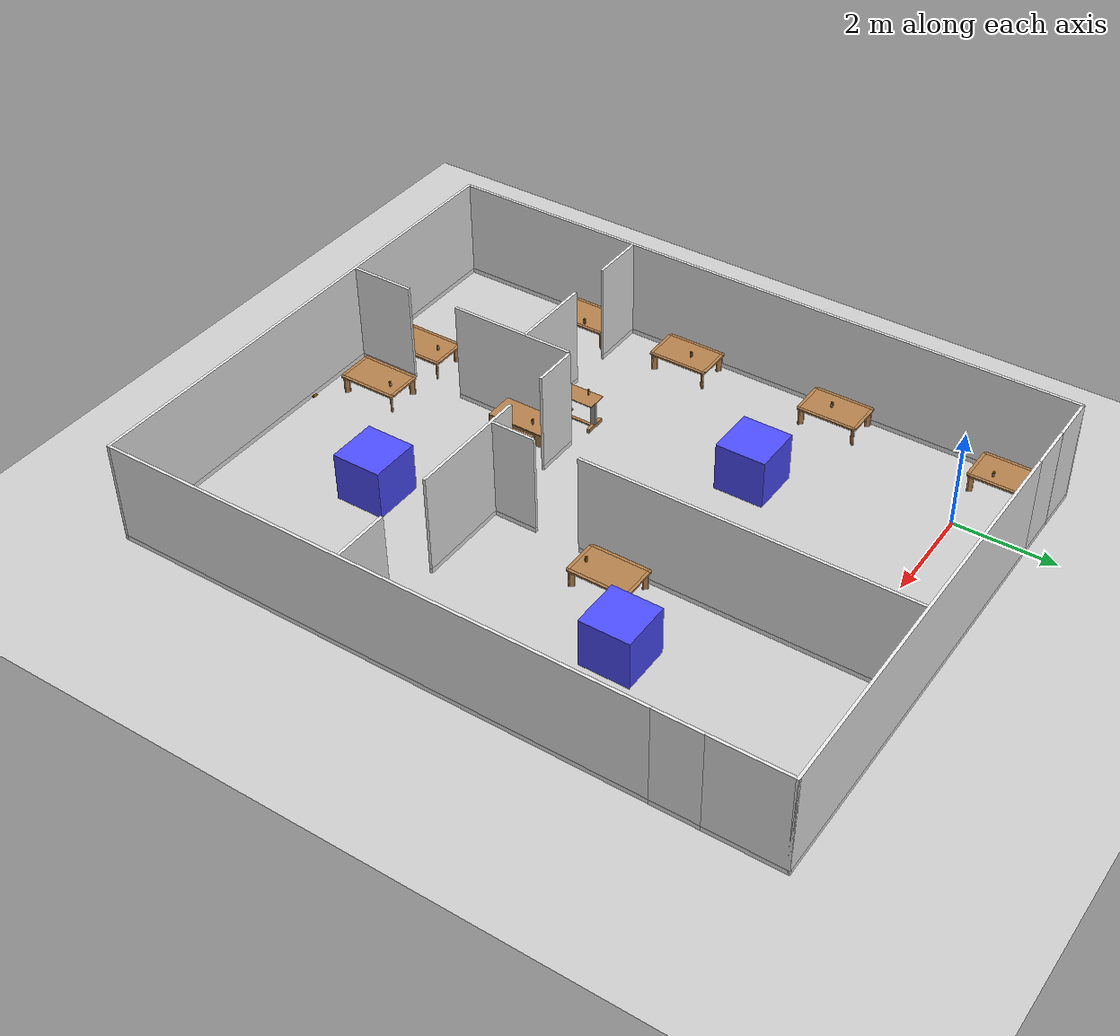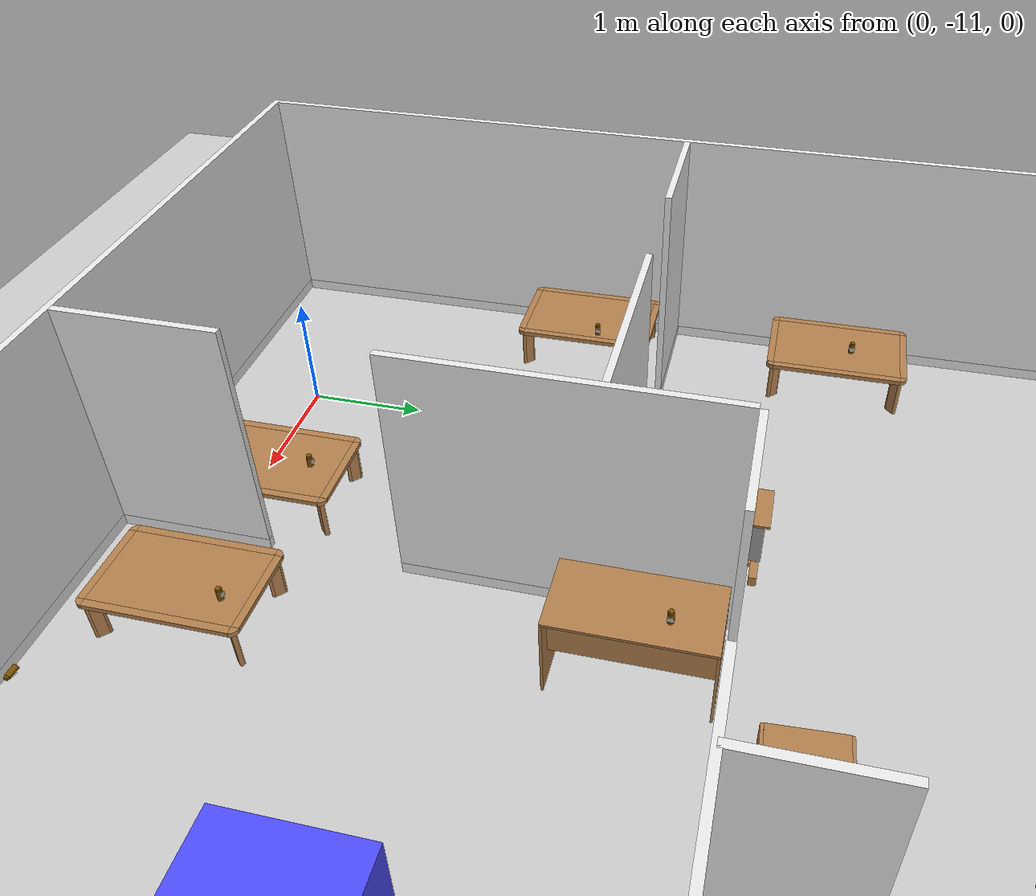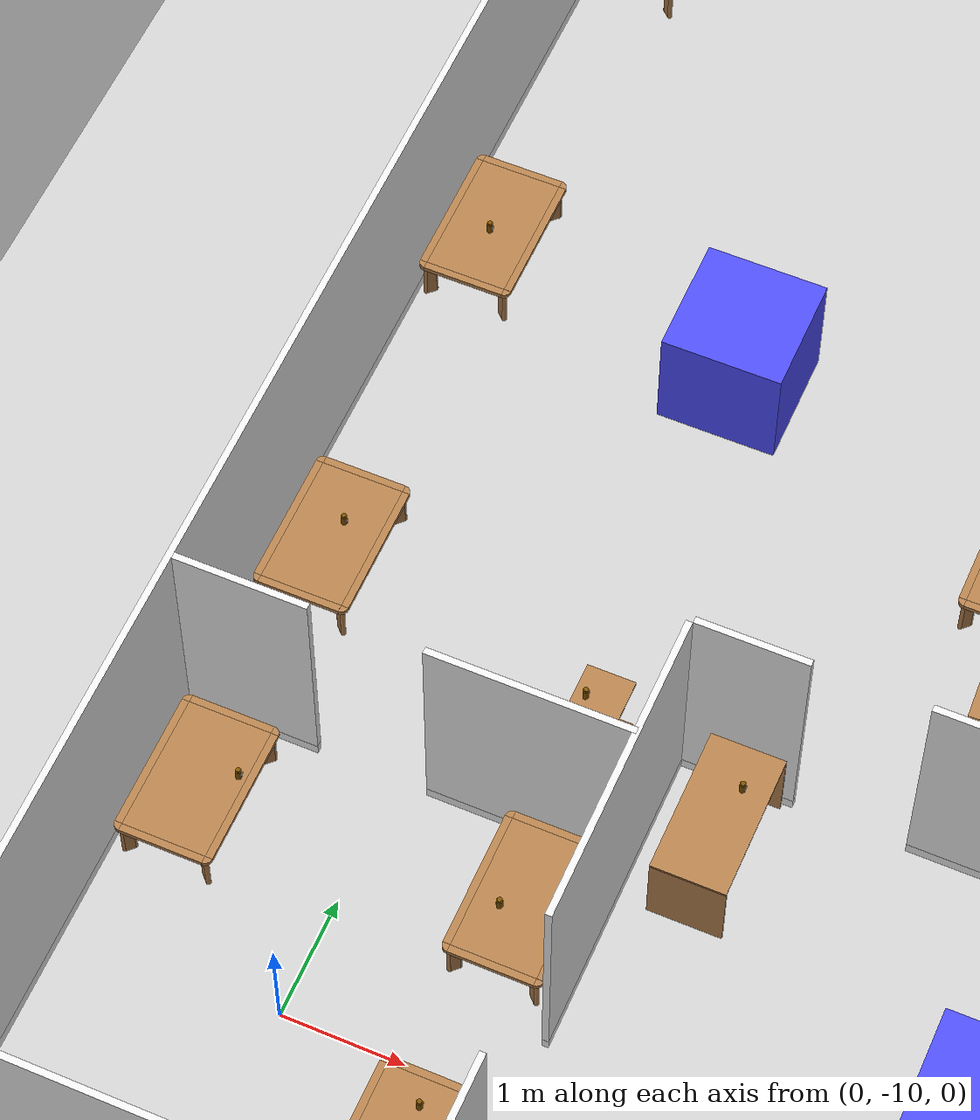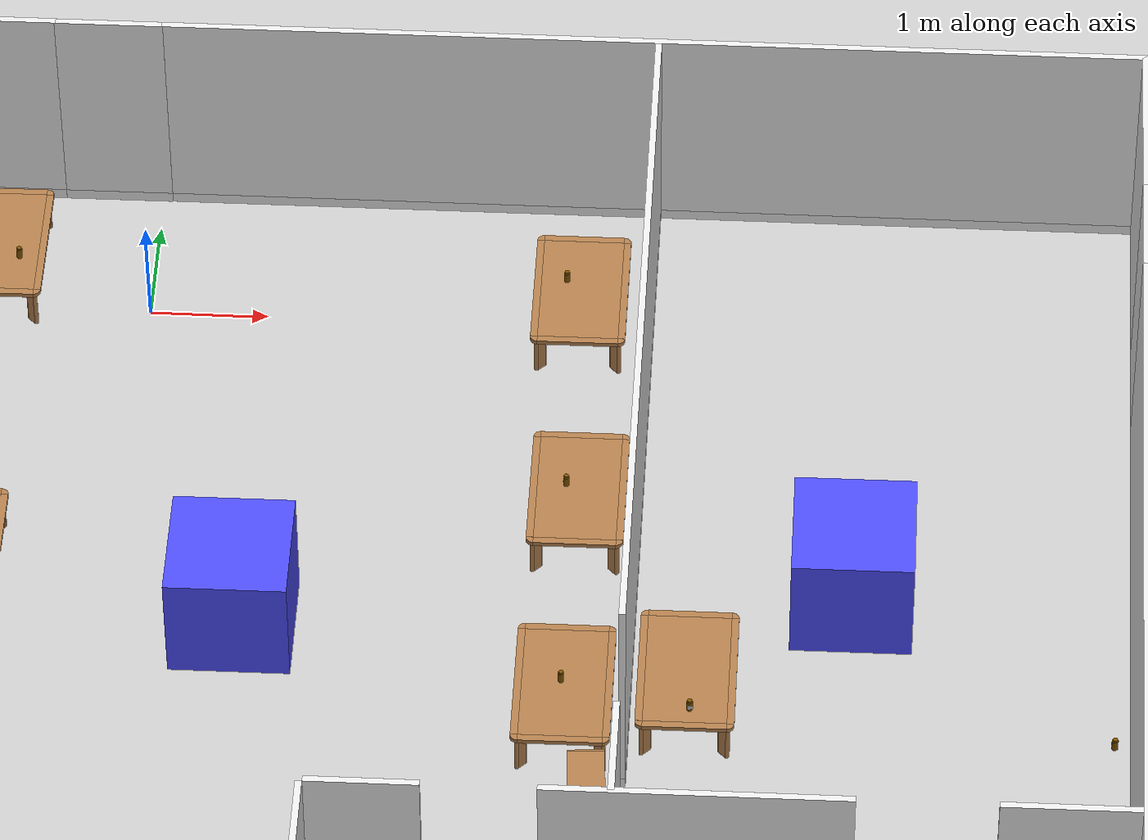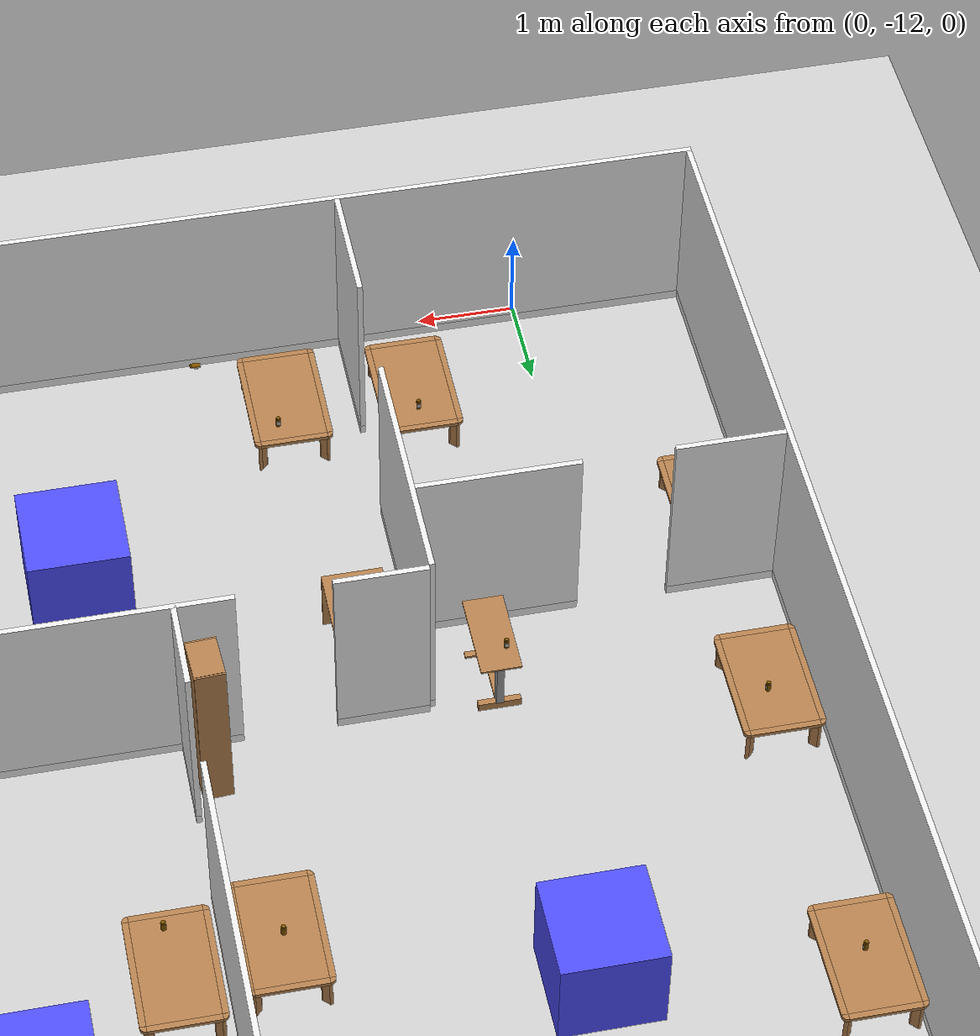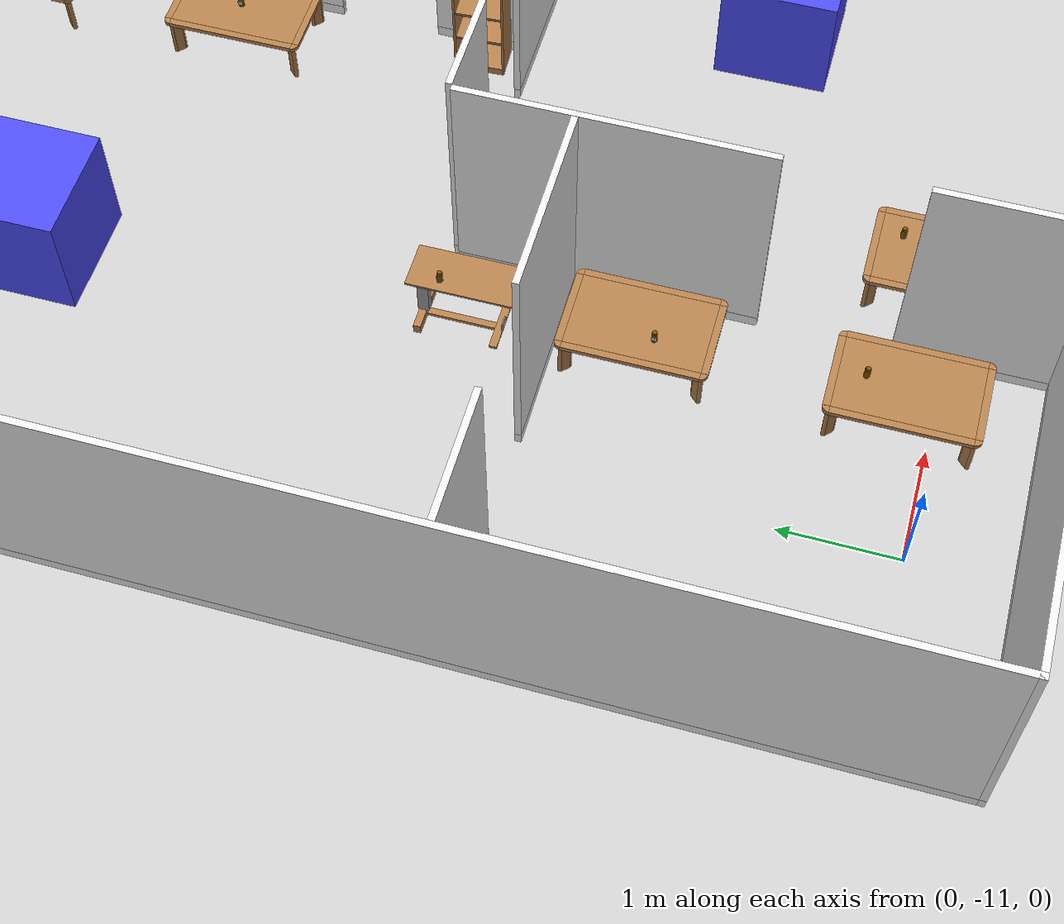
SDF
<sdf version="1.6">
 <world name="default">
  <light name="sun" type="directional">
   <pose>0 0 10 0 -0 0</pose>
   <diffuse>0.8 0.8 0.8 1</diffuse>
   <specular>0.1 0.1 0.1 1</specular>
   <attenuation>
    <range>1000</range>
    <constant>0.9</constant>
    <linear>0.01</linear>
    <quadratic>0.001</quadratic>
   </attenuation>
   <direction>-0.5 0.5 -1</direction>
  </light>
  <model name="ground_plane">
   <static>1</static>
   <link name="link">
    <collision name="collision">
     <geometry><plane><normal>0 0 1</normal><size>100 100</size></plane></geometry>
     <surface><friction><ode><mu>100</mu><mu2>50</mu2></ode></friction></surface>
    </collision>
    <visual name="visual">
     <cast_shadows>0</cast_shadows>
     <geometry><plane><normal>0 0 1</normal><size>100 100</size></plane></geometry>
     <material>
      <script><uri>file://media/materials/scripts/gazebo.material</uri><name>Gazebo/Grey</name></script>
     </material>
    </visual>
   </link>
  </model>
  <gravity>0 0 -9.8</gravity>
  <magnetic_field>6e-06 2.3e-05 -4.2e-05</magnetic_field>
  <atmosphere type="adiabatic"/>
  <physics name="default_physics" default="0" type="ode">
   <max_step_size>0.001</max_step_size>
   <real_time_factor>1</real_time_factor>
   <real_time_update_rate>1000</real_time_update_rate>
  </physics>
  <scene><ambient>0.4 0.4 0.4 1</ambient><background>0.7 0.7 0.7 1</background><shadows>1</shadows></scene>
  <spherical_coordinates>
   <surface_model>EARTH_WGS84</surface_model>
   <latitude_deg>0</latitude_deg>
   <longitude_deg>0</longitude_deg>
   <elevation>0</elevation>
   <heading_deg>0</heading_deg>
  </spherical_coordinates>
  <model name="full_outside_wall">
   <link name="link">
    <inertial>
     <mass>50</mass>
     <inertia><ixx>1</ixx><ixy>0</ixy><ixz>0</ixz><iyy>1</iyy><iyz>0</iyz><izz>1</izz></inertia>
    </inertial>
    <visual name="x00_13y00_bottom_frame">
     <pose>5.0375 -0.0275 0.05 0 -0 0</pose>
     <geometry><box><size>10.185 0.055 0.1</size></box></geometry>
     <material>
      <script><uri>model://base_materials/color/scripts</uri><name>hsr_color/white</name></script>
     </material>
    </visual>
    <collision name="x00_13y00_collision_bottom_frame">
     <pose>5.0375 -0.0275 0.05 0 -0 0</pose>
     <geometry><box><size>10.185 0.055 0.1</size></box></geometry>
    </collision>
    <visual name="wall_x00_13y00">
     <pose>5.0375 -0.0275 1.095 0 -0 0</pose>
     <geometry><box><size>10.185 0.055 1.99</size></box></geometry>
     <material>
      <script>
       <uri>model://base_materials/wall/scripts</uri>
       <uri>model://base_materials/wall/textures</uri>
       <name>wall/white_noise</name>
      </script>
     </material>
    </visual>
    <collision name="wall_x00_13y00">
     <pose>5.0375 -0.002 1.095 0 -0 0</pose>
     <geometry><box><size>10.08 0.055 1.99</size></box></geometry>
    </collision>
    <visual name="x00y00_15_bottom_frame">
     <pose>-0.0275 6.59 0.05 0 -0 0</pose>
     <geometry><box><size>0.055 13.29 0.1</size></box></geometry>
     <material>
      <script><uri>model://base_materials/color/scripts</uri><name>hsr_color/white</name></script>
     </material>
    </visual>
    <collision name="x00y00_15_collision_bottom_frame">
     <pose>-0.0275 6.59 0.05 0 -0 0</pose>
     <geometry><box><size>0.055 13.29 0.1</size></box></geometry>
    </collision>
    <visual name="wall_x00y00_15">
     <pose>-0.0275 6.59 1.095 0 -0 0</pose>
     <geometry><box><size>0.055 13.29 1.99</size></box></geometry>
     <material>
      <script>
       <uri>model://base_materials/wall/scripts</uri>
       <uri>model://base_materials/wall/textures</uri>
       <name>wall/white_noise</name>
      </script>
     </material>
    </visual>
    <collision name="wall_x00y00_x00y15">
     <pose>-0.002 6.59 1.095 0 -0 0</pose>
     <geometry><box><size>0.002 13.29 1.99</size></box></geometry>
    </collision>
    <visual name="x13y00_12_bottom_frame">
     <pose>10.1025 5.3725 0.05 0 -0 0</pose>
     <geometry><box><size>0.055 10.855 0.1</size></box></geometry>
     <material>
      <script><uri>model://base_materials/color/scripts</uri><name>hsr_color/white</name></script>
     </material>
    </visual>
    <collision name="x13y00_12_collision_bottom_frame">
     <pose>10.1025 5.3725 0.05 0 -0 0</pose>
     <geometry><box><size>0.055 10.855 0.1</size></box></geometry>
    </collision>
    <visual name="wall_x13y00_12">
     <pose>10.1025 5.3725 1.095 0 -0 0</pose>
     <geometry><box><size>0.055 10.855 1.99</size></box></geometry>
     <material>
      <script>
       <uri>model://base_materials/wall/scripts</uri>
       <uri>model://base_materials/wall/textures</uri>
       <name>wall/white_noise</name>
      </script>
     </material>
    </visual>
    <collision name="wall_x13y00_12">
     <pose>10.1025 5.3725 1.095 0 -0 0</pose>
     <geometry><box><size>0.055 10.855 1.99</size></box></geometry>
    </collision>
    <visual name="x13y14_16_bottom_frame">
     <pose>10.1025 12.4675 0.05 0 -0 0</pose>
     <geometry><box><size>0.055 1.535 0.1</size></box></geometry>
     <material>
      <script><uri>model://base_materials/color/scripts</uri><name>hsr_color/white</name></script>
     </material>
    </visual>
    <collision name="x13y14_16_collision_bottom_frame">
     <pose>10.1025 12.4675 0.05 0 -0 0</pose>
     <geometry><box><size>0.055 1.535 0.1</size></box></geometry>
    </collision>
    <visual name="wall_x13y14_x13y16">
     <pose>10.1025 12.4675 1.095 0 -0 0</pose>
     <geometry><box><size>0.055 1.535 1.99</size></box></geometry>
     <material>
      <script>
       <uri>model://base_materials/wall/scripts</uri>
       <uri>model://base_materials/wall/textures</uri>
       <name>wall/white_noise</name>
      </script>
     </material>
    </visual>
    <collision name="wall_x13y14_x13y16">
     <pose>10.1025 12.4675 1.095 0 -0 0</pose>
     <geometry><box><size>0.055 1.535 1.99</size></box></geometry>
    </collision>
    <visual name="x00_01y16_bottom_frame">
     <pose>0.4225 13.2075 0.05 0 -0 0</pose>
     <geometry><box><size>0.955 0.055 0.1</size></box></geometry>
     <material>
      <script><uri>model://base_materials/color/scripts</uri><name>hsr_color/white</name></script>
     </material>
    </visual>
    <collision name="x00_01y16_collision_bottom_frame">
     <pose>0.4225 13.2075 0.05 0 -0 0</pose>
     <geometry><box><size>0.955 0.055 0.1</size></box></geometry>
    </collision>
    <visual name="wall_x00_01y16">
     <pose>0.4225 13.2075 1.095 0 -0 0</pose>
     <geometry><box><size>0.955 0.055 1.99</size></box></geometry>
     <material>
      <script>
       <uri>model://base_materials/wall/scripts</uri>
       <uri>model://base_materials/wall/textures</uri>
       <name>wall/white_noise</name>
      </script>
     </material>
    </visual>
    <collision name="wall_x00_x01y16">
     <pose>0.4225 13.2075 1.095 0 -0 0</pose>
     <geometry><box><size>0.955 0.055 1.99</size></box></geometry>
    </collision>
    <visual name="x03_13y16_bottom_frame">
     <pose>5.965 13.2075 0.05 0 -0 0</pose>
     <geometry><box><size>8.33 0.05 0.1</size></box></geometry>
     <material>
      <script><uri>model://base_materials/color/scripts</uri><name>hsr_color/white</name></script>
     </material>
    </visual>
    <collision name="x03_13y16_collision_bottom_frame">
     <pose>5.965 13.2075 0.05 0 -0 0</pose>
     <geometry><box><size>8.33 0.05 0.1</size></box></geometry>
    </collision>
    <visual name="wall_x03_13y16">
     <pose>5.965 13.2075 1.095 0 -0 0</pose>
     <geometry><box><size>8.33 0.055 1.99</size></box></geometry>
     <material>
      <script>
       <uri>model://base_materials/wall/scripts</uri>
       <uri>model://base_materials/wall/textures</uri>
       <name>wall/white_noise</name>
      </script>
     </material>
    </visual>
    <collision name="wall_x03_13y16">
     <pose>5.965 13.2075 1.095 0 -0 0</pose>
     <geometry><box><size>8.33 0.055 1.99</size></box></geometry>
    </collision>
    <velocity_decay><linear>0</linear><angular>0</angular></velocity_decay>
   </link>
   <static>1</static>
   <pose>-1.74055 -11.8334 0 0 -0 0</pose>
  </model>
  <model name="full_inside_wall">
   <link name="link">
    <inertial>
     <mass>50</mass>
     <inertia><ixx>1</ixx><ixy>0</ixy><ixz>0</ixz><iyy>1</iyy><iyz>0</iyz><izz>1</izz></inertia>
    </inertial>
    <visual name="x05y01_08_bottom_frame">
     <pose>4.075 3.215 0.05 0 -0 0</pose>
     <geometry><box><size>0.055 6.43 0.1</size></box></geometry>
     <material>
      <script><uri>model://base_materials/color/scripts</uri><name>hsr_color/white</name></script>
     </material>
    </visual>
    <collision name="x05y01_08_collision_bottom_frame">
     <pose>4.075 3.215 0.05 0 -0 0</pose>
     <geometry><box><size>0.055 6.43 0.1</size></box></geometry>
    </collision>
    <visual name="x05y01_08_wall">
     <pose>4.075 3.215 1.095 0 -0 0</pose>
     <geometry><box><size>0.055 6.43 1.99</size></box></geometry>
     <material>
      <script>
       <uri>model://base_materials/wall/scripts</uri>
       <uri>model://base_materials/wall/textures</uri>
       <name>wall/white_noise</name>
      </script>
     </material>
    </visual>
    <collision name="x05y01_08_collision_wall">
     <pose>4.075 3.215 1.095 0 -0 0</pose>
     <geometry><box><size>0.055 6.43 1.99</size></box></geometry>
    </collision>
    <visual name="x05y10_bottom_frame">
     <pose>4.075 7.78 0.05 0 -0 0</pose>
     <geometry><box><size>0.055 0.9 0.1</size></box></geometry>
     <material>
      <script><uri>model://base_materials/color/scripts</uri><name>hsr_color/white</name></script>
     </material>
    </visual>
    <collision name="x05y10_collision_bottom_frame">
     <pose>4.075 7.78 0.05 0 -0 0</pose>
     <geometry><box><size>0.055 0.9 0.1</size></box></geometry>
    </collision>
    <visual name="x05y10_wall">
     <pose>4.075 7.78 1.095 0 -0 0</pose>
     <geometry><box><size>0.055 0.9 1.99</size></box></geometry>
     <material>
      <script>
       <uri>model://base_materials/wall/scripts</uri>
       <uri>model://base_materials/wall/textures</uri>
       <name>wall/white_noise</name>
      </script>
     </material>
    </visual>
    <collision name="x05y10_collision_wall">
     <pose>4.075 7.78 1.095 0 -0 0</pose>
     <geometry><box><size>0.055 0.9 1.99</size></box></geometry>
    </collision>
    <visual name="x01_02_y09_bottom_frame">
     <pose>0.55 8.23 0.05 0 -0 1.5708</pose>
     <geometry><box><size>0.055 1.1 0.1</size></box></geometry>
     <material>
      <script><uri>model://base_materials/color/scripts</uri><name>hsr_color/white</name></script>
     </material>
    </visual>
    <collision name="x01_02_y09_collision_bottom_frame">
     <pose>0.55 8.23 0.05 0 -0 1.5708</pose>
     <geometry><box><size>0.055 1.1 0.1</size></box></geometry>
    </collision>
    <visual name="x01_02_y09_wall">
     <pose>0.55 8.23 1.095 0 -0 1.5708</pose>
     <geometry><box><size>0.055 1.1 1.99</size></box></geometry>
     <material>
      <script>
       <uri>model://base_materials/wall/scripts</uri>
       <uri>model://base_materials/wall/textures</uri>
       <name>wall/white_noise</name>
      </script>
     </material>
    </visual>
    <collision name="x01_02_y09_collision_wall">
     <pose>0.55 8.23 1.095 0 -0 1.5708</pose>
     <geometry><box><size>0.055 1.1 1.99</size></box></geometry>
    </collision>
    <visual name="x04_07_y09_bottom_frame">
     <pose>3.42 8.23 0.05 0 -0 1.5708</pose>
     <geometry><box><size>0.055 2.44 0.1</size></box></geometry>
     <material>
      <script><uri>model://base_materials/color/scripts</uri><name>hsr_color/white</name></script>
     </material>
    </visual>
    <collision name="x04_07_y09_collision_bottom_frame">
     <pose>3.42 8.23 0.05 0 -0 1.5708</pose>
     <geometry><box><size>0.055 2.44 0.1</size></box></geometry>
    </collision>
    <visual name="x04_07_y09_wall">
     <pose>3.42 8.23 1.095 0 -0 1.5708</pose>
     <geometry><box><size>0.055 2.44 1.99</size></box></geometry>
     <material>
      <script>
       <uri>model://base_materials/wall/scripts</uri>
       <uri>model://base_materials/wall/textures</uri>
       <name>wall/white_noise</name>
      </script>
     </material>
    </visual>
    <collision name="x04_07_y09_collision_wall">
     <pose>3.42 8.23 1.095 0 -0 1.5708</pose>
     <geometry><box><size>0.055 2.44 1.99</size></box></geometry>
    </collision>
    <visual name="x08y10a_bottom_frame">
     <pose>5.9925 8.23 0.05 0 -0 1.5708</pose>
     <geometry><box><size>0.055 0.9 0.1</size></box></geometry>
     <material>
      <script><uri>model://base_materials/color/scripts</uri><name>hsr_color/white</name></script>
     </material>
    </visual>
    <collision name="x08y10a_collision_bottom_frame">
     <pose>5.9925 8.23 0.05 0 -0 1.5708</pose>
     <geometry><box><size>0.055 0.9 0.1</size></box></geometry>
    </collision>
    <visual name="x08y10a_wall">
     <pose>5.9925 8.23 1.095 0 -0 1.5708</pose>
     <geometry><box><size>0.055 0.9 1.99</size></box></geometry>
     <material>
      <script>
       <uri>model://base_materials/wall/scripts</uri>
       <uri>model://base_materials/wall/textures</uri>
       <name>wall/white_noise</name>
      </script>
     </material>
    </visual>
    <collision name="x08y10a_collision_wall">
     <pose>5.9925 8.23 1.095 0 -0 1.5708</pose>
     <geometry><box><size>0.055 0.9 1.99</size></box></geometry>
    </collision>
    <visual name="x08y10a_bottom_frame">
     <pose>5.9925 8.23 0.05 0 -0 1.5708</pose>
     <geometry><box><size>0.055 0.9 0.1</size></box></geometry>
     <material>
      <script><uri>model://base_materials/color/scripts</uri><name>hsr_color/white</name></script>
     </material>
    </visual>
    <collision name="x08y10a_collision_bottom_frame">
     <pose>5.9925 8.23 0.05 0 -0 1.5708</pose>
     <geometry><box><size>0.055 0.9 0.1</size></box></geometry>
    </collision>
    <visual name="x08y10a_wall">
     <pose>5.9925 8.23 1.095 0 -0 1.5708</pose>
     <geometry><box><size>0.055 0.9 1.99</size></box></geometry>
     <material>
      <script>
       <uri>model://base_materials/wall/scripts</uri>
       <uri>model://base_materials/wall/textures</uri>
       <name>wall/white_noise</name>
      </script>
     </material>
    </visual>
    <collision name="x08y10a_collision_wall">
     <pose>5.9925 8.23 1.095 0 -0 1.5708</pose>
     <geometry><box><size>0.055 0.9 1.99</size></box></geometry>
    </collision>
    <visual name="x08y14_15_bottom_frame">
     <pose>6.47 12.54 0.05 0 -0 0</pose>
     <geometry><box><size>0.055 1.28 0.1</size></box></geometry>
     <material>
      <script><uri>model://base_materials/color/scripts</uri><name>hsr_color/white</name></script>
     </material>
    </visual>
    <collision name="x08y14_15_collision_bottom_frame">
     <pose>6.47 12.54 0.05 0 -0 0</pose>
     <geometry><box><size>0.055 1.28 0.1</size></box></geometry>
    </collision>
    <visual name="x08y14_15_wall">
     <pose>6.47 12.54 1.095 0 -0 0</pose>
     <geometry><box><size>0.055 1.28 1.99</size></box></geometry>
     <material>
      <script>
       <uri>model://base_materials/wall/scripts</uri>
       <uri>model://base_materials/wall/textures</uri>
       <name>wall/white_noise</name>
      </script>
     </material>
    </visual>
    <collision name="x08y14_15_collision_wall">
     <pose>6.47 12.54 1.095 0 -0 0</pose>
     <geometry><box><size>0.055 1.28 1.99</size></box></geometry>
    </collision>
    <visual name="x08y10b_12_bottom_frame">
     <pose>6.47 9.52875 0.05 0 -0 0</pose>
     <geometry><box><size>0.055 2.5425 0.1</size></box></geometry>
     <material>
      <script><uri>model://base_materials/color/scripts</uri><name>hsr_color/white</name></script>
     </material>
    </visual>
    <collision name="x08y10b_12_collision_bottom_frame">
     <pose>6.47 9.52875 0.05 0 -0 0</pose>
     <geometry><box><size>0.055 2.5425 0.1</size></box></geometry>
    </collision>
    <visual name="x08y10b_12_wall">
     <pose>6.47 9.52875 1.095 0 -0 0</pose>
     <geometry><box><size>0.055 2.5425 1.99</size></box></geometry>
     <material>
      <script>
       <uri>model://base_materials/wall/scripts</uri>
       <uri>model://base_materials/wall/textures</uri>
       <name>wall/white_noise</name>
      </script>
     </material>
    </visual>
    <collision name="x08y10b_12_collision_wall">
     <pose>6.47 9.52875 1.095 0 -0 0</pose>
     <geometry><box><size>0.055 2.5425 1.99</size></box></geometry>
    </collision>
    <visual name="x08_09y11b_bottom_frame">
     <pose>7.284 9.23 0.05 0 -0 1.5708</pose>
     <geometry><box><size>0.055 1.632 0.1</size></box></geometry>
     <material>
      <script><uri>model://base_materials/color/scripts</uri><name>hsr_color/white</name></script>
     </material>
    </visual>
    <collision name="x08_09y11b_collision_bottom_frame">
     <pose>7.284 9.23 0.05 0 -0 1.5708</pose>
     <geometry><box><size>0.055 1.632 0.1</size></box></geometry>
    </collision>
    <visual name="x08_09y11b_wall">
     <pose>7.284 9.23 1.095 0 -0 1.5708</pose>
     <geometry><box><size>0.055 1.632 1.99</size></box></geometry>
     <material>
      <script>
       <uri>model://base_materials/wall/scripts</uri>
       <uri>model://base_materials/wall/textures</uri>
       <name>wall/white_noise</name>
      </script>
     </material>
    </visual>
    <collision name="x08_09y11b_collision_wall">
     <pose>7.284 9.23 1.095 0 -0 1.5708</pose>
     <geometry><box><size>0.055 1.632 1.99</size></box></geometry>
    </collision>
    <visual name="x11_12y11_bottom_frame">
     <pose>9.5375 9.23 0.05 0 -0 1.5708</pose>
     <geometry><box><size>0.055 1.075 0.1</size></box></geometry>
     <material>
      <script><uri>model://base_materials/color/scripts</uri><name>hsr_color/white</name></script>
     </material>
    </visual>
    <collision name="x11_12y11_collision_bottom_frame">
     <pose>9.5375 9.23 0.05 0 -0 1.5708</pose>
     <geometry><box><size>0.055 1.075 0.1</size></box></geometry>
    </collision>
    <visual name="x11_12y11_wall">
     <pose>9.5375 9.23 1.095 0 -0 1.5708</pose>
     <geometry><box><size>0.055 1.075 1.99</size></box></geometry>
     <material>
      <script>
       <uri>model://base_materials/wall/scripts</uri>
       <uri>model://base_materials/wall/textures</uri>
       <name>wall/white_noise</name>
      </script>
     </material>
    </visual>
    <collision name="x11_12y11_collision_wall">
     <pose>9.5375 9.23 1.095 0 -0 1.5708</pose>
     <geometry><box><size>0.055 1.075 1.99</size></box></geometry>
    </collision>
    <velocity_decay><linear>0</linear><angular>0</angular></velocity_decay>
   </link>
   <static>1</static>
   <pose>8.33769 1.33864 0 0 -0 3.14132</pose>
  </model>
  <model name="static_box_2">
   <link name="link">
    <inertial>
     <mass>100</mass>
     <inertia>
      <ixx>0.166667</ixx>
      <ixy>0</ixy>
      <ixz>0</ixz>
      <iyy>0.166667</iyy>
      <iyz>0</iyz>
      <izz>0.166667</izz>
     </inertia>
    </inertial>
    <visual name="visual">
     <geometry><box><size>1 1 1</size></box></geometry>
     <material>
      <script><name>Gazebo/Grey</name><uri>file://media/materials/scripts/gazebo.material</uri></script>
      <ambient>0.3 0.3 1 1</ambient>
      <diffuse>0.7 0.7 0.7 1</diffuse>
      <specular>0.01 0.01 0.01 1</specular>
      <emissive>0 0 0 1</emissive>
      <shader type="vertex"><normal_map>__default__</normal_map></shader>
     </material>
    </visual>
    <collision name="collision">
     <geometry><box><size>1 1 1</size></box></geometry>
     <surface>
      <friction>
       <ode><mu>1</mu><mu2>1</mu2><fdir1>0 0 0</fdir1><slip1>0</slip1><slip2>0</slip2></ode>
       <torsional>
        <coefficient>1</coefficient>
        <patch_radius>0</patch_radius>
        <surface_radius>0</surface_radius>
        <use_patch_radius>1</use_patch_radius>
        <ode><slip>0</slip></ode>
       </torsional>
      </friction>
      <bounce><restitution_coefficient>0</restitution_coefficient><threshold>1e+06</threshold></bounce>
      <contact>
       <collide_without_contact>0</collide_without_contact>
       <collide_without_contact_bitmask>1</collide_without_contact_bitmask>
       <collide_bitmask>1</collide_bitmask>
       <ode>
        <soft_cfm>0</soft_cfm>
        <soft_erp>0.2</soft_erp>
        <kp>1e+13</kp>
        <kd>1</kd>
        <max_vel>0.01</max_vel>
        <min_depth>0</min_depth>
       </ode>
       <bullet>
        <split_impulse>1</split_impulse>
        <split_impulse_penetration_threshold>-0.01</split_impulse_penetration_threshold>
        <soft_cfm>0</soft_cfm>
        <soft_erp>0.2</soft_erp>
        <kp>1e+13</kp>
        <kd>1</kd>
       </bullet>
      </contact>
     </surface>
    </collision>
   </link>
   <static>0</static>
   <pose>6.05367 -3.06141 0.499993 -0 -9e-06 0.001268</pose>
  </model>
  <model name="static_box_3">
   <link name="link">
    <inertial>
     <mass>100</mass>
     <inertia>
      <ixx>0.166667</ixx>
      <ixy>0</ixy>
      <ixz>0</ixz>
      <iyy>0.166667</iyy>
      <iyz>0</iyz>
      <izz>0.166667</izz>
     </inertia>
    </inertial>
    <visual name="visual">
     <geometry><box><size>1 1 1</size></box></geometry>
     <material>
      <script><name>Gazebo/Grey</name><uri>file://media/materials/scripts/gazebo.material</uri></script>
      <ambient>0.3 0.3 1 1</ambient>
      <diffuse>0.7 0.7 0.7 1</diffuse>
      <specular>0.01 0.01 0.01 1</specular>
      <emissive>0 0 0 1</emissive>
      <shader type="vertex"><normal_map>__default__</normal_map></shader>
     </material>
    </visual>
    <collision name="collision">
     <geometry><box><size>1 1 1</size></box></geometry>
     <surface>
      <friction>
       <ode><mu>1</mu><mu2>1</mu2><fdir1>0 0 0</fdir1><slip1>0</slip1><slip2>0</slip2></ode>
       <torsional>
        <coefficient>1</coefficient>
        <patch_radius>0</patch_radius>
        <surface_radius>0</surface_radius>
        <use_patch_radius>1</use_patch_radius>
        <ode><slip>0</slip></ode>
       </torsional>
      </friction>
      <bounce><restitution_coefficient>0</restitution_coefficient><threshold>1e+06</threshold></bounce>
      <contact>
       <collide_without_contact>0</collide_without_contact>
       <collide_without_contact_bitmask>1</collide_without_contact_bitmask>
       <collide_bitmask>1</collide_bitmask>
       <ode>
        <soft_cfm>0</soft_cfm>
        <soft_erp>0.2</soft_erp>
        <kp>1e+13</kp>
        <kd>1</kd>
        <max_vel>0.01</max_vel>
        <min_depth>0</min_depth>
       </ode>
       <bullet>
        <split_impulse>1</split_impulse>
        <split_impulse_penetration_threshold>-0.01</split_impulse_penetration_threshold>
        <soft_cfm>0</soft_cfm>
        <soft_erp>0.2</soft_erp>
        <kp>1e+13</kp>
        <kd>1</kd>
       </bullet>
      </contact>
     </surface>
    </collision>
   </link>
   <static>0</static>
   <pose>1.00471 -3.5172 0.499993 0 -1.2e-05 0.000648</pose>
  </model>
  <model name="static_box_4">
   <link name="link">
    <inertial>
     <mass>100</mass>
     <inertia>
      <ixx>0.166667</ixx>
      <ixy>0</ixy>
      <ixz>0</ixz>
      <iyy>0.166667</iyy>
      <iyz>0</iyz>
      <izz>0.166667</izz>
     </inertia>
    </inertial>
    <visual name="visual">
     <geometry><box><size>1 1 1</size></box></geometry>
     <material>
      <script><name>Gazebo/Grey</name><uri>file://media/materials/scripts/gazebo.material</uri></script>
      <ambient>0.3 0.3 1 1</ambient>
      <diffuse>0.7 0.7 0.7 1</diffuse>
      <specular>0.01 0.01 0.01 1</specular>
      <emissive>0 0 0 1</emissive>
      <shader type="vertex"><normal_map>__default__</normal_map></shader>
     </material>
    </visual>
    <collision name="collision">
     <geometry><box><size>1 1 1</size></box></geometry>
     <surface>
      <friction>
       <ode><mu>1</mu><mu2>1</mu2><fdir1>0 0 0</fdir1><slip1>0</slip1><slip2>0</slip2></ode>
       <torsional>
        <coefficient>1</coefficient>
        <patch_radius>0</patch_radius>
        <surface_radius>0</surface_radius>
        <use_patch_radius>1</use_patch_radius>
        <ode><slip>0</slip></ode>
       </torsional>
      </friction>
      <bounce><restitution_coefficient>0</restitution_coefficient><threshold>1e+06</threshold></bounce>
      <contact>
       <collide_without_contact>0</collide_without_contact>
       <collide_without_contact_bitmask>1</collide_without_contact_bitmask>
       <collide_bitmask>1</collide_bitmask>
       <ode>
        <soft_cfm>0</soft_cfm>
        <soft_erp>0.2</soft_erp>
        <kp>1e+13</kp>
        <kd>1</kd>
        <max_vel>0.01</max_vel>
        <min_depth>0</min_depth>
       </ode>
       <bullet>
        <split_impulse>1</split_impulse>
        <split_impulse_penetration_threshold>-0.01</split_impulse_penetration_threshold>
        <soft_cfm>0</soft_cfm>
        <soft_erp>0.2</soft_erp>
        <kp>1e+13</kp>
        <kd>1</kd>
       </bullet>
      </contact>
     </surface>
    </collision>
   </link>
   <static>0</static>
   <pose>4.98897 -8.9961 0.499994 -1e-05 -6e-06 0.000596</pose>
  </model>
  <model name="full_wall_55_920_2090">
   <link name="link">
    <inertial>
     <mass>50</mass>
     <inertia><ixx>1</ixx><ixy>0</ixy><ixz>0</ixz><iyy>1</iyy><iyz>0</iyz><izz>1</izz></inertia>
    </inertial>
    <visual name="bottom_frame">
     <pose>0 0 0.05 0 -0 0</pose>
     <geometry><box><size>0.055 0.92 0.1</size></box></geometry>
     <material>
      <script><uri>model://base_materials/color/scripts</uri><name>hsr_color/white</name></script>
     </material>
    </visual>
    <collision name="collision_bottom_frame">
     <pose>0 0 0.05 0 -0 0</pose>
     <geometry><box><size>0.055 0.92 0.1</size></box></geometry>
    </collision>
    <visual name="wall">
     <pose>0 0 1.095 0 -0 0</pose>
     <geometry><box><size>0.055 0.92 1.99</size></box></geometry>
     <material>
      <script>
       <uri>model://base_materials/wall/scripts</uri>
       <uri>model://base_materials/wall/textures</uri>
       <name>wall/white_noise</name>
      </script>
     </material>
    </visual>
    <collision name="collision_wall">
     <pose>0 0 1.095 0 -0 0</pose>
     <geometry><box><size>0.055 0.92 1.99</size></box></geometry>
    </collision>
    <velocity_decay><linear>0</linear><angular>0</angular></velocity_decay>
   </link>
   <static>1</static>
   <pose>8.36232 -0.582065 0 0 -0 0</pose>
  </model>
  <model name="full_wall_55_920_2090_0">
   <link name="link">
    <inertial>
     <mass>50</mass>
     <inertia><ixx>1</ixx><ixy>0</ixy><ixz>0</ixz><iyy>1</iyy><iyz>0</iyz><izz>1</izz></inertia>
    </inertial>
    <visual name="bottom_frame">
     <pose>0 0 0.05 0 -0 0</pose>
     <geometry><box><size>0.055 0.92 0.1</size></box></geometry>
     <material>
      <script><uri>model://base_materials/color/scripts</uri><name>hsr_color/white</name></script>
     </material>
    </visual>
    <collision name="collision_bottom_frame">
     <pose>0 0 0.05 0 -0 0</pose>
     <geometry><box><size>0.055 0.92 0.1</size></box></geometry>
    </collision>
    <visual name="wall">
     <pose>0 0 1.095 0 -0 0</pose>
     <geometry><box><size>0.055 0.92 1.99</size></box></geometry>
     <material>
      <script>
       <uri>model://base_materials/wall/scripts</uri>
       <uri>model://base_materials/wall/textures</uri>
       <name>wall/white_noise</name>
      </script>
     </material>
    </visual>
    <collision name="collision_wall">
     <pose>0 0 1.095 0 -0 0</pose>
     <geometry><box><size>0.055 0.92 1.99</size></box></geometry>
    </collision>
    <velocity_decay><linear>0</linear><angular>0</angular></velocity_decay>
   </link>
   <static>1</static>
   <pose>-0.391738 1.37269 0 0 -0 1.5726</pose>
  </model>
  <model name="bottle">
   <link name="link">
    <inertial>
     <mass>0.05</mass>
     <inertia><ixx>0.00058</ixx><ixy>0</ixy><ixz>0</ixz><iyy>0.00058</iyy><iyz>0</iyz><izz>0.00016</izz></inertia>
    </inertial>
    <visual name="top">
     <pose>0 0 0.0555 0 -0 0</pose>
     <geometry><cylinder><radius>0.019</radius><length>0.016</length></cylinder></geometry>
     <material>
      <ambient>1 0.647 0 1</ambient>
      <diffuse>0.5 0.3235 0 1</diffuse>
      <specular>0.1 0.1 0.1 1</specular>
      <emissive>0 0 0 0</emissive>
     </material>
    </visual>
    <collision name="collision_top">
     <pose>0 0 0.0555 0 -0 0</pose>
     <geometry><cylinder><radius>0.019</radius><length>0.016</length></cylinder></geometry>
     <surface>
      <bounce><restitution_coefficient>0.2</restitution_coefficient><threshold>0</threshold></bounce>
      <contact><ode><kp>10000</kp><max_vel>10</max_vel></ode></contact>
     </surface>
    </collision>
    <visual name="bottom">
     <geometry><cylinder><radius>0.0245</radius><length>0.095</length></cylinder></geometry>
     <material>
      <ambient>1 0.7 0.3 1</ambient>
      <diffuse>0.5 0.3235 0 1</diffuse>
      <specular>0.1 0.1 0.1 1</specular>
      <emissive>0 0 0 0</emissive>
     </material>
    </visual>
    <collision name="collision_bottom">
     <geometry><cylinder><radius>0.0245</radius><length>0.095</length></cylinder></geometry>
     <surface>
      <bounce><restitution_coefficient>0.2</restitution_coefficient><threshold>0</threshold></bounce>
      <contact><ode><kp>100000</kp><max_vel>10</max_vel></ode></contact>
     </surface>
    </collision>
    <velocity_decay><linear>0</linear><angular>0</angular></velocity_decay>
    <visual name="marker_4000">
     <pose>0.0245 0 0 0 1.57 3.141</pose>
     <geometry><box><size>0.045 0.045 0.0001</size></box></geometry>
     <material>
      <script>
       <uri>model://marker/4000/scripts</uri>
       <uri>model://marker/4000/textures</uri>
       <name>Marker/4000</name>
      </script>
     </material>
    </visual>
   </link>
   <static>0</static>
   <pose>1.13095 -6.99592 0.6825 3e-06 -1e-05 1.48442</pose>
  </model>
  <model name="bed_table">
   <link name="link">
    <inertial>
     <pose>0 0.449 0.001 0 -0 0</pose>
     <mass>10</mass>
     <inertia><ixx>1</ixx><ixy>0</ixy><ixz>0</ixz><iyy>1</iyy><iyz>0</iyz><izz>1</izz></inertia>
    </inertial>
    <visual name="top_board">
     <pose>0 0.449 0.625 0 -0 0</pose>
     <geometry><box><size>0.398 0.898 0.02</size></box></geometry>
     <material>
      <script><uri>model://base_materials/wood/scripts/wood.material</uri><name>base_materials/wood</name></script>
     </material>
    </visual>
    <collision name="collision_top_board">
     <pose>0 0.449 0.625 0 -0 0</pose>
     <geometry><box><size>0.398 0.898 0.02</size></box></geometry>
    </collision>
    <visual name="right_pole">
     <pose>0 0.817 0.3515 0 -0 0</pose>
     <geometry><box><size>0.072 0.094 0.527</size></box></geometry>
     <material>
      <script><uri>model://base_materials/color/scripts</uri><name>hsr_color/grey</name></script>
     </material>
    </visual>
    <collision name="collision_right_pole">
     <pose>0 0.817 0.3515 0 -0 0</pose>
     <geometry><box><size>0.072 0.094 0.527</size></box></geometry>
    </collision>
    <visual name="right_bottom_pole">
     <pose>0 0.8225 0.044 0 -0 0</pose>
     <geometry><box><size>0.42 0.063 0.088</size></box></geometry>
     <material>
      <script><uri>model://base_materials/wood/scripts/wood.material</uri><name>base_materials/wood</name></script>
     </material>
    </visual>
    <collision name="collision_right_bottom_pole">
     <pose>0 0.8225 0.044 0 -0 0</pose>
     <geometry><box><size>0.42 0.063 0.088</size></box></geometry>
    </collision>
    <visual name="bottom_center_pole">
     <pose>0 0.502 0.03 0 -0 0</pose>
     <geometry><box><size>0.06 0.578 0.03</size></box></geometry>
     <material>
      <script><uri>model://base_materials/wood/scripts/wood.material</uri><name>base_materials/wood</name></script>
     </material>
    </visual>
    <collision name="collision_bottom_center_pole">
     <pose>0 0.502 0.03 0 -0 0</pose>
     <geometry><box><size>0.06 0.578 0.03</size></box></geometry>
    </collision>
    <visual name="left_bottom_pole">
     <pose>0 0.18 0.0325 0 -0 0</pose>
     <geometry><box><size>0.418 0.066 0.025</size></box></geometry>
     <material>
      <script><uri>model://base_materials/wood/scripts/wood.material</uri><name>base_materials/wood</name></script>
     </material>
    </visual>
    <collision name="collision_left_bottom_pole">
     <pose>0 0.18 0.0325 0 -0 0</pose>
     <geometry><box><size>0.418 0.066 0.025</size></box></geometry>
    </collision>
    <visual name="marker_0010">
     <pose>0 0.14 0.093 0 -0 0</pose>
     <geometry><box><size>0.09 0.001 0.09</size></box></geometry>
     <material>
      <script>
       <uri>model://bed_table/marker/0010/scripts</uri>
       <uri>model://bed_table/marker/0010/textures</uri>
       <name>Marker/0010</name>
      </script>
     </material>
    </visual>
    <collision name="collision_marker_0010">
     <pose>0 0.14 0.093 0 -0 0</pose>
     <geometry><box><size>0.09 0.001 0.09</size></box></geometry>
    </collision>
    <visual name="marker_0010_back_plate">
     <pose>0 0.146 0.093 0 -0 0</pose>
     <geometry><box><size>0.09 0.01 0.09</size></box></geometry>
     <material>
      <script><uri>model://base_materials/wood/scripts/wood.material</uri><name>base_materials/wood</name></script>
     </material>
    </visual>
    <collision name="collision_marker_0010_back_plate">
     <pose>0 0.146 0.093 0 -0 0</pose>
     <geometry><box><size>0.09 0.01 0.09</size></box></geometry>
    </collision>
    <velocity_decay><linear>0</linear><angular>0</angular></velocity_decay>
   </link>
   <static>1</static>
   <pose>1.23263 -7.6297 0 0 -0 0</pose>
  </model>
  <model name="high_shelf">
   <link name="link">
    <inertial>
     <mass>5</mass>
     <inertia><ixx>1</ixx><ixy>0</ixy><ixz>0</ixz><iyy>1</iyy><iyz>0</iyz><izz>1</izz></inertia>
    </inertial>
    <visual name="left_board">
     <pose>-0.1475 0.009 0.898 0 -0 0</pose>
     <geometry><box><size>0.295 0.018 1.796</size></box></geometry>
     <material>
      <script>
       <uri>model://base_materials/wood/scripts</uri>
       <uri>model://base_materials/wood/textures</uri>
       <name>base_materials/light_wood</name>
      </script>
     </material>
    </visual>
    <collision name="collision_left_board">
     <pose>-0.1475 0.009 0.898 0 -0 0</pose>
     <geometry><box><size>0.295 0.018 1.796</size></box></geometry>
    </collision>
    <visual name="right_board">
     <pose>-0.1475 0.441 0.898 0 -0 0</pose>
     <geometry><box><size>0.295 0.018 1.796</size></box></geometry>
     <material>
      <script>
       <uri>model://base_materials/wood/scripts</uri>
       <uri>model://base_materials/wood/textures</uri>
       <name>base_materials/light_wood</name>
      </script>
     </material>
    </visual>
    <collision name="collision_right_board">
     <pose>-0.1475 0.441 0.898 0 -0 0</pose>
     <geometry><box><size>0.295 0.018 1.796</size></box></geometry>
    </collision>
    <visual name="top_board">
     <pose>-0.1475 0.225 1.7825 0 -0 0</pose>
     <geometry><box><size>0.295 0.414 0.035</size></box></geometry>
     <material>
      <script>
       <uri>model://base_materials/wood/scripts</uri>
       <uri>model://base_materials/wood/textures</uri>
       <name>base_materials/light_wood</name>
      </script>
     </material>
    </visual>
    <collision name="collision_top_board">
     <pose>-0.1475 0.225 1.7825 0 -0 0</pose>
     <geometry><box><size>0.295 0.414 0.035</size></box></geometry>
    </collision>
    <visual name="1st_shelf">
     <pose>-0.162 0.225 1.51 0 -0 0</pose>
     <geometry><box><size>0.266 0.414 0.018</size></box></geometry>
     <material>
      <script>
       <uri>model://base_materials/wood/scripts</uri>
       <uri>model://base_materials/wood/textures</uri>
       <name>base_materials/light_wood</name>
      </script>
     </material>
    </visual>
    <collision name="collision_1st_shelf">
     <pose>-0.162 0.225 1.51 0 -0 0</pose>
     <geometry><box><size>0.266 0.414 0.018</size></box></geometry>
    </collision>
    <visual name="2nd_shelf">
     <pose>-0.162 0.225 1.22 0 -0 0</pose>
     <geometry><box><size>0.266 0.414 0.018</size></box></geometry>
     <material>
      <script>
       <uri>model://base_materials/wood/scripts</uri>
       <uri>model://base_materials/wood/textures</uri>
       <name>base_materials/light_wood</name>
      </script>
     </material>
    </visual>
    <collision name="collision_2nd_shelf">
     <pose>-0.162 0.225 1.22 0 -0 0</pose>
     <geometry><box><size>0.266 0.414 0.018</size></box></geometry>
    </collision>
    <visual name="3rd_shelf">
     <pose>-0.162 0.225 0.93 0 -0 0</pose>
     <geometry><box><size>0.266 0.414 0.018</size></box></geometry>
     <material>
      <script>
       <uri>model://base_materials/wood/scripts</uri>
       <uri>model://base_materials/wood/textures</uri>
       <name>base_materials/light_wood</name>
      </script>
     </material>
    </visual>
    <collision name="collision_3rd_shelf">
     <pose>-0.162 0.225 0.93 0 -0 0</pose>
     <geometry><box><size>0.266 0.414 0.018</size></box></geometry>
    </collision>
    <visual name="4th_shelf">
     <pose>-0.162 0.225 0.65 0 -0 0</pose>
     <geometry><box><size>0.266 0.414 0.018</size></box></geometry>
     <material>
      <script>
       <uri>model://base_materials/wood/scripts</uri>
       <uri>model://base_materials/wood/textures</uri>
       <name>base_materials/light_wood</name>
      </script>
     </material>
    </visual>
    <collision name="collision_4th_shelf">
     <pose>-0.162 0.225 0.65 0 -0 0</pose>
     <geometry><box><size>0.266 0.414 0.018</size></box></geometry>
    </collision>
    <visual name="5th_shelf">
     <pose>-0.162 0.225 0.36 0 -0 0</pose>
     <geometry><box><size>0.266 0.414 0.018</size></box></geometry>
     <material>
      <script>
       <uri>model://base_materials/wood/scripts</uri>
       <uri>model://base_materials/wood/textures</uri>
       <name>base_materials/light_wood</name>
      </script>
     </material>
    </visual>
    <collision name="collision_5th_shelf">
     <pose>-0.162 0.225 0.36 0 -0 0</pose>
     <geometry><box><size>0.266 0.414 0.018</size></box></geometry>
    </collision>
    <visual name="bottom_board">
     <pose>-0.1475 0.225 0.035 0 -0 0</pose>
     <geometry><box><size>0.295 0.414 0.07</size></box></geometry>
     <material>
      <script>
       <uri>model://base_materials/wood/scripts</uri>
       <uri>model://base_materials/wood/textures</uri>
       <name>base_materials/light_wood</name>
      </script>
     </material>
    </visual>
    <collision name="collision_bottom_board">
     <pose>-0.1475 0.225 0.035 0 -0 0</pose>
     <geometry><box><size>0.295 0.414 0.07</size></box></geometry>
    </collision>
    <visual name="back_board">
     <pose>-0.286 0.225 0.898 0 -0 0</pose>
     <geometry><box><size>0.018 0.414 1.796</size></box></geometry>
     <material>
      <script>
       <uri>model://base_materials/wood/scripts</uri>
       <uri>model://base_materials/wood/textures</uri>
       <name>base_materials/light_wood</name>
      </script>
     </material>
    </visual>
    <collision name="collision_back_board">
     <pose>-0.286 0.225 0.898 0 -0 0</pose>
     <geometry><box><size>0.018 0.414 1.796</size></box></geometry>
    </collision>
    <velocity_decay><linear>0</linear><angular>0</angular></velocity_decay>
   </link>
   <static>1</static>
   <pose>3.88802 -6.25445 0 0 0 -3.08817</pose>
  </model>
  <model name="office_desk">
   <link name="link">
    <inertial>
     <mass>10</mass>
     <inertia><ixx>1</ixx><ixy>0</ixy><ixz>0</ixz><iyy>1</iyy><iyz>0</iyz><izz>1</izz></inertia>
    </inertial>
    <visual name="top_board">
     <pose>-0.3 0.6 0.69 0 -0 0</pose>
     <geometry><box><size>0.6 1.2 0.02</size></box></geometry>
     <material>
      <script>
       <uri>model://base_materials/wood/scripts/wood.material</uri>
       <name>base_materials/dark_wood</name>
      </script>
     </material>
    </visual>
    <collision name="collision_top_board">
     <pose>-0.3 0.6 0.69 0 -0 0</pose>
     <geometry><box><size>0.6 1.2 0.02</size></box></geometry>
    </collision>
    <visual name="left_board">
     <pose>-0.3 0.01 0.34 0 -0 0</pose>
     <geometry><box><size>0.6 0.02 0.68</size></box></geometry>
     <material>
      <script>
       <uri>model://base_materials/wood/scripts/wood.material</uri>
       <name>base_materials/dark_wood</name>
      </script>
     </material>
    </visual>
    <collision name="collision_left_board">
     <pose>-0.3 0.01 0.34 0 -0 0</pose>
     <geometry><box><size>0.6 0.02 0.68</size></box></geometry>
    </collision>
    <visual name="right_board">
     <pose>-0.3 1.19 0.34 0 -0 0</pose>
     <geometry><box><size>0.6 0.02 0.68</size></box></geometry>
     <material>
      <script>
       <uri>model://base_materials/wood/scripts/wood.material</uri>
       <name>base_materials/dark_wood</name>
      </script>
     </material>
    </visual>
    <collision name="collision_right_board">
     <pose>-0.3 1.19 0.34 0 -0 0</pose>
     <geometry><box><size>0.6 0.02 0.68</size></box></geometry>
    </collision>
    <visual name="center_board">
     <pose>-0.14 0.6 0.49 0 -0 0</pose>
     <geometry><box><size>0.02 1.16 0.4</size></box></geometry>
     <material>
      <script>
       <uri>model://base_materials/wood/scripts/wood.material</uri>
       <name>base_materials/dark_wood</name>
      </script>
     </material>
    </visual>
    <collision name="ollision_center_board">
     <pose>-0.14 0.6 0.49 0 -0 0</pose>
     <geometry><box><size>0.02 1.16 0.4</size></box></geometry>
    </collision>
    <velocity_decay><linear>0</linear><angular>0</angular></velocity_decay>
   </link>
   <static>1</static>
   <pose>2.71315 -8.14411 0 0 -0 0</pose>
  </model>
  <model name="bottle_clone">
   <link name="link">
    <inertial>
     <mass>0.05</mass>
     <inertia><ixx>0.00058</ixx><ixy>0</ixy><ixz>0</ixz><iyy>0.00058</iyy><iyz>0</iyz><izz>0.00016</izz></inertia>
    </inertial>
    <visual name="top">
     <pose>0 0 0.0555 0 -0 0</pose>
     <geometry><cylinder><radius>0.019</radius><length>0.016</length></cylinder></geometry>
     <material>
      <ambient>1 0.647 0 1</ambient>
      <diffuse>0.5 0.3235 0 1</diffuse>
      <specular>0.1 0.1 0.1 1</specular>
      <emissive>0 0 0 0</emissive>
     </material>
    </visual>
    <collision name="collision_top">
     <pose>0 0 0.0555 0 -0 0</pose>
     <geometry><cylinder><radius>0.019</radius><length>0.016</length></cylinder></geometry>
     <surface>
      <bounce><restitution_coefficient>0.2</restitution_coefficient><threshold>0</threshold></bounce>
      <contact><ode><kp>10000</kp><max_vel>10</max_vel></ode></contact>
     </surface>
    </collision>
    <visual name="bottom">
     <geometry><cylinder><radius>0.0245</radius><length>0.095</length></cylinder></geometry>
     <material>
      <ambient>1 0.7 0.3 1</ambient>
      <diffuse>0.5 0.3235 0 1</diffuse>
      <specular>0.1 0.1 0.1 1</specular>
      <emissive>0 0 0 0</emissive>
     </material>
    </visual>
    <collision name="collision_bottom">
     <geometry><cylinder><radius>0.0245</radius><length>0.095</length></cylinder></geometry>
     <surface>
      <bounce><restitution_coefficient>0.2</restitution_coefficient><threshold>0</threshold></bounce>
      <contact><ode><kp>100000</kp><max_vel>10</max_vel></ode></contact>
     </surface>
    </collision>
    <velocity_decay><linear>0</linear><angular>0</angular></velocity_decay>
    <visual name="marker_4000">
     <pose>0.0245 0 0 0 1.57 3.141</pose>
     <geometry><box><size>0.045 0.045 0.0001</size></box></geometry>
     <material>
      <script>
       <uri>model://marker/4000/scripts</uri>
       <uri>model://marker/4000/textures</uri>
       <name>Marker/4000</name>
      </script>
     </material>
    </visual>
   </link>
   <static>0</static>
   <pose>8.16129 -5.39414 1.0975 -1e-06 -8e-06 -3.072</pose>
  </model>
  <model name="bottle_clone_0">
   <link name="link">
    <inertial>
     <mass>0.05</mass>
     <inertia><ixx>0.00058</ixx><ixy>0</ixy><ixz>0</ixz><iyy>0.00058</iyy><iyz>0</iyz><izz>0.00016</izz></inertia>
    </inertial>
    <visual name="top">
     <pose>0 0 0.0555 0 -0 0</pose>
     <geometry><cylinder><radius>0.019</radius><length>0.016</length></cylinder></geometry>
     <material>
      <ambient>1 0.647 0 1</ambient>
      <diffuse>0.5 0.3235 0 1</diffuse>
      <specular>0.1 0.1 0.1 1</specular>
      <emissive>0 0 0 0</emissive>
     </material>
    </visual>
    <collision name="collision_top">
     <pose>0 0 0.0555 0 -0 0</pose>
     <geometry><cylinder><radius>0.019</radius><length>0.016</length></cylinder></geometry>
     <surface>
      <bounce><restitution_coefficient>0.2</restitution_coefficient><threshold>0</threshold></bounce>
      <contact><ode><kp>10000</kp><max_vel>10</max_vel></ode></contact>
     </surface>
    </collision>
    <visual name="bottom">
     <geometry><cylinder><radius>0.0245</radius><length>0.095</length></cylinder></geometry>
     <material>
      <ambient>1 0.7 0.3 1</ambient>
      <diffuse>0.5 0.3235 0 1</diffuse>
      <specular>0.1 0.1 0.1 1</specular>
      <emissive>0 0 0 0</emissive>
     </material>
    </visual>
    <collision name="collision_bottom">
     <geometry><cylinder><radius>0.0245</radius><length>0.095</length></cylinder></geometry>
     <surface>
      <bounce><restitution_coefficient>0.2</restitution_coefficient><threshold>0</threshold></bounce>
      <contact><ode><kp>100000</kp><max_vel>10</max_vel></ode></contact>
     </surface>
    </collision>
    <velocity_decay><linear>0</linear><angular>0</angular></velocity_decay>
    <visual name="marker_4000">
     <pose>0.0245 0 0 0 1.57 3.141</pose>
     <geometry><box><size>0.045 0.045 0.0001</size></box></geometry>
     <material>
      <script>
       <uri>model://marker/4000/scripts</uri>
       <uri>model://marker/4000/textures</uri>
       <name>Marker/4000</name>
      </script>
     </material>
    </visual>
   </link>
   <static>0</static>
   <pose>2.50267 -7.30037 0.7475 6e-06 -7e-06 0.007734</pose>
  </model>
  <model name="bottle_clone_1">
   <link name="link">
    <inertial>
     <mass>0.05</mass>
     <inertia><ixx>0.00058</ixx><ixy>0</ixy><ixz>0</ixz><iyy>0.00058</iyy><iyz>0</iyz><izz>0.00016</izz></inertia>
    </inertial>
    <visual name="top">
     <pose>0 0 0.0555 0 -0 0</pose>
     <geometry><cylinder><radius>0.019</radius><length>0.016</length></cylinder></geometry>
     <material>
      <ambient>1 0.647 0 1</ambient>
      <diffuse>0.5 0.3235 0 1</diffuse>
      <specular>0.1 0.1 0.1 1</specular>
      <emissive>0 0 0 0</emissive>
     </material>
    </visual>
    <collision name="collision_top">
     <pose>0 0 0.0555 0 -0 0</pose>
     <geometry><cylinder><radius>0.019</radius><length>0.016</length></cylinder></geometry>
     <surface>
      <bounce><restitution_coefficient>0.2</restitution_coefficient><threshold>0</threshold></bounce>
      <contact><ode><kp>10000</kp><max_vel>10</max_vel></ode></contact>
     </surface>
    </collision>
    <visual name="bottom">
     <geometry><cylinder><radius>0.0245</radius><length>0.095</length></cylinder></geometry>
     <material>
      <ambient>1 0.7 0.3 1</ambient>
      <diffuse>0.5 0.3235 0 1</diffuse>
      <specular>0.1 0.1 0.1 1</specular>
      <emissive>0 0 0 0</emissive>
     </material>
    </visual>
    <collision name="collision_bottom">
     <geometry><cylinder><radius>0.0245</radius><length>0.095</length></cylinder></geometry>
     <surface>
      <bounce><restitution_coefficient>0.2</restitution_coefficient><threshold>0</threshold></bounce>
      <contact><ode><kp>100000</kp><max_vel>10</max_vel></ode></contact>
     </surface>
    </collision>
    <velocity_decay><linear>0</linear><angular>0</angular></velocity_decay>
    <visual name="marker_4000">
     <pose>0.0245 0 0 0 1.57 3.141</pose>
     <geometry><box><size>0.045 0.045 0.0001</size></box></geometry>
     <material>
      <script>
       <uri>model://marker/4000/scripts</uri>
       <uri>model://marker/4000/textures</uri>
       <name>Marker/4000</name>
      </script>
     </material>
    </visual>
   </link>
   <static>0</static>
   <pose>3.40355 -11.8063 0.024498 1.5708 1.51038 1.52608</pose>
  </model>
  <model name="kitchen_lowtable">
   <link name="link">
    <inertial>
     <mass>10</mass>
     <inertia><ixx>1</ixx><ixy>0</ixy><ixz>0</ixz><iyy>1</iyy><iyz>0</iyz><izz>1</izz></inertia>
    </inertial>
    <visual name="center_board">
     <pose>0 0 0.38 0 -0 0</pose>
     <geometry><box><size>0.68 1.13 0.04</size></box></geometry>
     <material>
      <script><uri>model://base_materials/wood/scripts/wood.material</uri><name>base_materials/wood</name></script>
     </material>
    </visual>
    <collision name="collision_center_board">
     <pose>0 0 0.38 0 -0 0</pose>
     <geometry><box><size>0.68 1.13 0.04</size></box></geometry>
    </collision>
    <visual name="front_board">
     <pose>0.37 0 0.38 0 -0 0</pose>
     <geometry><box><size>0.06 1.13 0.04</size></box></geometry>
     <material>
      <script><uri>model://base_materials/wood/scripts/wood.material</uri><name>base_materials/wood</name></script>
     </material>
    </visual>
    <collision name="collision_front_board">
     <pose>0.37 0 0.38 0 -0 0</pose>
     <geometry><box><size>0.06 1.13 0.04</size></box></geometry>
    </collision>
    <visual name="back_board">
     <pose>-0.37 0 0.38 0 -0 0</pose>
     <geometry><box><size>0.06 1.13 0.04</size></box></geometry>
     <material>
      <script><uri>model://base_materials/wood/scripts/wood.material</uri><name>base_materials/wood</name></script>
     </material>
    </visual>
    <collision name="collision_back_board">
     <pose>-0.37 0 0.38 0 -0 0</pose>
     <geometry><box><size>0.06 1.13 0.04</size></box></geometry>
    </collision>
    <visual name="right_board">
     <pose>0 0.595 0.38 0 -0 0</pose>
     <geometry><box><size>0.68 0.06 0.04</size></box></geometry>
     <material>
      <script><uri>model://base_materials/wood/scripts/wood.material</uri><name>base_materials/wood</name></script>
     </material>
    </visual>
    <collision name="collision_right_board">
     <pose>0 0.595 0.38 0 -0 0</pose>
     <geometry><box><size>0.68 0.06 0.04</size></box></geometry>
    </collision>
    <visual name="left_board">
     <pose>0 -0.595 0.38 0 -0 0</pose>
     <geometry><box><size>0.68 0.06 0.04</size></box></geometry>
     <material>
      <script><uri>model://base_materials/wood/scripts/wood.material</uri><name>base_materials/wood</name></script>
     </material>
    </visual>
    <collision name="collision_left_board">
     <pose>0 -0.595 0.38 0 -0 0</pose>
     <geometry><box><size>0.68 0.06 0.04</size></box></geometry>
    </collision>
    <visual name="front_right_corner_board">
     <pose>0.34 0.565 0.38 0 -0 0</pose>
     <geometry><cylinder><radius>0.06</radius><length>0.039</length></cylinder></geometry>
     <material>
      <script><uri>model://base_materials/wood/scripts/wood.material</uri><name>base_materials/wood</name></script>
     </material>
    </visual>
    <collision name="collision_front_right_corner_board">
     <pose>0.34 0.565 0.38 0 -0 0</pose>
     <geometry><cylinder><radius>0.06</radius><length>0.039</length></cylinder></geometry>
    </collision>
    <visual name="front_left_corner_board">
     <pose>0.34 -0.565 0.38 0 -0 0</pose>
     <geometry><cylinder><radius>0.06</radius><length>0.039</length></cylinder></geometry>
     <material>
      <script><uri>model://base_materials/wood/scripts/wood.material</uri><name>base_materials/wood</name></script>
     </material>
    </visual>
    <collision name="collision_front_left_corner_board">
     <pose>0.34 -0.565 0.38 0 -0 0</pose>
     <geometry><cylinder><radius>0.06</radius><length>0.039</length></cylinder></geometry>
    </collision>
    <visual name="front_back_right_corner_board">
     <pose>-0.34 0.565 0.38 0 -0 0</pose>
     <geometry><cylinder><radius>0.06</radius><length>0.039</length></cylinder></geometry>
     <material>
      <script><uri>model://base_materials/wood/scripts/wood.material</uri><name>base_materials/wood</name></script>
     </material>
    </visual>
    <collision name="collision_back_right_corner_board">
     <pose>-0.34 0.565 0.38 0 -0 0</pose>
     <geometry><cylinder><radius>0.06</radius><length>0.039</length></cylinder></geometry>
    </collision>
    <visual name="front_back_left_corner_board">
     <pose>-0.34 -0.565 0.38 0 -0 0</pose>
     <geometry><cylinder><radius>0.06</radius><length>0.039</length></cylinder></geometry>
     <material>
      <script><uri>model://base_materials/wood/scripts/wood.material</uri><name>base_materials/wood</name></script>
     </material>
    </visual>
    <collision name="collision_back_left_corner_board">
     <pose>-0.34 -0.565 0.38 0 -0 0</pose>
     <geometry><cylinder><radius>0.06</radius><length>0.039</length></cylinder></geometry>
    </collision>
    <visual name="front_left_corner_frame1">
     <pose>0.345858 -0.57086 0.18 0 -0 0</pose>
     <geometry><cylinder><radius>0.02</radius><length>0.36</length></cylinder></geometry>
     <material>
      <script><uri>model://base_materials/wood/scripts/wood.material</uri><name>base_materials/wood</name></script>
     </material>
    </visual>
    <collision name="collision_front_left_corner_frame1">
     <pose>0.345858 -0.57086 0.18 0 -0 0</pose>
     <geometry><cylinder><radius>0.02</radius><length>0.36</length></cylinder></geometry>
    </collision>
    <visual name="front_left_corner_frame2">
     <pose>0.317574 -0.54257 0.18 0 -0 0.7854</pose>
     <geometry><box><size>0.04 0.08 0.36</size></box></geometry>
     <material>
      <script><uri>model://base_materials/wood/scripts/wood.material</uri><name>base_materials/wood</name></script>
     </material>
    </visual>
    <collision name="collision_front_left_corner_frame2">
     <pose>0.317574 -0.54257 0.18 0 -0 0.7854</pose>
     <geometry><box><size>0.04 0.08 0.36</size></box></geometry>
    </collision>
    <visual name="front_left_corner_frame3">
     <pose>0.289289 -0.51429 0.18 0 -0 0</pose>
     <geometry><cylinder><radius>0.02</radius><length>0.36</length></cylinder></geometry>
     <material>
      <script><uri>model://base_materials/wood/scripts/wood.material</uri><name>base_materials/wood</name></script>
     </material>
    </visual>
    <collision name="collision_front_left_corner_frame3">
     <pose>0.289289 -0.51429 0.18 0 -0 0</pose>
     <geometry><cylinder><radius>0.02</radius><length>0.36</length></cylinder></geometry>
    </collision>
    <visual name="front_right_corner_frame1">
     <pose>0.345858 0.57086 0.18 0 -0 0</pose>
     <geometry><cylinder><radius>0.02</radius><length>0.36</length></cylinder></geometry>
     <material>
      <script><uri>model://base_materials/wood/scripts/wood.material</uri><name>base_materials/wood</name></script>
     </material>
    </visual>
    <collision name="collision_front_right_corner_frame1">
     <pose>0.345858 0.57086 0.18 0 -0 0</pose>
     <geometry><cylinder><radius>0.02</radius><length>0.36</length></cylinder></geometry>
    </collision>
    <visual name="front_right_corner_frame2">
     <pose>0.317574 0.54257 0.18 0 0 -0.7854</pose>
     <geometry><box><size>0.04 0.08 0.36</size></box></geometry>
     <material>
      <script><uri>model://base_materials/wood/scripts/wood.material</uri><name>base_materials/wood</name></script>
     </material>
    </visual>
    <collision name="collision_front_right_corner_frame2">
     <pose>0.317574 0.54257 0.18 0 0 -0.7854</pose>
     <geometry><box><size>0.04 0.08 0.36</size></box></geometry>
    </collision>
    <visual name="front_right_corner_frame3">
     <pose>0.289289 0.51429 0.18 0 -0 0</pose>
     <geometry><cylinder><radius>0.02</radius><length>0.36</length></cylinder></geometry>
     <material>
      <script><uri>model://base_materials/wood/scripts/wood.material</uri><name>base_materials/wood</name></script>
     </material>
    </visual>
    <collision name="collision_front_right_corner_frame3">
     <pose>0.289289 0.51429 0.18 0 -0 0</pose>
     <geometry><cylinder><radius>0.02</radius><length>0.36</length></cylinder></geometry>
    </collision>
    <visual name="back_left_corner_frame1">
     <pose>-0.345858 -0.57086 0.18 0 -0 0</pose>
     <geometry><cylinder><radius>0.02</radius><length>0.36</length></cylinder></geometry>
     <material>
      <script><uri>model://base_materials/wood/scripts/wood.material</uri><name>base_materials/wood</name></script>
     </material>
    </visual>
    <collision name="collision_back_left_corner_frame1">
     <pose>-0.345858 -0.57086 0.18 0 -0 0</pose>
     <geometry><cylinder><radius>0.02</radius><length>0.36</length></cylinder></geometry>
    </collision>
    <visual name="back_left_corner_frame2">
     <pose>-0.317574 -0.54257 0.18 0 0 -0.7854</pose>
     <geometry><box><size>0.04 0.08 0.36</size></box></geometry>
     <material>
      <script><uri>model://base_materials/wood/scripts/wood.material</uri><name>base_materials/wood</name></script>
     </material>
    </visual>
    <collision name="collision_back_left_corner_frame2">
     <pose>-0.317574 -0.54257 0.18 0 0 -0.7854</pose>
     <geometry><box><size>0.04 0.08 0.36</size></box></geometry>
    </collision>
    <visual name="back_left_corner_frame3">
     <pose>-0.289289 -0.51429 0.18 0 -0 0</pose>
     <geometry><cylinder><radius>0.02</radius><length>0.36</length></cylinder></geometry>
     <material>
      <script><uri>model://base_materials/wood/scripts/wood.material</uri><name>base_materials/wood</name></script>
     </material>
    </visual>
    <collision name="collision_back_left_corner_frame3">
     <pose>-0.289289 -0.51429 0.18 0 -0 0</pose>
     <geometry><cylinder><radius>0.02</radius><length>0.36</length></cylinder></geometry>
    </collision>
    <visual name="back_right_corner_frame1">
     <pose>-0.345858 0.57086 0.18 0 -0 0</pose>
     <geometry><cylinder><radius>0.02</radius><length>0.36</length></cylinder></geometry>
     <material>
      <script><uri>model://base_materials/wood/scripts/wood.material</uri><name>base_materials/wood</name></script>
     </material>
    </visual>
    <collision name="collision_back_right_corner_frame1">
     <pose>-0.345858 0.57086 0.18 0 -0 0</pose>
     <geometry><cylinder><radius>0.02</radius><length>0.36</length></cylinder></geometry>
    </collision>
    <visual name="back_right_corner_frame2">
     <pose>-0.317574 0.54257 0.18 0 -0 0.7854</pose>
     <geometry><box><size>0.04 0.08 0.36</size></box></geometry>
     <material>
      <script><uri>model://base_materials/wood/scripts/wood.material</uri><name>base_materials/wood</name></script>
     </material>
    </visual>
    <collision name="collision_back_right_corner_frame2">
     <pose>-0.317574 0.54257 0.18 0 -0 0.7854</pose>
     <geometry><box><size>0.04 0.08 0.36</size></box></geometry>
    </collision>
    <visual name="back_right_corner_frame3">
     <pose>-0.289289 0.51429 0.18 0 -0 0</pose>
     <geometry><cylinder><radius>0.02</radius><length>0.36</length></cylinder></geometry>
     <material>
      <script><uri>model://base_materials/wood/scripts/wood.material</uri><name>base_materials/wood</name></script>
     </material>
    </visual>
    <collision name="collision_back_right_corner_frame3">
     <pose>-0.289289 0.51429 0.18 0 -0 0</pose>
     <geometry><cylinder><radius>0.02</radius><length>0.36</length></cylinder></geometry>
    </collision>
    <velocity_decay><linear>0</linear><angular>0</angular></velocity_decay>
   </link>
   <static>1</static>
   <pose>-1.29071 -8.66423 0 0 -0 0</pose>
  </model>
  <model name="bottle_clone_2">
   <link name="link">
    <inertial>
     <mass>0.05</mass>
     <inertia><ixx>0.00058</ixx><ixy>0</ixy><ixz>0</ixz><iyy>0.00058</iyy><iyz>0</iyz><izz>0.00016</izz></inertia>
    </inertial>
    <visual name="top">
     <pose>0 0 0.0555 0 -0 0</pose>
     <geometry><cylinder><radius>0.019</radius><length>0.016</length></cylinder></geometry>
     <material>
      <ambient>1 0.647 0 1</ambient>
      <diffuse>0.5 0.3235 0 1</diffuse>
      <specular>0.1 0.1 0.1 1</specular>
      <emissive>0 0 0 0</emissive>
     </material>
    </visual>
    <collision name="collision_top">
     <pose>0 0 0.0555 0 -0 0</pose>
     <geometry><cylinder><radius>0.019</radius><length>0.016</length></cylinder></geometry>
     <surface>
      <bounce><restitution_coefficient>0.2</restitution_coefficient><threshold>0</threshold></bounce>
      <contact><ode><kp>10000</kp><max_vel>10</max_vel></ode></contact>
     </surface>
    </collision>
    <visual name="bottom">
     <geometry><cylinder><radius>0.0245</radius><length>0.095</length></cylinder></geometry>
     <material>
      <ambient>1 0.7 0.3 1</ambient>
      <diffuse>0.5 0.3235 0 1</diffuse>
      <specular>0.1 0.1 0.1 1</specular>
      <emissive>0 0 0 0</emissive>
     </material>
    </visual>
    <collision name="collision_bottom">
     <geometry><cylinder><radius>0.0245</radius><length>0.095</length></cylinder></geometry>
     <surface>
      <bounce><restitution_coefficient>0.2</restitution_coefficient><threshold>0</threshold></bounce>
      <contact><ode><kp>100000</kp><max_vel>10</max_vel></ode></contact>
     </surface>
    </collision>
    <velocity_decay><linear>0</linear><angular>0</angular></velocity_decay>
    <visual name="marker_4000">
     <pose>0.0245 0 0 0 1.57 3.141</pose>
     <geometry><box><size>0.045 0.045 0.0001</size></box></geometry>
     <material>
      <script>
       <uri>model://marker/4000/scripts</uri>
       <uri>model://marker/4000/textures</uri>
       <name>Marker/4000</name>
      </script>
     </material>
    </visual>
   </link>
   <static>0</static>
   <pose>-1.00971 -8.53332 0.4475 9e-06 -7e-06 0.03372</pose>
  </model>
  <model name="bottle_clone_3">
   <link name="link">
    <inertial>
     <mass>0.05</mass>
     <inertia><ixx>0.00058</ixx><ixy>0</ixy><ixz>0</ixz><iyy>0.00058</iyy><iyz>0</iyz><izz>0.00016</izz></inertia>
    </inertial>
    <visual name="top">
     <pose>0 0 0.0555 0 -0 0</pose>
     <geometry><cylinder><radius>0.019</radius><length>0.016</length></cylinder></geometry>
     <material>
      <ambient>1 0.647 0 1</ambient>
      <diffuse>0.5 0.3235 0 1</diffuse>
      <specular>0.1 0.1 0.1 1</specular>
      <emissive>0 0 0 0</emissive>
     </material>
    </visual>
    <collision name="collision_top">
     <pose>0 0 0.0555 0 -0 0</pose>
     <geometry><cylinder><radius>0.019</radius><length>0.016</length></cylinder></geometry>
     <surface>
      <bounce><restitution_coefficient>0.2</restitution_coefficient><threshold>0</threshold></bounce>
      <contact><ode><kp>10000</kp><max_vel>10</max_vel></ode></contact>
     </surface>
    </collision>
    <visual name="bottom">
     <geometry><cylinder><radius>0.0245</radius><length>0.095</length></cylinder></geometry>
     <material>
      <ambient>1 0.7 0.3 1</ambient>
      <diffuse>0.5 0.3235 0 1</diffuse>
      <specular>0.1 0.1 0.1 1</specular>
      <emissive>0 0 0 0</emissive>
     </material>
    </visual>
    <collision name="collision_bottom">
     <geometry><cylinder><radius>0.0245</radius><length>0.095</length></cylinder></geometry>
     <surface>
      <bounce><restitution_coefficient>0.2</restitution_coefficient><threshold>0</threshold></bounce>
      <contact><ode><kp>100000</kp><max_vel>10</max_vel></ode></contact>
     </surface>
    </collision>
    <velocity_decay><linear>0</linear><angular>0</angular></velocity_decay>
    <visual name="marker_4000">
     <pose>0.0245 0 0 0 1.57 3.141</pose>
     <geometry><box><size>0.045 0.045 0.0001</size></box></geometry>
     <material>
      <script>
       <uri>model://marker/4000/scripts</uri>
       <uri>model://marker/4000/textures</uri>
       <name>Marker/4000</name>
      </script>
     </material>
    </visual>
   </link>
   <static>0</static>
   <pose>3.99726 -6.49087 0.9865 -8e-06 -8e-06 -3.10329</pose>
  </model>
  <model name="kitchen_lowtable_clone">
   <link name="link">
    <inertial>
     <mass>10</mass>
     <inertia><ixx>1</ixx><ixy>0</ixy><ixz>0</ixz><iyy>1</iyy><iyz>0</iyz><izz>1</izz></inertia>
    </inertial>
    <visual name="center_board">
     <pose>0 0 0.38 0 -0 0</pose>
     <geometry><box><size>0.68 1.13 0.04</size></box></geometry>
     <material>
      <script><uri>model://base_materials/wood/scripts/wood.material</uri><name>base_materials/wood</name></script>
     </material>
    </visual>
    <collision name="collision_center_board">
     <pose>0 0 0.38 0 -0 0</pose>
     <geometry><box><size>0.68 1.13 0.04</size></box></geometry>
    </collision>
    <visual name="front_board">
     <pose>0.37 0 0.38 0 -0 0</pose>
     <geometry><box><size>0.06 1.13 0.04</size></box></geometry>
     <material>
      <script><uri>model://base_materials/wood/scripts/wood.material</uri><name>base_materials/wood</name></script>
     </material>
    </visual>
    <collision name="collision_front_board">
     <pose>0.37 0 0.38 0 -0 0</pose>
     <geometry><box><size>0.06 1.13 0.04</size></box></geometry>
    </collision>
    <visual name="back_board">
     <pose>-0.37 0 0.38 0 -0 0</pose>
     <geometry><box><size>0.06 1.13 0.04</size></box></geometry>
     <material>
      <script><uri>model://base_materials/wood/scripts/wood.material</uri><name>base_materials/wood</name></script>
     </material>
    </visual>
    <collision name="collision_back_board">
     <pose>-0.37 0 0.38 0 -0 0</pose>
     <geometry><box><size>0.06 1.13 0.04</size></box></geometry>
    </collision>
    <visual name="right_board">
     <pose>0 0.595 0.38 0 -0 0</pose>
     <geometry><box><size>0.68 0.06 0.04</size></box></geometry>
     <material>
      <script><uri>model://base_materials/wood/scripts/wood.material</uri><name>base_materials/wood</name></script>
     </material>
    </visual>
    <collision name="collision_right_board">
     <pose>0 0.595 0.38 0 -0 0</pose>
     <geometry><box><size>0.68 0.06 0.04</size></box></geometry>
    </collision>
    <visual name="left_board">
     <pose>0 -0.595 0.38 0 -0 0</pose>
     <geometry><box><size>0.68 0.06 0.04</size></box></geometry>
     <material>
      <script><uri>model://base_materials/wood/scripts/wood.material</uri><name>base_materials/wood</name></script>
     </material>
    </visual>
    <collision name="collision_left_board">
     <pose>0 -0.595 0.38 0 -0 0</pose>
     <geometry><box><size>0.68 0.06 0.04</size></box></geometry>
    </collision>
    <visual name="front_right_corner_board">
     <pose>0.34 0.565 0.38 0 -0 0</pose>
     <geometry><cylinder><radius>0.06</radius><length>0.039</length></cylinder></geometry>
     <material>
      <script><uri>model://base_materials/wood/scripts/wood.material</uri><name>base_materials/wood</name></script>
     </material>
    </visual>
    <collision name="collision_front_right_corner_board">
     <pose>0.34 0.565 0.38 0 -0 0</pose>
     <geometry><cylinder><radius>0.06</radius><length>0.039</length></cylinder></geometry>
    </collision>
    <visual name="front_left_corner_board">
     <pose>0.34 -0.565 0.38 0 -0 0</pose>
     <geometry><cylinder><radius>0.06</radius><length>0.039</length></cylinder></geometry>
     <material>
      <script><uri>model://base_materials/wood/scripts/wood.material</uri><name>base_materials/wood</name></script>
     </material>
    </visual>
    <collision name="collision_front_left_corner_board">
     <pose>0.34 -0.565 0.38 0 -0 0</pose>
     <geometry><cylinder><radius>0.06</radius><length>0.039</length></cylinder></geometry>
    </collision>
    <visual name="front_back_right_corner_board">
     <pose>-0.34 0.565 0.38 0 -0 0</pose>
     <geometry><cylinder><radius>0.06</radius><length>0.039</length></cylinder></geometry>
     <material>
      <script><uri>model://base_materials/wood/scripts/wood.material</uri><name>base_materials/wood</name></script>
     </material>
    </visual>
    <collision name="collision_back_right_corner_board">
     <pose>-0.34 0.565 0.38 0 -0 0</pose>
     <geometry><cylinder><radius>0.06</radius><length>0.039</length></cylinder></geometry>
    </collision>
    <visual name="front_back_left_corner_board">
     <pose>-0.34 -0.565 0.38 0 -0 0</pose>
     <geometry><cylinder><radius>0.06</radius><length>0.039</length></cylinder></geometry>
     <material>
      <script><uri>model://base_materials/wood/scripts/wood.material</uri><name>base_materials/wood</name></script>
     </material>
    </visual>
    <collision name="collision_back_left_corner_board">
     <pose>-0.34 -0.565 0.38 0 -0 0</pose>
     <geometry><cylinder><radius>0.06</radius><length>0.039</length></cylinder></geometry>
    </collision>
    <visual name="front_left_corner_frame1">
     <pose>0.345858 -0.57086 0.18 0 -0 0</pose>
     <geometry><cylinder><radius>0.02</radius><length>0.36</length></cylinder></geometry>
     <material>
      <script><uri>model://base_materials/wood/scripts/wood.material</uri><name>base_materials/wood</name></script>
     </material>
    </visual>
    <collision name="collision_front_left_corner_frame1">
     <pose>0.345858 -0.57086 0.18 0 -0 0</pose>
     <geometry><cylinder><radius>0.02</radius><length>0.36</length></cylinder></geometry>
    </collision>
    <visual name="front_left_corner_frame2">
     <pose>0.317574 -0.54257 0.18 0 -0 0.7854</pose>
     <geometry><box><size>0.04 0.08 0.36</size></box></geometry>
     <material>
      <script><uri>model://base_materials/wood/scripts/wood.material</uri><name>base_materials/wood</name></script>
     </material>
    </visual>
    <collision name="collision_front_left_corner_frame2">
     <pose>0.317574 -0.54257 0.18 0 -0 0.7854</pose>
     <geometry><box><size>0.04 0.08 0.36</size></box></geometry>
    </collision>
    <visual name="front_left_corner_frame3">
     <pose>0.289289 -0.51429 0.18 0 -0 0</pose>
     <geometry><cylinder><radius>0.02</radius><length>0.36</length></cylinder></geometry>
     <material>
      <script><uri>model://base_materials/wood/scripts/wood.material</uri><name>base_materials/wood</name></script>
     </material>
    </visual>
    <collision name="collision_front_left_corner_frame3">
     <pose>0.289289 -0.51429 0.18 0 -0 0</pose>
     <geometry><cylinder><radius>0.02</radius><length>0.36</length></cylinder></geometry>
    </collision>
    <visual name="front_right_corner_frame1">
     <pose>0.345858 0.57086 0.18 0 -0 0</pose>
     <geometry><cylinder><radius>0.02</radius><length>0.36</length></cylinder></geometry>
     <material>
      <script><uri>model://base_materials/wood/scripts/wood.material</uri><name>base_materials/wood</name></script>
     </material>
    </visual>
    <collision name="collision_front_right_corner_frame1">
     <pose>0.345858 0.57086 0.18 0 -0 0</pose>
     <geometry><cylinder><radius>0.02</radius><length>0.36</length></cylinder></geometry>
    </collision>
    <visual name="front_right_corner_frame2">
     <pose>0.317574 0.54257 0.18 0 0 -0.7854</pose>
     <geometry><box><size>0.04 0.08 0.36</size></box></geometry>
     <material>
      <script><uri>model://base_materials/wood/scripts/wood.material</uri><name>base_materials/wood</name></script>
     </material>
    </visual>
    <collision name="collision_front_right_corner_frame2">
     <pose>0.317574 0.54257 0.18 0 0 -0.7854</pose>
     <geometry><box><size>0.04 0.08 0.36</size></box></geometry>
    </collision>
    <visual name="front_right_corner_frame3">
     <pose>0.289289 0.51429 0.18 0 -0 0</pose>
     <geometry><cylinder><radius>0.02</radius><length>0.36</length></cylinder></geometry>
     <material>
      <script><uri>model://base_materials/wood/scripts/wood.material</uri><name>base_materials/wood</name></script>
     </material>
    </visual>
    <collision name="collision_front_right_corner_frame3">
     <pose>0.289289 0.51429 0.18 0 -0 0</pose>
     <geometry><cylinder><radius>0.02</radius><length>0.36</length></cylinder></geometry>
    </collision>
    <visual name="back_left_corner_frame1">
     <pose>-0.345858 -0.57086 0.18 0 -0 0</pose>
     <geometry><cylinder><radius>0.02</radius><length>0.36</length></cylinder></geometry>
     <material>
      <script><uri>model://base_materials/wood/scripts/wood.material</uri><name>base_materials/wood</name></script>
     </material>
    </visual>
    <collision name="collision_back_left_corner_frame1">
     <pose>-0.345858 -0.57086 0.18 0 -0 0</pose>
     <geometry><cylinder><radius>0.02</radius><length>0.36</length></cylinder></geometry>
    </collision>
    <visual name="back_left_corner_frame2">
     <pose>-0.317574 -0.54257 0.18 0 0 -0.7854</pose>
     <geometry><box><size>0.04 0.08 0.36</size></box></geometry>
     <material>
      <script><uri>model://base_materials/wood/scripts/wood.material</uri><name>base_materials/wood</name></script>
     </material>
    </visual>
    <collision name="collision_back_left_corner_frame2">
     <pose>-0.317574 -0.54257 0.18 0 0 -0.7854</pose>
     <geometry><box><size>0.04 0.08 0.36</size></box></geometry>
    </collision>
    <visual name="back_left_corner_frame3">
     <pose>-0.289289 -0.51429 0.18 0 -0 0</pose>
     <geometry><cylinder><radius>0.02</radius><length>0.36</length></cylinder></geometry>
     <material>
      <script><uri>model://base_materials/wood/scripts/wood.material</uri><name>base_materials/wood</name></script>
     </material>
    </visual>
    <collision name="collision_back_left_corner_frame3">
     <pose>-0.289289 -0.51429 0.18 0 -0 0</pose>
     <geometry><cylinder><radius>0.02</radius><length>0.36</length></cylinder></geometry>
    </collision>
    <visual name="back_right_corner_frame1">
     <pose>-0.345858 0.57086 0.18 0 -0 0</pose>
     <geometry><cylinder><radius>0.02</radius><length>0.36</length></cylinder></geometry>
     <material>
      <script><uri>model://base_materials/wood/scripts/wood.material</uri><name>base_materials/wood</name></script>
     </material>
    </visual>
    <collision name="collision_back_right_corner_frame1">
     <pose>-0.345858 0.57086 0.18 0 -0 0</pose>
     <geometry><cylinder><radius>0.02</radius><length>0.36</length></cylinder></geometry>
    </collision>
    <visual name="back_right_corner_frame2">
     <pose>-0.317574 0.54257 0.18 0 -0 0.7854</pose>
     <geometry><box><size>0.04 0.08 0.36</size></box></geometry>
     <material>
      <script><uri>model://base_materials/wood/scripts/wood.material</uri><name>base_materials/wood</name></script>
     </material>
    </visual>
    <collision name="collision_back_right_corner_frame2">
     <pose>-0.317574 0.54257 0.18 0 -0 0.7854</pose>
     <geometry><box><size>0.04 0.08 0.36</size></box></geometry>
    </collision>
    <visual name="back_right_corner_frame3">
     <pose>-0.289289 0.51429 0.18 0 -0 0</pose>
     <geometry><cylinder><radius>0.02</radius><length>0.36</length></cylinder></geometry>
     <material>
      <script><uri>model://base_materials/wood/scripts/wood.material</uri><name>base_materials/wood</name></script>
     </material>
    </visual>
    <collision name="collision_back_right_corner_frame3">
     <pose>-0.289289 0.51429 0.18 0 -0 0</pose>
     <geometry><cylinder><radius>0.02</radius><length>0.36</length></cylinder></geometry>
    </collision>
    <velocity_decay><linear>0</linear><angular>0</angular></velocity_decay>
   </link>
   <static>1</static>
   <pose>1.3285 -8.6006 0 0 -0 0</pose>
  </model>
  <model name="kitchen_lowtable_clone_0">
   <link name="link">
    <inertial>
     <mass>10</mass>
     <inertia><ixx>1</ixx><ixy>0</ixy><ixz>0</ixz><iyy>1</iyy><iyz>0</iyz><izz>1</izz></inertia>
    </inertial>
    <visual name="center_board">
     <pose>0 0 0.38 0 -0 0</pose>
     <geometry><box><size>0.68 1.13 0.04</size></box></geometry>
     <material>
      <script><uri>model://base_materials/wood/scripts/wood.material</uri><name>base_materials/wood</name></script>
     </material>
    </visual>
    <collision name="collision_center_board">
     <pose>0 0 0.38 0 -0 0</pose>
     <geometry><box><size>0.68 1.13 0.04</size></box></geometry>
    </collision>
    <visual name="front_board">
     <pose>0.37 0 0.38 0 -0 0</pose>
     <geometry><box><size>0.06 1.13 0.04</size></box></geometry>
     <material>
      <script><uri>model://base_materials/wood/scripts/wood.material</uri><name>base_materials/wood</name></script>
     </material>
    </visual>
    <collision name="collision_front_board">
     <pose>0.37 0 0.38 0 -0 0</pose>
     <geometry><box><size>0.06 1.13 0.04</size></box></geometry>
    </collision>
    <visual name="back_board">
     <pose>-0.37 0 0.38 0 -0 0</pose>
     <geometry><box><size>0.06 1.13 0.04</size></box></geometry>
     <material>
      <script><uri>model://base_materials/wood/scripts/wood.material</uri><name>base_materials/wood</name></script>
     </material>
    </visual>
    <collision name="collision_back_board">
     <pose>-0.37 0 0.38 0 -0 0</pose>
     <geometry><box><size>0.06 1.13 0.04</size></box></geometry>
    </collision>
    <visual name="right_board">
     <pose>0 0.595 0.38 0 -0 0</pose>
     <geometry><box><size>0.68 0.06 0.04</size></box></geometry>
     <material>
      <script><uri>model://base_materials/wood/scripts/wood.material</uri><name>base_materials/wood</name></script>
     </material>
    </visual>
    <collision name="collision_right_board">
     <pose>0 0.595 0.38 0 -0 0</pose>
     <geometry><box><size>0.68 0.06 0.04</size></box></geometry>
    </collision>
    <visual name="left_board">
     <pose>0 -0.595 0.38 0 -0 0</pose>
     <geometry><box><size>0.68 0.06 0.04</size></box></geometry>
     <material>
      <script><uri>model://base_materials/wood/scripts/wood.material</uri><name>base_materials/wood</name></script>
     </material>
    </visual>
    <collision name="collision_left_board">
     <pose>0 -0.595 0.38 0 -0 0</pose>
     <geometry><box><size>0.68 0.06 0.04</size></box></geometry>
    </collision>
    <visual name="front_right_corner_board">
     <pose>0.34 0.565 0.38 0 -0 0</pose>
     <geometry><cylinder><radius>0.06</radius><length>0.039</length></cylinder></geometry>
     <material>
      <script><uri>model://base_materials/wood/scripts/wood.material</uri><name>base_materials/wood</name></script>
     </material>
    </visual>
    <collision name="collision_front_right_corner_board">
     <pose>0.34 0.565 0.38 0 -0 0</pose>
     <geometry><cylinder><radius>0.06</radius><length>0.039</length></cylinder></geometry>
    </collision>
    <visual name="front_left_corner_board">
     <pose>0.34 -0.565 0.38 0 -0 0</pose>
     <geometry><cylinder><radius>0.06</radius><length>0.039</length></cylinder></geometry>
     <material>
      <script><uri>model://base_materials/wood/scripts/wood.material</uri><name>base_materials/wood</name></script>
     </material>
    </visual>
    <collision name="collision_front_left_corner_board">
     <pose>0.34 -0.565 0.38 0 -0 0</pose>
     <geometry><cylinder><radius>0.06</radius><length>0.039</length></cylinder></geometry>
    </collision>
    <visual name="front_back_right_corner_board">
     <pose>-0.34 0.565 0.38 0 -0 0</pose>
     <geometry><cylinder><radius>0.06</radius><length>0.039</length></cylinder></geometry>
     <material>
      <script><uri>model://base_materials/wood/scripts/wood.material</uri><name>base_materials/wood</name></script>
     </material>
    </visual>
    <collision name="collision_back_right_corner_board">
     <pose>-0.34 0.565 0.38 0 -0 0</pose>
     <geometry><cylinder><radius>0.06</radius><length>0.039</length></cylinder></geometry>
    </collision>
    <visual name="front_back_left_corner_board">
     <pose>-0.34 -0.565 0.38 0 -0 0</pose>
     <geometry><cylinder><radius>0.06</radius><length>0.039</length></cylinder></geometry>
     <material>
      <script><uri>model://base_materials/wood/scripts/wood.material</uri><name>base_materials/wood</name></script>
     </material>
    </visual>
    <collision name="collision_back_left_corner_board">
     <pose>-0.34 -0.565 0.38 0 -0 0</pose>
     <geometry><cylinder><radius>0.06</radius><length>0.039</length></cylinder></geometry>
    </collision>
    <visual name="front_left_corner_frame1">
     <pose>0.345858 -0.57086 0.18 0 -0 0</pose>
     <geometry><cylinder><radius>0.02</radius><length>0.36</length></cylinder></geometry>
     <material>
      <script><uri>model://base_materials/wood/scripts/wood.material</uri><name>base_materials/wood</name></script>
     </material>
    </visual>
    <collision name="collision_front_left_corner_frame1">
     <pose>0.345858 -0.57086 0.18 0 -0 0</pose>
     <geometry><cylinder><radius>0.02</radius><length>0.36</length></cylinder></geometry>
    </collision>
    <visual name="front_left_corner_frame2">
     <pose>0.317574 -0.54257 0.18 0 -0 0.7854</pose>
     <geometry><box><size>0.04 0.08 0.36</size></box></geometry>
     <material>
      <script><uri>model://base_materials/wood/scripts/wood.material</uri><name>base_materials/wood</name></script>
     </material>
    </visual>
    <collision name="collision_front_left_corner_frame2">
     <pose>0.317574 -0.54257 0.18 0 -0 0.7854</pose>
     <geometry><box><size>0.04 0.08 0.36</size></box></geometry>
    </collision>
    <visual name="front_left_corner_frame3">
     <pose>0.289289 -0.51429 0.18 0 -0 0</pose>
     <geometry><cylinder><radius>0.02</radius><length>0.36</length></cylinder></geometry>
     <material>
      <script><uri>model://base_materials/wood/scripts/wood.material</uri><name>base_materials/wood</name></script>
     </material>
    </visual>
    <collision name="collision_front_left_corner_frame3">
     <pose>0.289289 -0.51429 0.18 0 -0 0</pose>
     <geometry><cylinder><radius>0.02</radius><length>0.36</length></cylinder></geometry>
    </collision>
    <visual name="front_right_corner_frame1">
     <pose>0.345858 0.57086 0.18 0 -0 0</pose>
     <geometry><cylinder><radius>0.02</radius><length>0.36</length></cylinder></geometry>
     <material>
      <script><uri>model://base_materials/wood/scripts/wood.material</uri><name>base_materials/wood</name></script>
     </material>
    </visual>
    <collision name="collision_front_right_corner_frame1">
     <pose>0.345858 0.57086 0.18 0 -0 0</pose>
     <geometry><cylinder><radius>0.02</radius><length>0.36</length></cylinder></geometry>
    </collision>
    <visual name="front_right_corner_frame2">
     <pose>0.317574 0.54257 0.18 0 0 -0.7854</pose>
     <geometry><box><size>0.04 0.08 0.36</size></box></geometry>
     <material>
      <script><uri>model://base_materials/wood/scripts/wood.material</uri><name>base_materials/wood</name></script>
     </material>
    </visual>
    <collision name="collision_front_right_corner_frame2">
     <pose>0.317574 0.54257 0.18 0 0 -0.7854</pose>
     <geometry><box><size>0.04 0.08 0.36</size></box></geometry>
    </collision>
    <visual name="front_right_corner_frame3">
     <pose>0.289289 0.51429 0.18 0 -0 0</pose>
     <geometry><cylinder><radius>0.02</radius><length>0.36</length></cylinder></geometry>
     <material>
      <script><uri>model://base_materials/wood/scripts/wood.material</uri><name>base_materials/wood</name></script>
     </material>
    </visual>
    <collision name="collision_front_right_corner_frame3">
     <pose>0.289289 0.51429 0.18 0 -0 0</pose>
     <geometry><cylinder><radius>0.02</radius><length>0.36</length></cylinder></geometry>
    </collision>
    <visual name="back_left_corner_frame1">
     <pose>-0.345858 -0.57086 0.18 0 -0 0</pose>
     <geometry><cylinder><radius>0.02</radius><length>0.36</length></cylinder></geometry>
     <material>
      <script><uri>model://base_materials/wood/scripts/wood.material</uri><name>base_materials/wood</name></script>
     </material>
    </visual>
    <collision name="collision_back_left_corner_frame1">
     <pose>-0.345858 -0.57086 0.18 0 -0 0</pose>
     <geometry><cylinder><radius>0.02</radius><length>0.36</length></cylinder></geometry>
    </collision>
    <visual name="back_left_corner_frame2">
     <pose>-0.317574 -0.54257 0.18 0 0 -0.7854</pose>
     <geometry><box><size>0.04 0.08 0.36</size></box></geometry>
     <material>
      <script><uri>model://base_materials/wood/scripts/wood.material</uri><name>base_materials/wood</name></script>
     </material>
    </visual>
    <collision name="collision_back_left_corner_frame2">
     <pose>-0.317574 -0.54257 0.18 0 0 -0.7854</pose>
     <geometry><box><size>0.04 0.08 0.36</size></box></geometry>
    </collision>
    <visual name="back_left_corner_frame3">
     <pose>-0.289289 -0.51429 0.18 0 -0 0</pose>
     <geometry><cylinder><radius>0.02</radius><length>0.36</length></cylinder></geometry>
     <material>
      <script><uri>model://base_materials/wood/scripts/wood.material</uri><name>base_materials/wood</name></script>
     </material>
    </visual>
    <collision name="collision_back_left_corner_frame3">
     <pose>-0.289289 -0.51429 0.18 0 -0 0</pose>
     <geometry><cylinder><radius>0.02</radius><length>0.36</length></cylinder></geometry>
    </collision>
    <visual name="back_right_corner_frame1">
     <pose>-0.345858 0.57086 0.18 0 -0 0</pose>
     <geometry><cylinder><radius>0.02</radius><length>0.36</length></cylinder></geometry>
     <material>
      <script><uri>model://base_materials/wood/scripts/wood.material</uri><name>base_materials/wood</name></script>
     </material>
    </visual>
    <collision name="collision_back_right_corner_frame1">
     <pose>-0.345858 0.57086 0.18 0 -0 0</pose>
     <geometry><cylinder><radius>0.02</radius><length>0.36</length></cylinder></geometry>
    </collision>
    <visual name="back_right_corner_frame2">
     <pose>-0.317574 0.54257 0.18 0 -0 0.7854</pose>
     <geometry><box><size>0.04 0.08 0.36</size></box></geometry>
     <material>
      <script><uri>model://base_materials/wood/scripts/wood.material</uri><name>base_materials/wood</name></script>
     </material>
    </visual>
    <collision name="collision_back_right_corner_frame2">
     <pose>-0.317574 0.54257 0.18 0 -0 0.7854</pose>
     <geometry><box><size>0.04 0.08 0.36</size></box></geometry>
    </collision>
    <visual name="back_right_corner_frame3">
     <pose>-0.289289 0.51429 0.18 0 -0 0</pose>
     <geometry><cylinder><radius>0.02</radius><length>0.36</length></cylinder></geometry>
     <material>
      <script><uri>model://base_materials/wood/scripts/wood.material</uri><name>base_materials/wood</name></script>
     </material>
    </visual>
    <collision name="collision_back_right_corner_frame3">
     <pose>-0.289289 0.51429 0.18 0 -0 0</pose>
     <geometry><cylinder><radius>0.02</radius><length>0.36</length></cylinder></geometry>
    </collision>
    <velocity_decay><linear>0</linear><angular>0</angular></velocity_decay>
   </link>
   <static>1</static>
   <pose>3.75431 -4.34988 0 0 -0 0</pose>
  </model>
  <model name="kitchen_lowtable_clone_1">
   <link name="link">
    <inertial>
     <mass>10</mass>
     <inertia><ixx>1</ixx><ixy>0</ixy><ixz>0</ixz><iyy>1</iyy><iyz>0</iyz><izz>1</izz></inertia>
    </inertial>
    <visual name="center_board">
     <pose>0 0 0.38 0 -0 0</pose>
     <geometry><box><size>0.68 1.13 0.04</size></box></geometry>
     <material>
      <script><uri>model://base_materials/wood/scripts/wood.material</uri><name>base_materials/wood</name></script>
     </material>
    </visual>
    <collision name="collision_center_board">
     <pose>0 0 0.38 0 -0 0</pose>
     <geometry><box><size>0.68 1.13 0.04</size></box></geometry>
    </collision>
    <visual name="front_board">
     <pose>0.37 0 0.38 0 -0 0</pose>
     <geometry><box><size>0.06 1.13 0.04</size></box></geometry>
     <material>
      <script><uri>model://base_materials/wood/scripts/wood.material</uri><name>base_materials/wood</name></script>
     </material>
    </visual>
    <collision name="collision_front_board">
     <pose>0.37 0 0.38 0 -0 0</pose>
     <geometry><box><size>0.06 1.13 0.04</size></box></geometry>
    </collision>
    <visual name="back_board">
     <pose>-0.37 0 0.38 0 -0 0</pose>
     <geometry><box><size>0.06 1.13 0.04</size></box></geometry>
     <material>
      <script><uri>model://base_materials/wood/scripts/wood.material</uri><name>base_materials/wood</name></script>
     </material>
    </visual>
    <collision name="collision_back_board">
     <pose>-0.37 0 0.38 0 -0 0</pose>
     <geometry><box><size>0.06 1.13 0.04</size></box></geometry>
    </collision>
    <visual name="right_board">
     <pose>0 0.595 0.38 0 -0 0</pose>
     <geometry><box><size>0.68 0.06 0.04</size></box></geometry>
     <material>
      <script><uri>model://base_materials/wood/scripts/wood.material</uri><name>base_materials/wood</name></script>
     </material>
    </visual>
    <collision name="collision_right_board">
     <pose>0 0.595 0.38 0 -0 0</pose>
     <geometry><box><size>0.68 0.06 0.04</size></box></geometry>
    </collision>
    <visual name="left_board">
     <pose>0 -0.595 0.38 0 -0 0</pose>
     <geometry><box><size>0.68 0.06 0.04</size></box></geometry>
     <material>
      <script><uri>model://base_materials/wood/scripts/wood.material</uri><name>base_materials/wood</name></script>
     </material>
    </visual>
    <collision name="collision_left_board">
     <pose>0 -0.595 0.38 0 -0 0</pose>
     <geometry><box><size>0.68 0.06 0.04</size></box></geometry>
    </collision>
    <visual name="front_right_corner_board">
     <pose>0.34 0.565 0.38 0 -0 0</pose>
     <geometry><cylinder><radius>0.06</radius><length>0.039</length></cylinder></geometry>
     <material>
      <script><uri>model://base_materials/wood/scripts/wood.material</uri><name>base_materials/wood</name></script>
     </material>
    </visual>
    <collision name="collision_front_right_corner_board">
     <pose>0.34 0.565 0.38 0 -0 0</pose>
     <geometry><cylinder><radius>0.06</radius><length>0.039</length></cylinder></geometry>
    </collision>
    <visual name="front_left_corner_board">
     <pose>0.34 -0.565 0.38 0 -0 0</pose>
     <geometry><cylinder><radius>0.06</radius><length>0.039</length></cylinder></geometry>
     <material>
      <script><uri>model://base_materials/wood/scripts/wood.material</uri><name>base_materials/wood</name></script>
     </material>
    </visual>
    <collision name="collision_front_left_corner_board">
     <pose>0.34 -0.565 0.38 0 -0 0</pose>
     <geometry><cylinder><radius>0.06</radius><length>0.039</length></cylinder></geometry>
    </collision>
    <visual name="front_back_right_corner_board">
     <pose>-0.34 0.565 0.38 0 -0 0</pose>
     <geometry><cylinder><radius>0.06</radius><length>0.039</length></cylinder></geometry>
     <material>
      <script><uri>model://base_materials/wood/scripts/wood.material</uri><name>base_materials/wood</name></script>
     </material>
    </visual>
    <collision name="collision_back_right_corner_board">
     <pose>-0.34 0.565 0.38 0 -0 0</pose>
     <geometry><cylinder><radius>0.06</radius><length>0.039</length></cylinder></geometry>
    </collision>
    <visual name="front_back_left_corner_board">
     <pose>-0.34 -0.565 0.38 0 -0 0</pose>
     <geometry><cylinder><radius>0.06</radius><length>0.039</length></cylinder></geometry>
     <material>
      <script><uri>model://base_materials/wood/scripts/wood.material</uri><name>base_materials/wood</name></script>
     </material>
    </visual>
    <collision name="collision_back_left_corner_board">
     <pose>-0.34 -0.565 0.38 0 -0 0</pose>
     <geometry><cylinder><radius>0.06</radius><length>0.039</length></cylinder></geometry>
    </collision>
    <visual name="front_left_corner_frame1">
     <pose>0.345858 -0.57086 0.18 0 -0 0</pose>
     <geometry><cylinder><radius>0.02</radius><length>0.36</length></cylinder></geometry>
     <material>
      <script><uri>model://base_materials/wood/scripts/wood.material</uri><name>base_materials/wood</name></script>
     </material>
    </visual>
    <collision name="collision_front_left_corner_frame1">
     <pose>0.345858 -0.57086 0.18 0 -0 0</pose>
     <geometry><cylinder><radius>0.02</radius><length>0.36</length></cylinder></geometry>
    </collision>
    <visual name="front_left_corner_frame2">
     <pose>0.317574 -0.54257 0.18 0 -0 0.7854</pose>
     <geometry><box><size>0.04 0.08 0.36</size></box></geometry>
     <material>
      <script><uri>model://base_materials/wood/scripts/wood.material</uri><name>base_materials/wood</name></script>
     </material>
    </visual>
    <collision name="collision_front_left_corner_frame2">
     <pose>0.317574 -0.54257 0.18 0 -0 0.7854</pose>
     <geometry><box><size>0.04 0.08 0.36</size></box></geometry>
    </collision>
    <visual name="front_left_corner_frame3">
     <pose>0.289289 -0.51429 0.18 0 -0 0</pose>
     <geometry><cylinder><radius>0.02</radius><length>0.36</length></cylinder></geometry>
     <material>
      <script><uri>model://base_materials/wood/scripts/wood.material</uri><name>base_materials/wood</name></script>
     </material>
    </visual>
    <collision name="collision_front_left_corner_frame3">
     <pose>0.289289 -0.51429 0.18 0 -0 0</pose>
     <geometry><cylinder><radius>0.02</radius><length>0.36</length></cylinder></geometry>
    </collision>
    <visual name="front_right_corner_frame1">
     <pose>0.345858 0.57086 0.18 0 -0 0</pose>
     <geometry><cylinder><radius>0.02</radius><length>0.36</length></cylinder></geometry>
     <material>
      <script><uri>model://base_materials/wood/scripts/wood.material</uri><name>base_materials/wood</name></script>
     </material>
    </visual>
    <collision name="collision_front_right_corner_frame1">
     <pose>0.345858 0.57086 0.18 0 -0 0</pose>
     <geometry><cylinder><radius>0.02</radius><length>0.36</length></cylinder></geometry>
    </collision>
    <visual name="front_right_corner_frame2">
     <pose>0.317574 0.54257 0.18 0 0 -0.7854</pose>
     <geometry><box><size>0.04 0.08 0.36</size></box></geometry>
     <material>
      <script><uri>model://base_materials/wood/scripts/wood.material</uri><name>base_materials/wood</name></script>
     </material>
    </visual>
    <collision name="collision_front_right_corner_frame2">
     <pose>0.317574 0.54257 0.18 0 0 -0.7854</pose>
     <geometry><box><size>0.04 0.08 0.36</size></box></geometry>
    </collision>
    <visual name="front_right_corner_frame3">
     <pose>0.289289 0.51429 0.18 0 -0 0</pose>
     <geometry><cylinder><radius>0.02</radius><length>0.36</length></cylinder></geometry>
     <material>
      <script><uri>model://base_materials/wood/scripts/wood.material</uri><name>base_materials/wood</name></script>
     </material>
    </visual>
    <collision name="collision_front_right_corner_frame3">
     <pose>0.289289 0.51429 0.18 0 -0 0</pose>
     <geometry><cylinder><radius>0.02</radius><length>0.36</length></cylinder></geometry>
    </collision>
    <visual name="back_left_corner_frame1">
     <pose>-0.345858 -0.57086 0.18 0 -0 0</pose>
     <geometry><cylinder><radius>0.02</radius><length>0.36</length></cylinder></geometry>
     <material>
      <script><uri>model://base_materials/wood/scripts/wood.material</uri><name>base_materials/wood</name></script>
     </material>
    </visual>
    <collision name="collision_back_left_corner_frame1">
     <pose>-0.345858 -0.57086 0.18 0 -0 0</pose>
     <geometry><cylinder><radius>0.02</radius><length>0.36</length></cylinder></geometry>
    </collision>
    <visual name="back_left_corner_frame2">
     <pose>-0.317574 -0.54257 0.18 0 0 -0.7854</pose>
     <geometry><box><size>0.04 0.08 0.36</size></box></geometry>
     <material>
      <script><uri>model://base_materials/wood/scripts/wood.material</uri><name>base_materials/wood</name></script>
     </material>
    </visual>
    <collision name="collision_back_left_corner_frame2">
     <pose>-0.317574 -0.54257 0.18 0 0 -0.7854</pose>
     <geometry><box><size>0.04 0.08 0.36</size></box></geometry>
    </collision>
    <visual name="back_left_corner_frame3">
     <pose>-0.289289 -0.51429 0.18 0 -0 0</pose>
     <geometry><cylinder><radius>0.02</radius><length>0.36</length></cylinder></geometry>
     <material>
      <script><uri>model://base_materials/wood/scripts/wood.material</uri><name>base_materials/wood</name></script>
     </material>
    </visual>
    <collision name="collision_back_left_corner_frame3">
     <pose>-0.289289 -0.51429 0.18 0 -0 0</pose>
     <geometry><cylinder><radius>0.02</radius><length>0.36</length></cylinder></geometry>
    </collision>
    <visual name="back_right_corner_frame1">
     <pose>-0.345858 0.57086 0.18 0 -0 0</pose>
     <geometry><cylinder><radius>0.02</radius><length>0.36</length></cylinder></geometry>
     <material>
      <script><uri>model://base_materials/wood/scripts/wood.material</uri><name>base_materials/wood</name></script>
     </material>
    </visual>
    <collision name="collision_back_right_corner_frame1">
     <pose>-0.345858 0.57086 0.18 0 -0 0</pose>
     <geometry><cylinder><radius>0.02</radius><length>0.36</length></cylinder></geometry>
    </collision>
    <visual name="back_right_corner_frame2">
     <pose>-0.317574 0.54257 0.18 0 -0 0.7854</pose>
     <geometry><box><size>0.04 0.08 0.36</size></box></geometry>
     <material>
      <script><uri>model://base_materials/wood/scripts/wood.material</uri><name>base_materials/wood</name></script>
     </material>
    </visual>
    <collision name="collision_back_right_corner_frame2">
     <pose>-0.317574 0.54257 0.18 0 -0 0.7854</pose>
     <geometry><box><size>0.04 0.08 0.36</size></box></geometry>
    </collision>
    <visual name="back_right_corner_frame3">
     <pose>-0.289289 0.51429 0.18 0 -0 0</pose>
     <geometry><cylinder><radius>0.02</radius><length>0.36</length></cylinder></geometry>
     <material>
      <script><uri>model://base_materials/wood/scripts/wood.material</uri><name>base_materials/wood</name></script>
     </material>
    </visual>
    <collision name="collision_back_right_corner_frame3">
     <pose>-0.289289 0.51429 0.18 0 -0 0</pose>
     <geometry><cylinder><radius>0.02</radius><length>0.36</length></cylinder></geometry>
    </collision>
    <velocity_decay><linear>0</linear><angular>0</angular></velocity_decay>
   </link>
   <static>1</static>
   <pose>2.62121 -10.8354 0 0 -0 0</pose>
  </model>
  <model name="kitchen_lowtable_clone_2">
   <link name="link">
    <inertial>
     <mass>10</mass>
     <inertia><ixx>1</ixx><ixy>0</ixy><ixz>0</ixz><iyy>1</iyy><iyz>0</iyz><izz>1</izz></inertia>
    </inertial>
    <visual name="center_board">
     <pose>0 0 0.38 0 -0 0</pose>
     <geometry><box><size>0.68 1.13 0.04</size></box></geometry>
     <material>
      <script><uri>model://base_materials/wood/scripts/wood.material</uri><name>base_materials/wood</name></script>
     </material>
    </visual>
    <collision name="collision_center_board">
     <pose>0 0 0.38 0 -0 0</pose>
     <geometry><box><size>0.68 1.13 0.04</size></box></geometry>
    </collision>
    <visual name="front_board">
     <pose>0.37 0 0.38 0 -0 0</pose>
     <geometry><box><size>0.06 1.13 0.04</size></box></geometry>
     <material>
      <script><uri>model://base_materials/wood/scripts/wood.material</uri><name>base_materials/wood</name></script>
     </material>
    </visual>
    <collision name="collision_front_board">
     <pose>0.37 0 0.38 0 -0 0</pose>
     <geometry><box><size>0.06 1.13 0.04</size></box></geometry>
    </collision>
    <visual name="back_board">
     <pose>-0.37 0 0.38 0 -0 0</pose>
     <geometry><box><size>0.06 1.13 0.04</size></box></geometry>
     <material>
      <script><uri>model://base_materials/wood/scripts/wood.material</uri><name>base_materials/wood</name></script>
     </material>
    </visual>
    <collision name="collision_back_board">
     <pose>-0.37 0 0.38 0 -0 0</pose>
     <geometry><box><size>0.06 1.13 0.04</size></box></geometry>
    </collision>
    <visual name="right_board">
     <pose>0 0.595 0.38 0 -0 0</pose>
     <geometry><box><size>0.68 0.06 0.04</size></box></geometry>
     <material>
      <script><uri>model://base_materials/wood/scripts/wood.material</uri><name>base_materials/wood</name></script>
     </material>
    </visual>
    <collision name="collision_right_board">
     <pose>0 0.595 0.38 0 -0 0</pose>
     <geometry><box><size>0.68 0.06 0.04</size></box></geometry>
    </collision>
    <visual name="left_board">
     <pose>0 -0.595 0.38 0 -0 0</pose>
     <geometry><box><size>0.68 0.06 0.04</size></box></geometry>
     <material>
      <script><uri>model://base_materials/wood/scripts/wood.material</uri><name>base_materials/wood</name></script>
     </material>
    </visual>
    <collision name="collision_left_board">
     <pose>0 -0.595 0.38 0 -0 0</pose>
     <geometry><box><size>0.68 0.06 0.04</size></box></geometry>
    </collision>
    <visual name="front_right_corner_board">
     <pose>0.34 0.565 0.38 0 -0 0</pose>
     <geometry><cylinder><radius>0.06</radius><length>0.039</length></cylinder></geometry>
     <material>
      <script><uri>model://base_materials/wood/scripts/wood.material</uri><name>base_materials/wood</name></script>
     </material>
    </visual>
    <collision name="collision_front_right_corner_board">
     <pose>0.34 0.565 0.38 0 -0 0</pose>
     <geometry><cylinder><radius>0.06</radius><length>0.039</length></cylinder></geometry>
    </collision>
    <visual name="front_left_corner_board">
     <pose>0.34 -0.565 0.38 0 -0 0</pose>
     <geometry><cylinder><radius>0.06</radius><length>0.039</length></cylinder></geometry>
     <material>
      <script><uri>model://base_materials/wood/scripts/wood.material</uri><name>base_materials/wood</name></script>
     </material>
    </visual>
    <collision name="collision_front_left_corner_board">
     <pose>0.34 -0.565 0.38 0 -0 0</pose>
     <geometry><cylinder><radius>0.06</radius><length>0.039</length></cylinder></geometry>
    </collision>
    <visual name="front_back_right_corner_board">
     <pose>-0.34 0.565 0.38 0 -0 0</pose>
     <geometry><cylinder><radius>0.06</radius><length>0.039</length></cylinder></geometry>
     <material>
      <script><uri>model://base_materials/wood/scripts/wood.material</uri><name>base_materials/wood</name></script>
     </material>
    </visual>
    <collision name="collision_back_right_corner_board">
     <pose>-0.34 0.565 0.38 0 -0 0</pose>
     <geometry><cylinder><radius>0.06</radius><length>0.039</length></cylinder></geometry>
    </collision>
    <visual name="front_back_left_corner_board">
     <pose>-0.34 -0.565 0.38 0 -0 0</pose>
     <geometry><cylinder><radius>0.06</radius><length>0.039</length></cylinder></geometry>
     <material>
      <script><uri>model://base_materials/wood/scripts/wood.material</uri><name>base_materials/wood</name></script>
     </material>
    </visual>
    <collision name="collision_back_left_corner_board">
     <pose>-0.34 -0.565 0.38 0 -0 0</pose>
     <geometry><cylinder><radius>0.06</radius><length>0.039</length></cylinder></geometry>
    </collision>
    <visual name="front_left_corner_frame1">
     <pose>0.345858 -0.57086 0.18 0 -0 0</pose>
     <geometry><cylinder><radius>0.02</radius><length>0.36</length></cylinder></geometry>
     <material>
      <script><uri>model://base_materials/wood/scripts/wood.material</uri><name>base_materials/wood</name></script>
     </material>
    </visual>
    <collision name="collision_front_left_corner_frame1">
     <pose>0.345858 -0.57086 0.18 0 -0 0</pose>
     <geometry><cylinder><radius>0.02</radius><length>0.36</length></cylinder></geometry>
    </collision>
    <visual name="front_left_corner_frame2">
     <pose>0.317574 -0.54257 0.18 0 -0 0.7854</pose>
     <geometry><box><size>0.04 0.08 0.36</size></box></geometry>
     <material>
      <script><uri>model://base_materials/wood/scripts/wood.material</uri><name>base_materials/wood</name></script>
     </material>
    </visual>
    <collision name="collision_front_left_corner_frame2">
     <pose>0.317574 -0.54257 0.18 0 -0 0.7854</pose>
     <geometry><box><size>0.04 0.08 0.36</size></box></geometry>
    </collision>
    <visual name="front_left_corner_frame3">
     <pose>0.289289 -0.51429 0.18 0 -0 0</pose>
     <geometry><cylinder><radius>0.02</radius><length>0.36</length></cylinder></geometry>
     <material>
      <script><uri>model://base_materials/wood/scripts/wood.material</uri><name>base_materials/wood</name></script>
     </material>
    </visual>
    <collision name="collision_front_left_corner_frame3">
     <pose>0.289289 -0.51429 0.18 0 -0 0</pose>
     <geometry><cylinder><radius>0.02</radius><length>0.36</length></cylinder></geometry>
    </collision>
    <visual name="front_right_corner_frame1">
     <pose>0.345858 0.57086 0.18 0 -0 0</pose>
     <geometry><cylinder><radius>0.02</radius><length>0.36</length></cylinder></geometry>
     <material>
      <script><uri>model://base_materials/wood/scripts/wood.material</uri><name>base_materials/wood</name></script>
     </material>
    </visual>
    <collision name="collision_front_right_corner_frame1">
     <pose>0.345858 0.57086 0.18 0 -0 0</pose>
     <geometry><cylinder><radius>0.02</radius><length>0.36</length></cylinder></geometry>
    </collision>
    <visual name="front_right_corner_frame2">
     <pose>0.317574 0.54257 0.18 0 0 -0.7854</pose>
     <geometry><box><size>0.04 0.08 0.36</size></box></geometry>
     <material>
      <script><uri>model://base_materials/wood/scripts/wood.material</uri><name>base_materials/wood</name></script>
     </material>
    </visual>
    <collision name="collision_front_right_corner_frame2">
     <pose>0.317574 0.54257 0.18 0 0 -0.7854</pose>
     <geometry><box><size>0.04 0.08 0.36</size></box></geometry>
    </collision>
    <visual name="front_right_corner_frame3">
     <pose>0.289289 0.51429 0.18 0 -0 0</pose>
     <geometry><cylinder><radius>0.02</radius><length>0.36</length></cylinder></geometry>
     <material>
      <script><uri>model://base_materials/wood/scripts/wood.material</uri><name>base_materials/wood</name></script>
     </material>
    </visual>
    <collision name="collision_front_right_corner_frame3">
     <pose>0.289289 0.51429 0.18 0 -0 0</pose>
     <geometry><cylinder><radius>0.02</radius><length>0.36</length></cylinder></geometry>
    </collision>
    <visual name="back_left_corner_frame1">
     <pose>-0.345858 -0.57086 0.18 0 -0 0</pose>
     <geometry><cylinder><radius>0.02</radius><length>0.36</length></cylinder></geometry>
     <material>
      <script><uri>model://base_materials/wood/scripts/wood.material</uri><name>base_materials/wood</name></script>
     </material>
    </visual>
    <collision name="collision_back_left_corner_frame1">
     <pose>-0.345858 -0.57086 0.18 0 -0 0</pose>
     <geometry><cylinder><radius>0.02</radius><length>0.36</length></cylinder></geometry>
    </collision>
    <visual name="back_left_corner_frame2">
     <pose>-0.317574 -0.54257 0.18 0 0 -0.7854</pose>
     <geometry><box><size>0.04 0.08 0.36</size></box></geometry>
     <material>
      <script><uri>model://base_materials/wood/scripts/wood.material</uri><name>base_materials/wood</name></script>
     </material>
    </visual>
    <collision name="collision_back_left_corner_frame2">
     <pose>-0.317574 -0.54257 0.18 0 0 -0.7854</pose>
     <geometry><box><size>0.04 0.08 0.36</size></box></geometry>
    </collision>
    <visual name="back_left_corner_frame3">
     <pose>-0.289289 -0.51429 0.18 0 -0 0</pose>
     <geometry><cylinder><radius>0.02</radius><length>0.36</length></cylinder></geometry>
     <material>
      <script><uri>model://base_materials/wood/scripts/wood.material</uri><name>base_materials/wood</name></script>
     </material>
    </visual>
    <collision name="collision_back_left_corner_frame3">
     <pose>-0.289289 -0.51429 0.18 0 -0 0</pose>
     <geometry><cylinder><radius>0.02</radius><length>0.36</length></cylinder></geometry>
    </collision>
    <visual name="back_right_corner_frame1">
     <pose>-0.345858 0.57086 0.18 0 -0 0</pose>
     <geometry><cylinder><radius>0.02</radius><length>0.36</length></cylinder></geometry>
     <material>
      <script><uri>model://base_materials/wood/scripts/wood.material</uri><name>base_materials/wood</name></script>
     </material>
    </visual>
    <collision name="collision_back_right_corner_frame1">
     <pose>-0.345858 0.57086 0.18 0 -0 0</pose>
     <geometry><cylinder><radius>0.02</radius><length>0.36</length></cylinder></geometry>
    </collision>
    <visual name="back_right_corner_frame2">
     <pose>-0.317574 0.54257 0.18 0 -0 0.7854</pose>
     <geometry><box><size>0.04 0.08 0.36</size></box></geometry>
     <material>
      <script><uri>model://base_materials/wood/scripts/wood.material</uri><name>base_materials/wood</name></script>
     </material>
    </visual>
    <collision name="collision_back_right_corner_frame2">
     <pose>-0.317574 0.54257 0.18 0 -0 0.7854</pose>
     <geometry><box><size>0.04 0.08 0.36</size></box></geometry>
    </collision>
    <visual name="back_right_corner_frame3">
     <pose>-0.289289 0.51429 0.18 0 -0 0</pose>
     <geometry><cylinder><radius>0.02</radius><length>0.36</length></cylinder></geometry>
     <material>
      <script><uri>model://base_materials/wood/scripts/wood.material</uri><name>base_materials/wood</name></script>
     </material>
    </visual>
    <collision name="collision_back_right_corner_frame3">
     <pose>-0.289289 0.51429 0.18 0 -0 0</pose>
     <geometry><cylinder><radius>0.02</radius><length>0.36</length></cylinder></geometry>
    </collision>
    <velocity_decay><linear>0</linear><angular>0</angular></velocity_decay>
   </link>
   <static>1</static>
   <pose>1.29938 -10.7614 0 0 -0 0</pose>
  </model>
  <model name="kitchen_lowtable_clone_3">
   <link name="link">
    <inertial>
     <mass>10</mass>
     <inertia><ixx>1</ixx><ixy>0</ixy><ixz>0</ixz><iyy>1</iyy><iyz>0</iyz><izz>1</izz></inertia>
    </inertial>
    <visual name="center_board">
     <pose>0 0 0.38 0 -0 0</pose>
     <geometry><box><size>0.68 1.13 0.04</size></box></geometry>
     <material>
      <script><uri>model://base_materials/wood/scripts/wood.material</uri><name>base_materials/wood</name></script>
     </material>
    </visual>
    <collision name="collision_center_board">
     <pose>0 0 0.38 0 -0 0</pose>
     <geometry><box><size>0.68 1.13 0.04</size></box></geometry>
    </collision>
    <visual name="front_board">
     <pose>0.37 0 0.38 0 -0 0</pose>
     <geometry><box><size>0.06 1.13 0.04</size></box></geometry>
     <material>
      <script><uri>model://base_materials/wood/scripts/wood.material</uri><name>base_materials/wood</name></script>
     </material>
    </visual>
    <collision name="collision_front_board">
     <pose>0.37 0 0.38 0 -0 0</pose>
     <geometry><box><size>0.06 1.13 0.04</size></box></geometry>
    </collision>
    <visual name="back_board">
     <pose>-0.37 0 0.38 0 -0 0</pose>
     <geometry><box><size>0.06 1.13 0.04</size></box></geometry>
     <material>
      <script><uri>model://base_materials/wood/scripts/wood.material</uri><name>base_materials/wood</name></script>
     </material>
    </visual>
    <collision name="collision_back_board">
     <pose>-0.37 0 0.38 0 -0 0</pose>
     <geometry><box><size>0.06 1.13 0.04</size></box></geometry>
    </collision>
    <visual name="right_board">
     <pose>0 0.595 0.38 0 -0 0</pose>
     <geometry><box><size>0.68 0.06 0.04</size></box></geometry>
     <material>
      <script><uri>model://base_materials/wood/scripts/wood.material</uri><name>base_materials/wood</name></script>
     </material>
    </visual>
    <collision name="collision_right_board">
     <pose>0 0.595 0.38 0 -0 0</pose>
     <geometry><box><size>0.68 0.06 0.04</size></box></geometry>
    </collision>
    <visual name="left_board">
     <pose>0 -0.595 0.38 0 -0 0</pose>
     <geometry><box><size>0.68 0.06 0.04</size></box></geometry>
     <material>
      <script><uri>model://base_materials/wood/scripts/wood.material</uri><name>base_materials/wood</name></script>
     </material>
    </visual>
    <collision name="collision_left_board">
     <pose>0 -0.595 0.38 0 -0 0</pose>
     <geometry><box><size>0.68 0.06 0.04</size></box></geometry>
    </collision>
    <visual name="front_right_corner_board">
     <pose>0.34 0.565 0.38 0 -0 0</pose>
     <geometry><cylinder><radius>0.06</radius><length>0.039</length></cylinder></geometry>
     <material>
      <script><uri>model://base_materials/wood/scripts/wood.material</uri><name>base_materials/wood</name></script>
     </material>
    </visual>
    <collision name="collision_front_right_corner_board">
     <pose>0.34 0.565 0.38 0 -0 0</pose>
     <geometry><cylinder><radius>0.06</radius><length>0.039</length></cylinder></geometry>
    </collision>
    <visual name="front_left_corner_board">
     <pose>0.34 -0.565 0.38 0 -0 0</pose>
     <geometry><cylinder><radius>0.06</radius><length>0.039</length></cylinder></geometry>
     <material>
      <script><uri>model://base_materials/wood/scripts/wood.material</uri><name>base_materials/wood</name></script>
     </material>
    </visual>
    <collision name="collision_front_left_corner_board">
     <pose>0.34 -0.565 0.38 0 -0 0</pose>
     <geometry><cylinder><radius>0.06</radius><length>0.039</length></cylinder></geometry>
    </collision>
    <visual name="front_back_right_corner_board">
     <pose>-0.34 0.565 0.38 0 -0 0</pose>
     <geometry><cylinder><radius>0.06</radius><length>0.039</length></cylinder></geometry>
     <material>
      <script><uri>model://base_materials/wood/scripts/wood.material</uri><name>base_materials/wood</name></script>
     </material>
    </visual>
    <collision name="collision_back_right_corner_board">
     <pose>-0.34 0.565 0.38 0 -0 0</pose>
     <geometry><cylinder><radius>0.06</radius><length>0.039</length></cylinder></geometry>
    </collision>
    <visual name="front_back_left_corner_board">
     <pose>-0.34 -0.565 0.38 0 -0 0</pose>
     <geometry><cylinder><radius>0.06</radius><length>0.039</length></cylinder></geometry>
     <material>
      <script><uri>model://base_materials/wood/scripts/wood.material</uri><name>base_materials/wood</name></script>
     </material>
    </visual>
    <collision name="collision_back_left_corner_board">
     <pose>-0.34 -0.565 0.38 0 -0 0</pose>
     <geometry><cylinder><radius>0.06</radius><length>0.039</length></cylinder></geometry>
    </collision>
    <visual name="front_left_corner_frame1">
     <pose>0.345858 -0.57086 0.18 0 -0 0</pose>
     <geometry><cylinder><radius>0.02</radius><length>0.36</length></cylinder></geometry>
     <material>
      <script><uri>model://base_materials/wood/scripts/wood.material</uri><name>base_materials/wood</name></script>
     </material>
    </visual>
    <collision name="collision_front_left_corner_frame1">
     <pose>0.345858 -0.57086 0.18 0 -0 0</pose>
     <geometry><cylinder><radius>0.02</radius><length>0.36</length></cylinder></geometry>
    </collision>
    <visual name="front_left_corner_frame2">
     <pose>0.317574 -0.54257 0.18 0 -0 0.7854</pose>
     <geometry><box><size>0.04 0.08 0.36</size></box></geometry>
     <material>
      <script><uri>model://base_materials/wood/scripts/wood.material</uri><name>base_materials/wood</name></script>
     </material>
    </visual>
    <collision name="collision_front_left_corner_frame2">
     <pose>0.317574 -0.54257 0.18 0 -0 0.7854</pose>
     <geometry><box><size>0.04 0.08 0.36</size></box></geometry>
    </collision>
    <visual name="front_left_corner_frame3">
     <pose>0.289289 -0.51429 0.18 0 -0 0</pose>
     <geometry><cylinder><radius>0.02</radius><length>0.36</length></cylinder></geometry>
     <material>
      <script><uri>model://base_materials/wood/scripts/wood.material</uri><name>base_materials/wood</name></script>
     </material>
    </visual>
    <collision name="collision_front_left_corner_frame3">
     <pose>0.289289 -0.51429 0.18 0 -0 0</pose>
     <geometry><cylinder><radius>0.02</radius><length>0.36</length></cylinder></geometry>
    </collision>
    <visual name="front_right_corner_frame1">
     <pose>0.345858 0.57086 0.18 0 -0 0</pose>
     <geometry><cylinder><radius>0.02</radius><length>0.36</length></cylinder></geometry>
     <material>
      <script><uri>model://base_materials/wood/scripts/wood.material</uri><name>base_materials/wood</name></script>
     </material>
    </visual>
    <collision name="collision_front_right_corner_frame1">
     <pose>0.345858 0.57086 0.18 0 -0 0</pose>
     <geometry><cylinder><radius>0.02</radius><length>0.36</length></cylinder></geometry>
    </collision>
    <visual name="front_right_corner_frame2">
     <pose>0.317574 0.54257 0.18 0 0 -0.7854</pose>
     <geometry><box><size>0.04 0.08 0.36</size></box></geometry>
     <material>
      <script><uri>model://base_materials/wood/scripts/wood.material</uri><name>base_materials/wood</name></script>
     </material>
    </visual>
    <collision name="collision_front_right_corner_frame2">
     <pose>0.317574 0.54257 0.18 0 0 -0.7854</pose>
     <geometry><box><size>0.04 0.08 0.36</size></box></geometry>
    </collision>
    <visual name="front_right_corner_frame3">
     <pose>0.289289 0.51429 0.18 0 -0 0</pose>
     <geometry><cylinder><radius>0.02</radius><length>0.36</length></cylinder></geometry>
     <material>
      <script><uri>model://base_materials/wood/scripts/wood.material</uri><name>base_materials/wood</name></script>
     </material>
    </visual>
    <collision name="collision_front_right_corner_frame3">
     <pose>0.289289 0.51429 0.18 0 -0 0</pose>
     <geometry><cylinder><radius>0.02</radius><length>0.36</length></cylinder></geometry>
    </collision>
    <visual name="back_left_corner_frame1">
     <pose>-0.345858 -0.57086 0.18 0 -0 0</pose>
     <geometry><cylinder><radius>0.02</radius><length>0.36</length></cylinder></geometry>
     <material>
      <script><uri>model://base_materials/wood/scripts/wood.material</uri><name>base_materials/wood</name></script>
     </material>
    </visual>
    <collision name="collision_back_left_corner_frame1">
     <pose>-0.345858 -0.57086 0.18 0 -0 0</pose>
     <geometry><cylinder><radius>0.02</radius><length>0.36</length></cylinder></geometry>
    </collision>
    <visual name="back_left_corner_frame2">
     <pose>-0.317574 -0.54257 0.18 0 0 -0.7854</pose>
     <geometry><box><size>0.04 0.08 0.36</size></box></geometry>
     <material>
      <script><uri>model://base_materials/wood/scripts/wood.material</uri><name>base_materials/wood</name></script>
     </material>
    </visual>
    <collision name="collision_back_left_corner_frame2">
     <pose>-0.317574 -0.54257 0.18 0 0 -0.7854</pose>
     <geometry><box><size>0.04 0.08 0.36</size></box></geometry>
    </collision>
    <visual name="back_left_corner_frame3">
     <pose>-0.289289 -0.51429 0.18 0 -0 0</pose>
     <geometry><cylinder><radius>0.02</radius><length>0.36</length></cylinder></geometry>
     <material>
      <script><uri>model://base_materials/wood/scripts/wood.material</uri><name>base_materials/wood</name></script>
     </material>
    </visual>
    <collision name="collision_back_left_corner_frame3">
     <pose>-0.289289 -0.51429 0.18 0 -0 0</pose>
     <geometry><cylinder><radius>0.02</radius><length>0.36</length></cylinder></geometry>
    </collision>
    <visual name="back_right_corner_frame1">
     <pose>-0.345858 0.57086 0.18 0 -0 0</pose>
     <geometry><cylinder><radius>0.02</radius><length>0.36</length></cylinder></geometry>
     <material>
      <script><uri>model://base_materials/wood/scripts/wood.material</uri><name>base_materials/wood</name></script>
     </material>
    </visual>
    <collision name="collision_back_right_corner_frame1">
     <pose>-0.345858 0.57086 0.18 0 -0 0</pose>
     <geometry><cylinder><radius>0.02</radius><length>0.36</length></cylinder></geometry>
    </collision>
    <visual name="back_right_corner_frame2">
     <pose>-0.317574 0.54257 0.18 0 -0 0.7854</pose>
     <geometry><box><size>0.04 0.08 0.36</size></box></geometry>
     <material>
      <script><uri>model://base_materials/wood/scripts/wood.material</uri><name>base_materials/wood</name></script>
     </material>
    </visual>
    <collision name="collision_back_right_corner_frame2">
     <pose>-0.317574 0.54257 0.18 0 -0 0.7854</pose>
     <geometry><box><size>0.04 0.08 0.36</size></box></geometry>
    </collision>
    <visual name="back_right_corner_frame3">
     <pose>-0.289289 0.51429 0.18 0 -0 0</pose>
     <geometry><cylinder><radius>0.02</radius><length>0.36</length></cylinder></geometry>
     <material>
      <script><uri>model://base_materials/wood/scripts/wood.material</uri><name>base_materials/wood</name></script>
     </material>
    </visual>
    <collision name="collision_back_right_corner_frame3">
     <pose>-0.289289 0.51429 0.18 0 -0 0</pose>
     <geometry><cylinder><radius>0.02</radius><length>0.36</length></cylinder></geometry>
    </collision>
    <velocity_decay><linear>0</linear><angular>0</angular></velocity_decay>
   </link>
   <static>1</static>
   <pose>3.66768 0.072472 0 0 -0 0</pose>
  </model>
  <model name="kitchen_lowtable_clone_4">
   <link name="link">
    <inertial>
     <mass>10</mass>
     <inertia><ixx>1</ixx><ixy>0</ixy><ixz>0</ixz><iyy>1</iyy><iyz>0</iyz><izz>1</izz></inertia>
    </inertial>
    <visual name="center_board">
     <pose>0 0 0.38 0 -0 0</pose>
     <geometry><box><size>0.68 1.13 0.04</size></box></geometry>
     <material>
      <script><uri>model://base_materials/wood/scripts/wood.material</uri><name>base_materials/wood</name></script>
     </material>
    </visual>
    <collision name="collision_center_board">
     <pose>0 0 0.38 0 -0 0</pose>
     <geometry><box><size>0.68 1.13 0.04</size></box></geometry>
    </collision>
    <visual name="front_board">
     <pose>0.37 0 0.38 0 -0 0</pose>
     <geometry><box><size>0.06 1.13 0.04</size></box></geometry>
     <material>
      <script><uri>model://base_materials/wood/scripts/wood.material</uri><name>base_materials/wood</name></script>
     </material>
    </visual>
    <collision name="collision_front_board">
     <pose>0.37 0 0.38 0 -0 0</pose>
     <geometry><box><size>0.06 1.13 0.04</size></box></geometry>
    </collision>
    <visual name="back_board">
     <pose>-0.37 0 0.38 0 -0 0</pose>
     <geometry><box><size>0.06 1.13 0.04</size></box></geometry>
     <material>
      <script><uri>model://base_materials/wood/scripts/wood.material</uri><name>base_materials/wood</name></script>
     </material>
    </visual>
    <collision name="collision_back_board">
     <pose>-0.37 0 0.38 0 -0 0</pose>
     <geometry><box><size>0.06 1.13 0.04</size></box></geometry>
    </collision>
    <visual name="right_board">
     <pose>0 0.595 0.38 0 -0 0</pose>
     <geometry><box><size>0.68 0.06 0.04</size></box></geometry>
     <material>
      <script><uri>model://base_materials/wood/scripts/wood.material</uri><name>base_materials/wood</name></script>
     </material>
    </visual>
    <collision name="collision_right_board">
     <pose>0 0.595 0.38 0 -0 0</pose>
     <geometry><box><size>0.68 0.06 0.04</size></box></geometry>
    </collision>
    <visual name="left_board">
     <pose>0 -0.595 0.38 0 -0 0</pose>
     <geometry><box><size>0.68 0.06 0.04</size></box></geometry>
     <material>
      <script><uri>model://base_materials/wood/scripts/wood.material</uri><name>base_materials/wood</name></script>
     </material>
    </visual>
    <collision name="collision_left_board">
     <pose>0 -0.595 0.38 0 -0 0</pose>
     <geometry><box><size>0.68 0.06 0.04</size></box></geometry>
    </collision>
    <visual name="front_right_corner_board">
     <pose>0.34 0.565 0.38 0 -0 0</pose>
     <geometry><cylinder><radius>0.06</radius><length>0.039</length></cylinder></geometry>
     <material>
      <script><uri>model://base_materials/wood/scripts/wood.material</uri><name>base_materials/wood</name></script>
     </material>
    </visual>
    <collision name="collision_front_right_corner_board">
     <pose>0.34 0.565 0.38 0 -0 0</pose>
     <geometry><cylinder><radius>0.06</radius><length>0.039</length></cylinder></geometry>
    </collision>
    <visual name="front_left_corner_board">
     <pose>0.34 -0.565 0.38 0 -0 0</pose>
     <geometry><cylinder><radius>0.06</radius><length>0.039</length></cylinder></geometry>
     <material>
      <script><uri>model://base_materials/wood/scripts/wood.material</uri><name>base_materials/wood</name></script>
     </material>
    </visual>
    <collision name="collision_front_left_corner_board">
     <pose>0.34 -0.565 0.38 0 -0 0</pose>
     <geometry><cylinder><radius>0.06</radius><length>0.039</length></cylinder></geometry>
    </collision>
    <visual name="front_back_right_corner_board">
     <pose>-0.34 0.565 0.38 0 -0 0</pose>
     <geometry><cylinder><radius>0.06</radius><length>0.039</length></cylinder></geometry>
     <material>
      <script><uri>model://base_materials/wood/scripts/wood.material</uri><name>base_materials/wood</name></script>
     </material>
    </visual>
    <collision name="collision_back_right_corner_board">
     <pose>-0.34 0.565 0.38 0 -0 0</pose>
     <geometry><cylinder><radius>0.06</radius><length>0.039</length></cylinder></geometry>
    </collision>
    <visual name="front_back_left_corner_board">
     <pose>-0.34 -0.565 0.38 0 -0 0</pose>
     <geometry><cylinder><radius>0.06</radius><length>0.039</length></cylinder></geometry>
     <material>
      <script><uri>model://base_materials/wood/scripts/wood.material</uri><name>base_materials/wood</name></script>
     </material>
    </visual>
    <collision name="collision_back_left_corner_board">
     <pose>-0.34 -0.565 0.38 0 -0 0</pose>
     <geometry><cylinder><radius>0.06</radius><length>0.039</length></cylinder></geometry>
    </collision>
    <visual name="front_left_corner_frame1">
     <pose>0.345858 -0.57086 0.18 0 -0 0</pose>
     <geometry><cylinder><radius>0.02</radius><length>0.36</length></cylinder></geometry>
     <material>
      <script><uri>model://base_materials/wood/scripts/wood.material</uri><name>base_materials/wood</name></script>
     </material>
    </visual>
    <collision name="collision_front_left_corner_frame1">
     <pose>0.345858 -0.57086 0.18 0 -0 0</pose>
     <geometry><cylinder><radius>0.02</radius><length>0.36</length></cylinder></geometry>
    </collision>
    <visual name="front_left_corner_frame2">
     <pose>0.317574 -0.54257 0.18 0 -0 0.7854</pose>
     <geometry><box><size>0.04 0.08 0.36</size></box></geometry>
     <material>
      <script><uri>model://base_materials/wood/scripts/wood.material</uri><name>base_materials/wood</name></script>
     </material>
    </visual>
    <collision name="collision_front_left_corner_frame2">
     <pose>0.317574 -0.54257 0.18 0 -0 0.7854</pose>
     <geometry><box><size>0.04 0.08 0.36</size></box></geometry>
    </collision>
    <visual name="front_left_corner_frame3">
     <pose>0.289289 -0.51429 0.18 0 -0 0</pose>
     <geometry><cylinder><radius>0.02</radius><length>0.36</length></cylinder></geometry>
     <material>
      <script><uri>model://base_materials/wood/scripts/wood.material</uri><name>base_materials/wood</name></script>
     </material>
    </visual>
    <collision name="collision_front_left_corner_frame3">
     <pose>0.289289 -0.51429 0.18 0 -0 0</pose>
     <geometry><cylinder><radius>0.02</radius><length>0.36</length></cylinder></geometry>
    </collision>
    <visual name="front_right_corner_frame1">
     <pose>0.345858 0.57086 0.18 0 -0 0</pose>
     <geometry><cylinder><radius>0.02</radius><length>0.36</length></cylinder></geometry>
     <material>
      <script><uri>model://base_materials/wood/scripts/wood.material</uri><name>base_materials/wood</name></script>
     </material>
    </visual>
    <collision name="collision_front_right_corner_frame1">
     <pose>0.345858 0.57086 0.18 0 -0 0</pose>
     <geometry><cylinder><radius>0.02</radius><length>0.36</length></cylinder></geometry>
    </collision>
    <visual name="front_right_corner_frame2">
     <pose>0.317574 0.54257 0.18 0 0 -0.7854</pose>
     <geometry><box><size>0.04 0.08 0.36</size></box></geometry>
     <material>
      <script><uri>model://base_materials/wood/scripts/wood.material</uri><name>base_materials/wood</name></script>
     </material>
    </visual>
    <collision name="collision_front_right_corner_frame2">
     <pose>0.317574 0.54257 0.18 0 0 -0.7854</pose>
     <geometry><box><size>0.04 0.08 0.36</size></box></geometry>
    </collision>
    <visual name="front_right_corner_frame3">
     <pose>0.289289 0.51429 0.18 0 -0 0</pose>
     <geometry><cylinder><radius>0.02</radius><length>0.36</length></cylinder></geometry>
     <material>
      <script><uri>model://base_materials/wood/scripts/wood.material</uri><name>base_materials/wood</name></script>
     </material>
    </visual>
    <collision name="collision_front_right_corner_frame3">
     <pose>0.289289 0.51429 0.18 0 -0 0</pose>
     <geometry><cylinder><radius>0.02</radius><length>0.36</length></cylinder></geometry>
    </collision>
    <visual name="back_left_corner_frame1">
     <pose>-0.345858 -0.57086 0.18 0 -0 0</pose>
     <geometry><cylinder><radius>0.02</radius><length>0.36</length></cylinder></geometry>
     <material>
      <script><uri>model://base_materials/wood/scripts/wood.material</uri><name>base_materials/wood</name></script>
     </material>
    </visual>
    <collision name="collision_back_left_corner_frame1">
     <pose>-0.345858 -0.57086 0.18 0 -0 0</pose>
     <geometry><cylinder><radius>0.02</radius><length>0.36</length></cylinder></geometry>
    </collision>
    <visual name="back_left_corner_frame2">
     <pose>-0.317574 -0.54257 0.18 0 0 -0.7854</pose>
     <geometry><box><size>0.04 0.08 0.36</size></box></geometry>
     <material>
      <script><uri>model://base_materials/wood/scripts/wood.material</uri><name>base_materials/wood</name></script>
     </material>
    </visual>
    <collision name="collision_back_left_corner_frame2">
     <pose>-0.317574 -0.54257 0.18 0 0 -0.7854</pose>
     <geometry><box><size>0.04 0.08 0.36</size></box></geometry>
    </collision>
    <visual name="back_left_corner_frame3">
     <pose>-0.289289 -0.51429 0.18 0 -0 0</pose>
     <geometry><cylinder><radius>0.02</radius><length>0.36</length></cylinder></geometry>
     <material>
      <script><uri>model://base_materials/wood/scripts/wood.material</uri><name>base_materials/wood</name></script>
     </material>
    </visual>
    <collision name="collision_back_left_corner_frame3">
     <pose>-0.289289 -0.51429 0.18 0 -0 0</pose>
     <geometry><cylinder><radius>0.02</radius><length>0.36</length></cylinder></geometry>
    </collision>
    <visual name="back_right_corner_frame1">
     <pose>-0.345858 0.57086 0.18 0 -0 0</pose>
     <geometry><cylinder><radius>0.02</radius><length>0.36</length></cylinder></geometry>
     <material>
      <script><uri>model://base_materials/wood/scripts/wood.material</uri><name>base_materials/wood</name></script>
     </material>
    </visual>
    <collision name="collision_back_right_corner_frame1">
     <pose>-0.345858 0.57086 0.18 0 -0 0</pose>
     <geometry><cylinder><radius>0.02</radius><length>0.36</length></cylinder></geometry>
    </collision>
    <visual name="back_right_corner_frame2">
     <pose>-0.317574 0.54257 0.18 0 -0 0.7854</pose>
     <geometry><box><size>0.04 0.08 0.36</size></box></geometry>
     <material>
      <script><uri>model://base_materials/wood/scripts/wood.material</uri><name>base_materials/wood</name></script>
     </material>
    </visual>
    <collision name="collision_back_right_corner_frame2">
     <pose>-0.317574 0.54257 0.18 0 -0 0.7854</pose>
     <geometry><box><size>0.04 0.08 0.36</size></box></geometry>
    </collision>
    <visual name="back_right_corner_frame3">
     <pose>-0.289289 0.51429 0.18 0 -0 0</pose>
     <geometry><cylinder><radius>0.02</radius><length>0.36</length></cylinder></geometry>
     <material>
      <script><uri>model://base_materials/wood/scripts/wood.material</uri><name>base_materials/wood</name></script>
     </material>
    </visual>
    <collision name="collision_back_right_corner_frame3">
     <pose>-0.289289 0.51429 0.18 0 -0 0</pose>
     <geometry><cylinder><radius>0.02</radius><length>0.36</length></cylinder></geometry>
    </collision>
    <velocity_decay><linear>0</linear><angular>0</angular></velocity_decay>
   </link>
   <static>1</static>
   <pose>-1.30761 0.412178 0 0 -0 0</pose>
  </model>
  <model name="kitchen_lowtable_clone_5">
   <link name="link">
    <inertial>
     <mass>10</mass>
     <inertia><ixx>1</ixx><ixy>0</ixy><ixz>0</ixz><iyy>1</iyy><iyz>0</iyz><izz>1</izz></inertia>
    </inertial>
    <visual name="center_board">
     <pose>0 0 0.38 0 -0 0</pose>
     <geometry><box><size>0.68 1.13 0.04</size></box></geometry>
     <material>
      <script><uri>model://base_materials/wood/scripts/wood.material</uri><name>base_materials/wood</name></script>
     </material>
    </visual>
    <collision name="collision_center_board">
     <pose>0 0 0.38 0 -0 0</pose>
     <geometry><box><size>0.68 1.13 0.04</size></box></geometry>
    </collision>
    <visual name="front_board">
     <pose>0.37 0 0.38 0 -0 0</pose>
     <geometry><box><size>0.06 1.13 0.04</size></box></geometry>
     <material>
      <script><uri>model://base_materials/wood/scripts/wood.material</uri><name>base_materials/wood</name></script>
     </material>
    </visual>
    <collision name="collision_front_board">
     <pose>0.37 0 0.38 0 -0 0</pose>
     <geometry><box><size>0.06 1.13 0.04</size></box></geometry>
    </collision>
    <visual name="back_board">
     <pose>-0.37 0 0.38 0 -0 0</pose>
     <geometry><box><size>0.06 1.13 0.04</size></box></geometry>
     <material>
      <script><uri>model://base_materials/wood/scripts/wood.material</uri><name>base_materials/wood</name></script>
     </material>
    </visual>
    <collision name="collision_back_board">
     <pose>-0.37 0 0.38 0 -0 0</pose>
     <geometry><box><size>0.06 1.13 0.04</size></box></geometry>
    </collision>
    <visual name="right_board">
     <pose>0 0.595 0.38 0 -0 0</pose>
     <geometry><box><size>0.68 0.06 0.04</size></box></geometry>
     <material>
      <script><uri>model://base_materials/wood/scripts/wood.material</uri><name>base_materials/wood</name></script>
     </material>
    </visual>
    <collision name="collision_right_board">
     <pose>0 0.595 0.38 0 -0 0</pose>
     <geometry><box><size>0.68 0.06 0.04</size></box></geometry>
    </collision>
    <visual name="left_board">
     <pose>0 -0.595 0.38 0 -0 0</pose>
     <geometry><box><size>0.68 0.06 0.04</size></box></geometry>
     <material>
      <script><uri>model://base_materials/wood/scripts/wood.material</uri><name>base_materials/wood</name></script>
     </material>
    </visual>
    <collision name="collision_left_board">
     <pose>0 -0.595 0.38 0 -0 0</pose>
     <geometry><box><size>0.68 0.06 0.04</size></box></geometry>
    </collision>
    <visual name="front_right_corner_board">
     <pose>0.34 0.565 0.38 0 -0 0</pose>
     <geometry><cylinder><radius>0.06</radius><length>0.039</length></cylinder></geometry>
     <material>
      <script><uri>model://base_materials/wood/scripts/wood.material</uri><name>base_materials/wood</name></script>
     </material>
    </visual>
    <collision name="collision_front_right_corner_board">
     <pose>0.34 0.565 0.38 0 -0 0</pose>
     <geometry><cylinder><radius>0.06</radius><length>0.039</length></cylinder></geometry>
    </collision>
    <visual name="front_left_corner_board">
     <pose>0.34 -0.565 0.38 0 -0 0</pose>
     <geometry><cylinder><radius>0.06</radius><length>0.039</length></cylinder></geometry>
     <material>
      <script><uri>model://base_materials/wood/scripts/wood.material</uri><name>base_materials/wood</name></script>
     </material>
    </visual>
    <collision name="collision_front_left_corner_board">
     <pose>0.34 -0.565 0.38 0 -0 0</pose>
     <geometry><cylinder><radius>0.06</radius><length>0.039</length></cylinder></geometry>
    </collision>
    <visual name="front_back_right_corner_board">
     <pose>-0.34 0.565 0.38 0 -0 0</pose>
     <geometry><cylinder><radius>0.06</radius><length>0.039</length></cylinder></geometry>
     <material>
      <script><uri>model://base_materials/wood/scripts/wood.material</uri><name>base_materials/wood</name></script>
     </material>
    </visual>
    <collision name="collision_back_right_corner_board">
     <pose>-0.34 0.565 0.38 0 -0 0</pose>
     <geometry><cylinder><radius>0.06</radius><length>0.039</length></cylinder></geometry>
    </collision>
    <visual name="front_back_left_corner_board">
     <pose>-0.34 -0.565 0.38 0 -0 0</pose>
     <geometry><cylinder><radius>0.06</radius><length>0.039</length></cylinder></geometry>
     <material>
      <script><uri>model://base_materials/wood/scripts/wood.material</uri><name>base_materials/wood</name></script>
     </material>
    </visual>
    <collision name="collision_back_left_corner_board">
     <pose>-0.34 -0.565 0.38 0 -0 0</pose>
     <geometry><cylinder><radius>0.06</radius><length>0.039</length></cylinder></geometry>
    </collision>
    <visual name="front_left_corner_frame1">
     <pose>0.345858 -0.57086 0.18 0 -0 0</pose>
     <geometry><cylinder><radius>0.02</radius><length>0.36</length></cylinder></geometry>
     <material>
      <script><uri>model://base_materials/wood/scripts/wood.material</uri><name>base_materials/wood</name></script>
     </material>
    </visual>
    <collision name="collision_front_left_corner_frame1">
     <pose>0.345858 -0.57086 0.18 0 -0 0</pose>
     <geometry><cylinder><radius>0.02</radius><length>0.36</length></cylinder></geometry>
    </collision>
    <visual name="front_left_corner_frame2">
     <pose>0.317574 -0.54257 0.18 0 -0 0.7854</pose>
     <geometry><box><size>0.04 0.08 0.36</size></box></geometry>
     <material>
      <script><uri>model://base_materials/wood/scripts/wood.material</uri><name>base_materials/wood</name></script>
     </material>
    </visual>
    <collision name="collision_front_left_corner_frame2">
     <pose>0.317574 -0.54257 0.18 0 -0 0.7854</pose>
     <geometry><box><size>0.04 0.08 0.36</size></box></geometry>
    </collision>
    <visual name="front_left_corner_frame3">
     <pose>0.289289 -0.51429 0.18 0 -0 0</pose>
     <geometry><cylinder><radius>0.02</radius><length>0.36</length></cylinder></geometry>
     <material>
      <script><uri>model://base_materials/wood/scripts/wood.material</uri><name>base_materials/wood</name></script>
     </material>
    </visual>
    <collision name="collision_front_left_corner_frame3">
     <pose>0.289289 -0.51429 0.18 0 -0 0</pose>
     <geometry><cylinder><radius>0.02</radius><length>0.36</length></cylinder></geometry>
    </collision>
    <visual name="front_right_corner_frame1">
     <pose>0.345858 0.57086 0.18 0 -0 0</pose>
     <geometry><cylinder><radius>0.02</radius><length>0.36</length></cylinder></geometry>
     <material>
      <script><uri>model://base_materials/wood/scripts/wood.material</uri><name>base_materials/wood</name></script>
     </material>
    </visual>
    <collision name="collision_front_right_corner_frame1">
     <pose>0.345858 0.57086 0.18 0 -0 0</pose>
     <geometry><cylinder><radius>0.02</radius><length>0.36</length></cylinder></geometry>
    </collision>
    <visual name="front_right_corner_frame2">
     <pose>0.317574 0.54257 0.18 0 0 -0.7854</pose>
     <geometry><box><size>0.04 0.08 0.36</size></box></geometry>
     <material>
      <script><uri>model://base_materials/wood/scripts/wood.material</uri><name>base_materials/wood</name></script>
     </material>
    </visual>
    <collision name="collision_front_right_corner_frame2">
     <pose>0.317574 0.54257 0.18 0 0 -0.7854</pose>
     <geometry><box><size>0.04 0.08 0.36</size></box></geometry>
    </collision>
    <visual name="front_right_corner_frame3">
     <pose>0.289289 0.51429 0.18 0 -0 0</pose>
     <geometry><cylinder><radius>0.02</radius><length>0.36</length></cylinder></geometry>
     <material>
      <script><uri>model://base_materials/wood/scripts/wood.material</uri><name>base_materials/wood</name></script>
     </material>
    </visual>
    <collision name="collision_front_right_corner_frame3">
     <pose>0.289289 0.51429 0.18 0 -0 0</pose>
     <geometry><cylinder><radius>0.02</radius><length>0.36</length></cylinder></geometry>
    </collision>
    <visual name="back_left_corner_frame1">
     <pose>-0.345858 -0.57086 0.18 0 -0 0</pose>
     <geometry><cylinder><radius>0.02</radius><length>0.36</length></cylinder></geometry>
     <material>
      <script><uri>model://base_materials/wood/scripts/wood.material</uri><name>base_materials/wood</name></script>
     </material>
    </visual>
    <collision name="collision_back_left_corner_frame1">
     <pose>-0.345858 -0.57086 0.18 0 -0 0</pose>
     <geometry><cylinder><radius>0.02</radius><length>0.36</length></cylinder></geometry>
    </collision>
    <visual name="back_left_corner_frame2">
     <pose>-0.317574 -0.54257 0.18 0 0 -0.7854</pose>
     <geometry><box><size>0.04 0.08 0.36</size></box></geometry>
     <material>
      <script><uri>model://base_materials/wood/scripts/wood.material</uri><name>base_materials/wood</name></script>
     </material>
    </visual>
    <collision name="collision_back_left_corner_frame2">
     <pose>-0.317574 -0.54257 0.18 0 0 -0.7854</pose>
     <geometry><box><size>0.04 0.08 0.36</size></box></geometry>
    </collision>
    <visual name="back_left_corner_frame3">
     <pose>-0.289289 -0.51429 0.18 0 -0 0</pose>
     <geometry><cylinder><radius>0.02</radius><length>0.36</length></cylinder></geometry>
     <material>
      <script><uri>model://base_materials/wood/scripts/wood.material</uri><name>base_materials/wood</name></script>
     </material>
    </visual>
    <collision name="collision_back_left_corner_frame3">
     <pose>-0.289289 -0.51429 0.18 0 -0 0</pose>
     <geometry><cylinder><radius>0.02</radius><length>0.36</length></cylinder></geometry>
    </collision>
    <visual name="back_right_corner_frame1">
     <pose>-0.345858 0.57086 0.18 0 -0 0</pose>
     <geometry><cylinder><radius>0.02</radius><length>0.36</length></cylinder></geometry>
     <material>
      <script><uri>model://base_materials/wood/scripts/wood.material</uri><name>base_materials/wood</name></script>
     </material>
    </visual>
    <collision name="collision_back_right_corner_frame1">
     <pose>-0.345858 0.57086 0.18 0 -0 0</pose>
     <geometry><cylinder><radius>0.02</radius><length>0.36</length></cylinder></geometry>
    </collision>
    <visual name="back_right_corner_frame2">
     <pose>-0.317574 0.54257 0.18 0 -0 0.7854</pose>
     <geometry><box><size>0.04 0.08 0.36</size></box></geometry>
     <material>
      <script><uri>model://base_materials/wood/scripts/wood.material</uri><name>base_materials/wood</name></script>
     </material>
    </visual>
    <collision name="collision_back_right_corner_frame2">
     <pose>-0.317574 0.54257 0.18 0 -0 0.7854</pose>
     <geometry><box><size>0.04 0.08 0.36</size></box></geometry>
    </collision>
    <visual name="back_right_corner_frame3">
     <pose>-0.289289 0.51429 0.18 0 -0 0</pose>
     <geometry><cylinder><radius>0.02</radius><length>0.36</length></cylinder></geometry>
     <material>
      <script><uri>model://base_materials/wood/scripts/wood.material</uri><name>base_materials/wood</name></script>
     </material>
    </visual>
    <collision name="collision_back_right_corner_frame3">
     <pose>-0.289289 0.51429 0.18 0 -0 0</pose>
     <geometry><cylinder><radius>0.02</radius><length>0.36</length></cylinder></geometry>
    </collision>
    <velocity_decay><linear>0</linear><angular>0</angular></velocity_decay>
   </link>
   <static>1</static>
   <pose>-1.27948 -6.30853 0 0 -0 0</pose>
  </model>
  <model name="kitchen_lowtable_clone_6">
   <link name="link">
    <inertial>
     <mass>10</mass>
     <inertia><ixx>1</ixx><ixy>0</ixy><ixz>0</ixz><iyy>1</iyy><iyz>0</iyz><izz>1</izz></inertia>
    </inertial>
    <visual name="center_board">
     <pose>0 0 0.38 0 -0 0</pose>
     <geometry><box><size>0.68 1.13 0.04</size></box></geometry>
     <material>
      <script><uri>model://base_materials/wood/scripts/wood.material</uri><name>base_materials/wood</name></script>
     </material>
    </visual>
    <collision name="collision_center_board">
     <pose>0 0 0.38 0 -0 0</pose>
     <geometry><box><size>0.68 1.13 0.04</size></box></geometry>
    </collision>
    <visual name="front_board">
     <pose>0.37 0 0.38 0 -0 0</pose>
     <geometry><box><size>0.06 1.13 0.04</size></box></geometry>
     <material>
      <script><uri>model://base_materials/wood/scripts/wood.material</uri><name>base_materials/wood</name></script>
     </material>
    </visual>
    <collision name="collision_front_board">
     <pose>0.37 0 0.38 0 -0 0</pose>
     <geometry><box><size>0.06 1.13 0.04</size></box></geometry>
    </collision>
    <visual name="back_board">
     <pose>-0.37 0 0.38 0 -0 0</pose>
     <geometry><box><size>0.06 1.13 0.04</size></box></geometry>
     <material>
      <script><uri>model://base_materials/wood/scripts/wood.material</uri><name>base_materials/wood</name></script>
     </material>
    </visual>
    <collision name="collision_back_board">
     <pose>-0.37 0 0.38 0 -0 0</pose>
     <geometry><box><size>0.06 1.13 0.04</size></box></geometry>
    </collision>
    <visual name="right_board">
     <pose>0 0.595 0.38 0 -0 0</pose>
     <geometry><box><size>0.68 0.06 0.04</size></box></geometry>
     <material>
      <script><uri>model://base_materials/wood/scripts/wood.material</uri><name>base_materials/wood</name></script>
     </material>
    </visual>
    <collision name="collision_right_board">
     <pose>0 0.595 0.38 0 -0 0</pose>
     <geometry><box><size>0.68 0.06 0.04</size></box></geometry>
    </collision>
    <visual name="left_board">
     <pose>0 -0.595 0.38 0 -0 0</pose>
     <geometry><box><size>0.68 0.06 0.04</size></box></geometry>
     <material>
      <script><uri>model://base_materials/wood/scripts/wood.material</uri><name>base_materials/wood</name></script>
     </material>
    </visual>
    <collision name="collision_left_board">
     <pose>0 -0.595 0.38 0 -0 0</pose>
     <geometry><box><size>0.68 0.06 0.04</size></box></geometry>
    </collision>
    <visual name="front_right_corner_board">
     <pose>0.34 0.565 0.38 0 -0 0</pose>
     <geometry><cylinder><radius>0.06</radius><length>0.039</length></cylinder></geometry>
     <material>
      <script><uri>model://base_materials/wood/scripts/wood.material</uri><name>base_materials/wood</name></script>
     </material>
    </visual>
    <collision name="collision_front_right_corner_board">
     <pose>0.34 0.565 0.38 0 -0 0</pose>
     <geometry><cylinder><radius>0.06</radius><length>0.039</length></cylinder></geometry>
    </collision>
    <visual name="front_left_corner_board">
     <pose>0.34 -0.565 0.38 0 -0 0</pose>
     <geometry><cylinder><radius>0.06</radius><length>0.039</length></cylinder></geometry>
     <material>
      <script><uri>model://base_materials/wood/scripts/wood.material</uri><name>base_materials/wood</name></script>
     </material>
    </visual>
    <collision name="collision_front_left_corner_board">
     <pose>0.34 -0.565 0.38 0 -0 0</pose>
     <geometry><cylinder><radius>0.06</radius><length>0.039</length></cylinder></geometry>
    </collision>
    <visual name="front_back_right_corner_board">
     <pose>-0.34 0.565 0.38 0 -0 0</pose>
     <geometry><cylinder><radius>0.06</radius><length>0.039</length></cylinder></geometry>
     <material>
      <script><uri>model://base_materials/wood/scripts/wood.material</uri><name>base_materials/wood</name></script>
     </material>
    </visual>
    <collision name="collision_back_right_corner_board">
     <pose>-0.34 0.565 0.38 0 -0 0</pose>
     <geometry><cylinder><radius>0.06</radius><length>0.039</length></cylinder></geometry>
    </collision>
    <visual name="front_back_left_corner_board">
     <pose>-0.34 -0.565 0.38 0 -0 0</pose>
     <geometry><cylinder><radius>0.06</radius><length>0.039</length></cylinder></geometry>
     <material>
      <script><uri>model://base_materials/wood/scripts/wood.material</uri><name>base_materials/wood</name></script>
     </material>
    </visual>
    <collision name="collision_back_left_corner_board">
     <pose>-0.34 -0.565 0.38 0 -0 0</pose>
     <geometry><cylinder><radius>0.06</radius><length>0.039</length></cylinder></geometry>
    </collision>
    <visual name="front_left_corner_frame1">
     <pose>0.345858 -0.57086 0.18 0 -0 0</pose>
     <geometry><cylinder><radius>0.02</radius><length>0.36</length></cylinder></geometry>
     <material>
      <script><uri>model://base_materials/wood/scripts/wood.material</uri><name>base_materials/wood</name></script>
     </material>
    </visual>
    <collision name="collision_front_left_corner_frame1">
     <pose>0.345858 -0.57086 0.18 0 -0 0</pose>
     <geometry><cylinder><radius>0.02</radius><length>0.36</length></cylinder></geometry>
    </collision>
    <visual name="front_left_corner_frame2">
     <pose>0.317574 -0.54257 0.18 0 -0 0.7854</pose>
     <geometry><box><size>0.04 0.08 0.36</size></box></geometry>
     <material>
      <script><uri>model://base_materials/wood/scripts/wood.material</uri><name>base_materials/wood</name></script>
     </material>
    </visual>
    <collision name="collision_front_left_corner_frame2">
     <pose>0.317574 -0.54257 0.18 0 -0 0.7854</pose>
     <geometry><box><size>0.04 0.08 0.36</size></box></geometry>
    </collision>
    <visual name="front_left_corner_frame3">
     <pose>0.289289 -0.51429 0.18 0 -0 0</pose>
     <geometry><cylinder><radius>0.02</radius><length>0.36</length></cylinder></geometry>
     <material>
      <script><uri>model://base_materials/wood/scripts/wood.material</uri><name>base_materials/wood</name></script>
     </material>
    </visual>
    <collision name="collision_front_left_corner_frame3">
     <pose>0.289289 -0.51429 0.18 0 -0 0</pose>
     <geometry><cylinder><radius>0.02</radius><length>0.36</length></cylinder></geometry>
    </collision>
    <visual name="front_right_corner_frame1">
     <pose>0.345858 0.57086 0.18 0 -0 0</pose>
     <geometry><cylinder><radius>0.02</radius><length>0.36</length></cylinder></geometry>
     <material>
      <script><uri>model://base_materials/wood/scripts/wood.material</uri><name>base_materials/wood</name></script>
     </material>
    </visual>
    <collision name="collision_front_right_corner_frame1">
     <pose>0.345858 0.57086 0.18 0 -0 0</pose>
     <geometry><cylinder><radius>0.02</radius><length>0.36</length></cylinder></geometry>
    </collision>
    <visual name="front_right_corner_frame2">
     <pose>0.317574 0.54257 0.18 0 0 -0.7854</pose>
     <geometry><box><size>0.04 0.08 0.36</size></box></geometry>
     <material>
      <script><uri>model://base_materials/wood/scripts/wood.material</uri><name>base_materials/wood</name></script>
     </material>
    </visual>
    <collision name="collision_front_right_corner_frame2">
     <pose>0.317574 0.54257 0.18 0 0 -0.7854</pose>
     <geometry><box><size>0.04 0.08 0.36</size></box></geometry>
    </collision>
    <visual name="front_right_corner_frame3">
     <pose>0.289289 0.51429 0.18 0 -0 0</pose>
     <geometry><cylinder><radius>0.02</radius><length>0.36</length></cylinder></geometry>
     <material>
      <script><uri>model://base_materials/wood/scripts/wood.material</uri><name>base_materials/wood</name></script>
     </material>
    </visual>
    <collision name="collision_front_right_corner_frame3">
     <pose>0.289289 0.51429 0.18 0 -0 0</pose>
     <geometry><cylinder><radius>0.02</radius><length>0.36</length></cylinder></geometry>
    </collision>
    <visual name="back_left_corner_frame1">
     <pose>-0.345858 -0.57086 0.18 0 -0 0</pose>
     <geometry><cylinder><radius>0.02</radius><length>0.36</length></cylinder></geometry>
     <material>
      <script><uri>model://base_materials/wood/scripts/wood.material</uri><name>base_materials/wood</name></script>
     </material>
    </visual>
    <collision name="collision_back_left_corner_frame1">
     <pose>-0.345858 -0.57086 0.18 0 -0 0</pose>
     <geometry><cylinder><radius>0.02</radius><length>0.36</length></cylinder></geometry>
    </collision>
    <visual name="back_left_corner_frame2">
     <pose>-0.317574 -0.54257 0.18 0 0 -0.7854</pose>
     <geometry><box><size>0.04 0.08 0.36</size></box></geometry>
     <material>
      <script><uri>model://base_materials/wood/scripts/wood.material</uri><name>base_materials/wood</name></script>
     </material>
    </visual>
    <collision name="collision_back_left_corner_frame2">
     <pose>-0.317574 -0.54257 0.18 0 0 -0.7854</pose>
     <geometry><box><size>0.04 0.08 0.36</size></box></geometry>
    </collision>
    <visual name="back_left_corner_frame3">
     <pose>-0.289289 -0.51429 0.18 0 -0 0</pose>
     <geometry><cylinder><radius>0.02</radius><length>0.36</length></cylinder></geometry>
     <material>
      <script><uri>model://base_materials/wood/scripts/wood.material</uri><name>base_materials/wood</name></script>
     </material>
    </visual>
    <collision name="collision_back_left_corner_frame3">
     <pose>-0.289289 -0.51429 0.18 0 -0 0</pose>
     <geometry><cylinder><radius>0.02</radius><length>0.36</length></cylinder></geometry>
    </collision>
    <visual name="back_right_corner_frame1">
     <pose>-0.345858 0.57086 0.18 0 -0 0</pose>
     <geometry><cylinder><radius>0.02</radius><length>0.36</length></cylinder></geometry>
     <material>
      <script><uri>model://base_materials/wood/scripts/wood.material</uri><name>base_materials/wood</name></script>
     </material>
    </visual>
    <collision name="collision_back_right_corner_frame1">
     <pose>-0.345858 0.57086 0.18 0 -0 0</pose>
     <geometry><cylinder><radius>0.02</radius><length>0.36</length></cylinder></geometry>
    </collision>
    <visual name="back_right_corner_frame2">
     <pose>-0.317574 0.54257 0.18 0 -0 0.7854</pose>
     <geometry><box><size>0.04 0.08 0.36</size></box></geometry>
     <material>
      <script><uri>model://base_materials/wood/scripts/wood.material</uri><name>base_materials/wood</name></script>
     </material>
    </visual>
    <collision name="collision_back_right_corner_frame2">
     <pose>-0.317574 0.54257 0.18 0 -0 0.7854</pose>
     <geometry><box><size>0.04 0.08 0.36</size></box></geometry>
    </collision>
    <visual name="back_right_corner_frame3">
     <pose>-0.289289 0.51429 0.18 0 -0 0</pose>
     <geometry><cylinder><radius>0.02</radius><length>0.36</length></cylinder></geometry>
     <material>
      <script><uri>model://base_materials/wood/scripts/wood.material</uri><name>base_materials/wood</name></script>
     </material>
    </visual>
    <collision name="collision_back_right_corner_frame3">
     <pose>-0.289289 0.51429 0.18 0 -0 0</pose>
     <geometry><cylinder><radius>0.02</radius><length>0.36</length></cylinder></geometry>
    </collision>
    <velocity_decay><linear>0</linear><angular>0</angular></velocity_decay>
   </link>
   <static>1</static>
   <pose>4.74522 -4.15728 0 0 -0 0</pose>
  </model>
  <model name="kitchen_lowtable_clone_7">
   <link name="link">
    <inertial>
     <mass>10</mass>
     <inertia><ixx>1</ixx><ixy>0</ixy><ixz>0</ixz><iyy>1</iyy><iyz>0</iyz><izz>1</izz></inertia>
    </inertial>
    <visual name="center_board">
     <pose>0 0 0.38 0 -0 0</pose>
     <geometry><box><size>0.68 1.13 0.04</size></box></geometry>
     <material>
      <script><uri>model://base_materials/wood/scripts/wood.material</uri><name>base_materials/wood</name></script>
     </material>
    </visual>
    <collision name="collision_center_board">
     <pose>0 0 0.38 0 -0 0</pose>
     <geometry><box><size>0.68 1.13 0.04</size></box></geometry>
    </collision>
    <visual name="front_board">
     <pose>0.37 0 0.38 0 -0 0</pose>
     <geometry><box><size>0.06 1.13 0.04</size></box></geometry>
     <material>
      <script><uri>model://base_materials/wood/scripts/wood.material</uri><name>base_materials/wood</name></script>
     </material>
    </visual>
    <collision name="collision_front_board">
     <pose>0.37 0 0.38 0 -0 0</pose>
     <geometry><box><size>0.06 1.13 0.04</size></box></geometry>
    </collision>
    <visual name="back_board">
     <pose>-0.37 0 0.38 0 -0 0</pose>
     <geometry><box><size>0.06 1.13 0.04</size></box></geometry>
     <material>
      <script><uri>model://base_materials/wood/scripts/wood.material</uri><name>base_materials/wood</name></script>
     </material>
    </visual>
    <collision name="collision_back_board">
     <pose>-0.37 0 0.38 0 -0 0</pose>
     <geometry><box><size>0.06 1.13 0.04</size></box></geometry>
    </collision>
    <visual name="right_board">
     <pose>0 0.595 0.38 0 -0 0</pose>
     <geometry><box><size>0.68 0.06 0.04</size></box></geometry>
     <material>
      <script><uri>model://base_materials/wood/scripts/wood.material</uri><name>base_materials/wood</name></script>
     </material>
    </visual>
    <collision name="collision_right_board">
     <pose>0 0.595 0.38 0 -0 0</pose>
     <geometry><box><size>0.68 0.06 0.04</size></box></geometry>
    </collision>
    <visual name="left_board">
     <pose>0 -0.595 0.38 0 -0 0</pose>
     <geometry><box><size>0.68 0.06 0.04</size></box></geometry>
     <material>
      <script><uri>model://base_materials/wood/scripts/wood.material</uri><name>base_materials/wood</name></script>
     </material>
    </visual>
    <collision name="collision_left_board">
     <pose>0 -0.595 0.38 0 -0 0</pose>
     <geometry><box><size>0.68 0.06 0.04</size></box></geometry>
    </collision>
    <visual name="front_right_corner_board">
     <pose>0.34 0.565 0.38 0 -0 0</pose>
     <geometry><cylinder><radius>0.06</radius><length>0.039</length></cylinder></geometry>
     <material>
      <script><uri>model://base_materials/wood/scripts/wood.material</uri><name>base_materials/wood</name></script>
     </material>
    </visual>
    <collision name="collision_front_right_corner_board">
     <pose>0.34 0.565 0.38 0 -0 0</pose>
     <geometry><cylinder><radius>0.06</radius><length>0.039</length></cylinder></geometry>
    </collision>
    <visual name="front_left_corner_board">
     <pose>0.34 -0.565 0.38 0 -0 0</pose>
     <geometry><cylinder><radius>0.06</radius><length>0.039</length></cylinder></geometry>
     <material>
      <script><uri>model://base_materials/wood/scripts/wood.material</uri><name>base_materials/wood</name></script>
     </material>
    </visual>
    <collision name="collision_front_left_corner_board">
     <pose>0.34 -0.565 0.38 0 -0 0</pose>
     <geometry><cylinder><radius>0.06</radius><length>0.039</length></cylinder></geometry>
    </collision>
    <visual name="front_back_right_corner_board">
     <pose>-0.34 0.565 0.38 0 -0 0</pose>
     <geometry><cylinder><radius>0.06</radius><length>0.039</length></cylinder></geometry>
     <material>
      <script><uri>model://base_materials/wood/scripts/wood.material</uri><name>base_materials/wood</name></script>
     </material>
    </visual>
    <collision name="collision_back_right_corner_board">
     <pose>-0.34 0.565 0.38 0 -0 0</pose>
     <geometry><cylinder><radius>0.06</radius><length>0.039</length></cylinder></geometry>
    </collision>
    <visual name="front_back_left_corner_board">
     <pose>-0.34 -0.565 0.38 0 -0 0</pose>
     <geometry><cylinder><radius>0.06</radius><length>0.039</length></cylinder></geometry>
     <material>
      <script><uri>model://base_materials/wood/scripts/wood.material</uri><name>base_materials/wood</name></script>
     </material>
    </visual>
    <collision name="collision_back_left_corner_board">
     <pose>-0.34 -0.565 0.38 0 -0 0</pose>
     <geometry><cylinder><radius>0.06</radius><length>0.039</length></cylinder></geometry>
    </collision>
    <visual name="front_left_corner_frame1">
     <pose>0.345858 -0.57086 0.18 0 -0 0</pose>
     <geometry><cylinder><radius>0.02</radius><length>0.36</length></cylinder></geometry>
     <material>
      <script><uri>model://base_materials/wood/scripts/wood.material</uri><name>base_materials/wood</name></script>
     </material>
    </visual>
    <collision name="collision_front_left_corner_frame1">
     <pose>0.345858 -0.57086 0.18 0 -0 0</pose>
     <geometry><cylinder><radius>0.02</radius><length>0.36</length></cylinder></geometry>
    </collision>
    <visual name="front_left_corner_frame2">
     <pose>0.317574 -0.54257 0.18 0 -0 0.7854</pose>
     <geometry><box><size>0.04 0.08 0.36</size></box></geometry>
     <material>
      <script><uri>model://base_materials/wood/scripts/wood.material</uri><name>base_materials/wood</name></script>
     </material>
    </visual>
    <collision name="collision_front_left_corner_frame2">
     <pose>0.317574 -0.54257 0.18 0 -0 0.7854</pose>
     <geometry><box><size>0.04 0.08 0.36</size></box></geometry>
    </collision>
    <visual name="front_left_corner_frame3">
     <pose>0.289289 -0.51429 0.18 0 -0 0</pose>
     <geometry><cylinder><radius>0.02</radius><length>0.36</length></cylinder></geometry>
     <material>
      <script><uri>model://base_materials/wood/scripts/wood.material</uri><name>base_materials/wood</name></script>
     </material>
    </visual>
    <collision name="collision_front_left_corner_frame3">
     <pose>0.289289 -0.51429 0.18 0 -0 0</pose>
     <geometry><cylinder><radius>0.02</radius><length>0.36</length></cylinder></geometry>
    </collision>
    <visual name="front_right_corner_frame1">
     <pose>0.345858 0.57086 0.18 0 -0 0</pose>
     <geometry><cylinder><radius>0.02</radius><length>0.36</length></cylinder></geometry>
     <material>
      <script><uri>model://base_materials/wood/scripts/wood.material</uri><name>base_materials/wood</name></script>
     </material>
    </visual>
    <collision name="collision_front_right_corner_frame1">
     <pose>0.345858 0.57086 0.18 0 -0 0</pose>
     <geometry><cylinder><radius>0.02</radius><length>0.36</length></cylinder></geometry>
    </collision>
    <visual name="front_right_corner_frame2">
     <pose>0.317574 0.54257 0.18 0 0 -0.7854</pose>
     <geometry><box><size>0.04 0.08 0.36</size></box></geometry>
     <material>
      <script><uri>model://base_materials/wood/scripts/wood.material</uri><name>base_materials/wood</name></script>
     </material>
    </visual>
    <collision name="collision_front_right_corner_frame2">
     <pose>0.317574 0.54257 0.18 0 0 -0.7854</pose>
     <geometry><box><size>0.04 0.08 0.36</size></box></geometry>
    </collision>
    <visual name="front_right_corner_frame3">
     <pose>0.289289 0.51429 0.18 0 -0 0</pose>
     <geometry><cylinder><radius>0.02</radius><length>0.36</length></cylinder></geometry>
     <material>
      <script><uri>model://base_materials/wood/scripts/wood.material</uri><name>base_materials/wood</name></script>
     </material>
    </visual>
    <collision name="collision_front_right_corner_frame3">
     <pose>0.289289 0.51429 0.18 0 -0 0</pose>
     <geometry><cylinder><radius>0.02</radius><length>0.36</length></cylinder></geometry>
    </collision>
    <visual name="back_left_corner_frame1">
     <pose>-0.345858 -0.57086 0.18 0 -0 0</pose>
     <geometry><cylinder><radius>0.02</radius><length>0.36</length></cylinder></geometry>
     <material>
      <script><uri>model://base_materials/wood/scripts/wood.material</uri><name>base_materials/wood</name></script>
     </material>
    </visual>
    <collision name="collision_back_left_corner_frame1">
     <pose>-0.345858 -0.57086 0.18 0 -0 0</pose>
     <geometry><cylinder><radius>0.02</radius><length>0.36</length></cylinder></geometry>
    </collision>
    <visual name="back_left_corner_frame2">
     <pose>-0.317574 -0.54257 0.18 0 0 -0.7854</pose>
     <geometry><box><size>0.04 0.08 0.36</size></box></geometry>
     <material>
      <script><uri>model://base_materials/wood/scripts/wood.material</uri><name>base_materials/wood</name></script>
     </material>
    </visual>
    <collision name="collision_back_left_corner_frame2">
     <pose>-0.317574 -0.54257 0.18 0 0 -0.7854</pose>
     <geometry><box><size>0.04 0.08 0.36</size></box></geometry>
    </collision>
    <visual name="back_left_corner_frame3">
     <pose>-0.289289 -0.51429 0.18 0 -0 0</pose>
     <geometry><cylinder><radius>0.02</radius><length>0.36</length></cylinder></geometry>
     <material>
      <script><uri>model://base_materials/wood/scripts/wood.material</uri><name>base_materials/wood</name></script>
     </material>
    </visual>
    <collision name="collision_back_left_corner_frame3">
     <pose>-0.289289 -0.51429 0.18 0 -0 0</pose>
     <geometry><cylinder><radius>0.02</radius><length>0.36</length></cylinder></geometry>
    </collision>
    <visual name="back_right_corner_frame1">
     <pose>-0.345858 0.57086 0.18 0 -0 0</pose>
     <geometry><cylinder><radius>0.02</radius><length>0.36</length></cylinder></geometry>
     <material>
      <script><uri>model://base_materials/wood/scripts/wood.material</uri><name>base_materials/wood</name></script>
     </material>
    </visual>
    <collision name="collision_back_right_corner_frame1">
     <pose>-0.345858 0.57086 0.18 0 -0 0</pose>
     <geometry><cylinder><radius>0.02</radius><length>0.36</length></cylinder></geometry>
    </collision>
    <visual name="back_right_corner_frame2">
     <pose>-0.317574 0.54257 0.18 0 -0 0.7854</pose>
     <geometry><box><size>0.04 0.08 0.36</size></box></geometry>
     <material>
      <script><uri>model://base_materials/wood/scripts/wood.material</uri><name>base_materials/wood</name></script>
     </material>
    </visual>
    <collision name="collision_back_right_corner_frame2">
     <pose>-0.317574 0.54257 0.18 0 -0 0.7854</pose>
     <geometry><box><size>0.04 0.08 0.36</size></box></geometry>
    </collision>
    <visual name="back_right_corner_frame3">
     <pose>-0.289289 0.51429 0.18 0 -0 0</pose>
     <geometry><cylinder><radius>0.02</radius><length>0.36</length></cylinder></geometry>
     <material>
      <script><uri>model://base_materials/wood/scripts/wood.material</uri><name>base_materials/wood</name></script>
     </material>
    </visual>
    <collision name="collision_back_right_corner_frame3">
     <pose>-0.289289 0.51429 0.18 0 -0 0</pose>
     <geometry><cylinder><radius>0.02</radius><length>0.36</length></cylinder></geometry>
    </collision>
    <velocity_decay><linear>0</linear><angular>0</angular></velocity_decay>
   </link>
   <static>1</static>
   <pose>3.76159 -2.21473 0 0 -0 0</pose>
  </model>
  <model name="kitchen_lowtable_clone_8">
   <link name="link">
    <inertial>
     <mass>10</mass>
     <inertia><ixx>1</ixx><ixy>0</ixy><ixz>0</ixz><iyy>1</iyy><iyz>0</iyz><izz>1</izz></inertia>
    </inertial>
    <visual name="center_board">
     <pose>0 0 0.38 0 -0 0</pose>
     <geometry><box><size>0.68 1.13 0.04</size></box></geometry>
     <material>
      <script><uri>model://base_materials/wood/scripts/wood.material</uri><name>base_materials/wood</name></script>
     </material>
    </visual>
    <collision name="collision_center_board">
     <pose>0 0 0.38 0 -0 0</pose>
     <geometry><box><size>0.68 1.13 0.04</size></box></geometry>
    </collision>
    <visual name="front_board">
     <pose>0.37 0 0.38 0 -0 0</pose>
     <geometry><box><size>0.06 1.13 0.04</size></box></geometry>
     <material>
      <script><uri>model://base_materials/wood/scripts/wood.material</uri><name>base_materials/wood</name></script>
     </material>
    </visual>
    <collision name="collision_front_board">
     <pose>0.37 0 0.38 0 -0 0</pose>
     <geometry><box><size>0.06 1.13 0.04</size></box></geometry>
    </collision>
    <visual name="back_board">
     <pose>-0.37 0 0.38 0 -0 0</pose>
     <geometry><box><size>0.06 1.13 0.04</size></box></geometry>
     <material>
      <script><uri>model://base_materials/wood/scripts/wood.material</uri><name>base_materials/wood</name></script>
     </material>
    </visual>
    <collision name="collision_back_board">
     <pose>-0.37 0 0.38 0 -0 0</pose>
     <geometry><box><size>0.06 1.13 0.04</size></box></geometry>
    </collision>
    <visual name="right_board">
     <pose>0 0.595 0.38 0 -0 0</pose>
     <geometry><box><size>0.68 0.06 0.04</size></box></geometry>
     <material>
      <script><uri>model://base_materials/wood/scripts/wood.material</uri><name>base_materials/wood</name></script>
     </material>
    </visual>
    <collision name="collision_right_board">
     <pose>0 0.595 0.38 0 -0 0</pose>
     <geometry><box><size>0.68 0.06 0.04</size></box></geometry>
    </collision>
    <visual name="left_board">
     <pose>0 -0.595 0.38 0 -0 0</pose>
     <geometry><box><size>0.68 0.06 0.04</size></box></geometry>
     <material>
      <script><uri>model://base_materials/wood/scripts/wood.material</uri><name>base_materials/wood</name></script>
     </material>
    </visual>
    <collision name="collision_left_board">
     <pose>0 -0.595 0.38 0 -0 0</pose>
     <geometry><box><size>0.68 0.06 0.04</size></box></geometry>
    </collision>
    <visual name="front_right_corner_board">
     <pose>0.34 0.565 0.38 0 -0 0</pose>
     <geometry><cylinder><radius>0.06</radius><length>0.039</length></cylinder></geometry>
     <material>
      <script><uri>model://base_materials/wood/scripts/wood.material</uri><name>base_materials/wood</name></script>
     </material>
    </visual>
    <collision name="collision_front_right_corner_board">
     <pose>0.34 0.565 0.38 0 -0 0</pose>
     <geometry><cylinder><radius>0.06</radius><length>0.039</length></cylinder></geometry>
    </collision>
    <visual name="front_left_corner_board">
     <pose>0.34 -0.565 0.38 0 -0 0</pose>
     <geometry><cylinder><radius>0.06</radius><length>0.039</length></cylinder></geometry>
     <material>
      <script><uri>model://base_materials/wood/scripts/wood.material</uri><name>base_materials/wood</name></script>
     </material>
    </visual>
    <collision name="collision_front_left_corner_board">
     <pose>0.34 -0.565 0.38 0 -0 0</pose>
     <geometry><cylinder><radius>0.06</radius><length>0.039</length></cylinder></geometry>
    </collision>
    <visual name="front_back_right_corner_board">
     <pose>-0.34 0.565 0.38 0 -0 0</pose>
     <geometry><cylinder><radius>0.06</radius><length>0.039</length></cylinder></geometry>
     <material>
      <script><uri>model://base_materials/wood/scripts/wood.material</uri><name>base_materials/wood</name></script>
     </material>
    </visual>
    <collision name="collision_back_right_corner_board">
     <pose>-0.34 0.565 0.38 0 -0 0</pose>
     <geometry><cylinder><radius>0.06</radius><length>0.039</length></cylinder></geometry>
    </collision>
    <visual name="front_back_left_corner_board">
     <pose>-0.34 -0.565 0.38 0 -0 0</pose>
     <geometry><cylinder><radius>0.06</radius><length>0.039</length></cylinder></geometry>
     <material>
      <script><uri>model://base_materials/wood/scripts/wood.material</uri><name>base_materials/wood</name></script>
     </material>
    </visual>
    <collision name="collision_back_left_corner_board">
     <pose>-0.34 -0.565 0.38 0 -0 0</pose>
     <geometry><cylinder><radius>0.06</radius><length>0.039</length></cylinder></geometry>
    </collision>
    <visual name="front_left_corner_frame1">
     <pose>0.345858 -0.57086 0.18 0 -0 0</pose>
     <geometry><cylinder><radius>0.02</radius><length>0.36</length></cylinder></geometry>
     <material>
      <script><uri>model://base_materials/wood/scripts/wood.material</uri><name>base_materials/wood</name></script>
     </material>
    </visual>
    <collision name="collision_front_left_corner_frame1">
     <pose>0.345858 -0.57086 0.18 0 -0 0</pose>
     <geometry><cylinder><radius>0.02</radius><length>0.36</length></cylinder></geometry>
    </collision>
    <visual name="front_left_corner_frame2">
     <pose>0.317574 -0.54257 0.18 0 -0 0.7854</pose>
     <geometry><box><size>0.04 0.08 0.36</size></box></geometry>
     <material>
      <script><uri>model://base_materials/wood/scripts/wood.material</uri><name>base_materials/wood</name></script>
     </material>
    </visual>
    <collision name="collision_front_left_corner_frame2">
     <pose>0.317574 -0.54257 0.18 0 -0 0.7854</pose>
     <geometry><box><size>0.04 0.08 0.36</size></box></geometry>
    </collision>
    <visual name="front_left_corner_frame3">
     <pose>0.289289 -0.51429 0.18 0 -0 0</pose>
     <geometry><cylinder><radius>0.02</radius><length>0.36</length></cylinder></geometry>
     <material>
      <script><uri>model://base_materials/wood/scripts/wood.material</uri><name>base_materials/wood</name></script>
     </material>
    </visual>
    <collision name="collision_front_left_corner_frame3">
     <pose>0.289289 -0.51429 0.18 0 -0 0</pose>
     <geometry><cylinder><radius>0.02</radius><length>0.36</length></cylinder></geometry>
    </collision>
    <visual name="front_right_corner_frame1">
     <pose>0.345858 0.57086 0.18 0 -0 0</pose>
     <geometry><cylinder><radius>0.02</radius><length>0.36</length></cylinder></geometry>
     <material>
      <script><uri>model://base_materials/wood/scripts/wood.material</uri><name>base_materials/wood</name></script>
     </material>
    </visual>
    <collision name="collision_front_right_corner_frame1">
     <pose>0.345858 0.57086 0.18 0 -0 0</pose>
     <geometry><cylinder><radius>0.02</radius><length>0.36</length></cylinder></geometry>
    </collision>
    <visual name="front_right_corner_frame2">
     <pose>0.317574 0.54257 0.18 0 0 -0.7854</pose>
     <geometry><box><size>0.04 0.08 0.36</size></box></geometry>
     <material>
      <script><uri>model://base_materials/wood/scripts/wood.material</uri><name>base_materials/wood</name></script>
     </material>
    </visual>
    <collision name="collision_front_right_corner_frame2">
     <pose>0.317574 0.54257 0.18 0 0 -0.7854</pose>
     <geometry><box><size>0.04 0.08 0.36</size></box></geometry>
    </collision>
    <visual name="front_right_corner_frame3">
     <pose>0.289289 0.51429 0.18 0 -0 0</pose>
     <geometry><cylinder><radius>0.02</radius><length>0.36</length></cylinder></geometry>
     <material>
      <script><uri>model://base_materials/wood/scripts/wood.material</uri><name>base_materials/wood</name></script>
     </material>
    </visual>
    <collision name="collision_front_right_corner_frame3">
     <pose>0.289289 0.51429 0.18 0 -0 0</pose>
     <geometry><cylinder><radius>0.02</radius><length>0.36</length></cylinder></geometry>
    </collision>
    <visual name="back_left_corner_frame1">
     <pose>-0.345858 -0.57086 0.18 0 -0 0</pose>
     <geometry><cylinder><radius>0.02</radius><length>0.36</length></cylinder></geometry>
     <material>
      <script><uri>model://base_materials/wood/scripts/wood.material</uri><name>base_materials/wood</name></script>
     </material>
    </visual>
    <collision name="collision_back_left_corner_frame1">
     <pose>-0.345858 -0.57086 0.18 0 -0 0</pose>
     <geometry><cylinder><radius>0.02</radius><length>0.36</length></cylinder></geometry>
    </collision>
    <visual name="back_left_corner_frame2">
     <pose>-0.317574 -0.54257 0.18 0 0 -0.7854</pose>
     <geometry><box><size>0.04 0.08 0.36</size></box></geometry>
     <material>
      <script><uri>model://base_materials/wood/scripts/wood.material</uri><name>base_materials/wood</name></script>
     </material>
    </visual>
    <collision name="collision_back_left_corner_frame2">
     <pose>-0.317574 -0.54257 0.18 0 0 -0.7854</pose>
     <geometry><box><size>0.04 0.08 0.36</size></box></geometry>
    </collision>
    <visual name="back_left_corner_frame3">
     <pose>-0.289289 -0.51429 0.18 0 -0 0</pose>
     <geometry><cylinder><radius>0.02</radius><length>0.36</length></cylinder></geometry>
     <material>
      <script><uri>model://base_materials/wood/scripts/wood.material</uri><name>base_materials/wood</name></script>
     </material>
    </visual>
    <collision name="collision_back_left_corner_frame3">
     <pose>-0.289289 -0.51429 0.18 0 -0 0</pose>
     <geometry><cylinder><radius>0.02</radius><length>0.36</length></cylinder></geometry>
    </collision>
    <visual name="back_right_corner_frame1">
     <pose>-0.345858 0.57086 0.18 0 -0 0</pose>
     <geometry><cylinder><radius>0.02</radius><length>0.36</length></cylinder></geometry>
     <material>
      <script><uri>model://base_materials/wood/scripts/wood.material</uri><name>base_materials/wood</name></script>
     </material>
    </visual>
    <collision name="collision_back_right_corner_frame1">
     <pose>-0.345858 0.57086 0.18 0 -0 0</pose>
     <geometry><cylinder><radius>0.02</radius><length>0.36</length></cylinder></geometry>
    </collision>
    <visual name="back_right_corner_frame2">
     <pose>-0.317574 0.54257 0.18 0 -0 0.7854</pose>
     <geometry><box><size>0.04 0.08 0.36</size></box></geometry>
     <material>
      <script><uri>model://base_materials/wood/scripts/wood.material</uri><name>base_materials/wood</name></script>
     </material>
    </visual>
    <collision name="collision_back_right_corner_frame2">
     <pose>-0.317574 0.54257 0.18 0 -0 0.7854</pose>
     <geometry><box><size>0.04 0.08 0.36</size></box></geometry>
    </collision>
    <visual name="back_right_corner_frame3">
     <pose>-0.289289 0.51429 0.18 0 -0 0</pose>
     <geometry><cylinder><radius>0.02</radius><length>0.36</length></cylinder></geometry>
     <material>
      <script><uri>model://base_materials/wood/scripts/wood.material</uri><name>base_materials/wood</name></script>
     </material>
    </visual>
    <collision name="collision_back_right_corner_frame3">
     <pose>-0.289289 0.51429 0.18 0 -0 0</pose>
     <geometry><cylinder><radius>0.02</radius><length>0.36</length></cylinder></geometry>
    </collision>
    <velocity_decay><linear>0</linear><angular>0</angular></velocity_decay>
   </link>
   <static>1</static>
   <pose>-1.33255 -3.07877 0 0 -0 0</pose>
  </model>
  <model name="bottle_clone_2_clone">
   <link name="link">
    <inertial>
     <mass>0.05</mass>
     <inertia><ixx>0.00058</ixx><ixy>0</ixy><ixz>0</ixz><iyy>0.00058</iyy><iyz>0</iyz><izz>0.00016</izz></inertia>
    </inertial>
    <visual name="top">
     <pose>0 0 0.0555 0 -0 0</pose>
     <geometry><cylinder><radius>0.019</radius><length>0.016</length></cylinder></geometry>
     <material>
      <ambient>1 0.647 0 1</ambient>
      <diffuse>0.5 0.3235 0 1</diffuse>
      <specular>0.1 0.1 0.1 1</specular>
      <emissive>0 0 0 0</emissive>
     </material>
    </visual>
    <collision name="collision_top">
     <pose>0 0 0.0555 0 -0 0</pose>
     <geometry><cylinder><radius>0.019</radius><length>0.016</length></cylinder></geometry>
     <surface>
      <bounce><restitution_coefficient>0.2</restitution_coefficient><threshold>0</threshold></bounce>
      <contact><ode><kp>10000</kp><max_vel>10</max_vel></ode></contact>
     </surface>
    </collision>
    <visual name="bottom">
     <geometry><cylinder><radius>0.0245</radius><length>0.095</length></cylinder></geometry>
     <material>
      <ambient>1 0.7 0.3 1</ambient>
      <diffuse>0.5 0.3235 0 1</diffuse>
      <specular>0.1 0.1 0.1 1</specular>
      <emissive>0 0 0 0</emissive>
     </material>
    </visual>
    <collision name="collision_bottom">
     <geometry><cylinder><radius>0.0245</radius><length>0.095</length></cylinder></geometry>
     <surface>
      <bounce><restitution_coefficient>0.2</restitution_coefficient><threshold>0</threshold></bounce>
      <contact><ode><kp>100000</kp><max_vel>10</max_vel></ode></contact>
     </surface>
    </collision>
    <velocity_decay><linear>0</linear><angular>0</angular></velocity_decay>
    <visual name="marker_4000">
     <pose>0.0245 0 0 0 1.57 3.141</pose>
     <geometry><box><size>0.045 0.045 0.0001</size></box></geometry>
     <material>
      <script>
       <uri>model://marker/4000/scripts</uri>
       <uri>model://marker/4000/textures</uri>
       <name>Marker/4000</name>
      </script>
     </material>
    </visual>
   </link>
   <static>0</static>
   <pose>-1.23284 -6.18521 0.4475 6e-06 -8e-06 0.03372</pose>
  </model>
  <model name="bottle_clone_2_clone_0">
   <link name="link">
    <inertial>
     <mass>0.05</mass>
     <inertia><ixx>0.00058</ixx><ixy>0</ixy><ixz>0</ixz><iyy>0.00058</iyy><iyz>0</iyz><izz>0.00016</izz></inertia>
    </inertial>
    <visual name="top">
     <pose>0 0 0.0555 0 -0 0</pose>
     <geometry><cylinder><radius>0.019</radius><length>0.016</length></cylinder></geometry>
     <material>
      <ambient>1 0.647 0 1</ambient>
      <diffuse>0.5 0.3235 0 1</diffuse>
      <specular>0.1 0.1 0.1 1</specular>
      <emissive>0 0 0 0</emissive>
     </material>
    </visual>
    <collision name="collision_top">
     <pose>0 0 0.0555 0 -0 0</pose>
     <geometry><cylinder><radius>0.019</radius><length>0.016</length></cylinder></geometry>
     <surface>
      <bounce><restitution_coefficient>0.2</restitution_coefficient><threshold>0</threshold></bounce>
      <contact><ode><kp>10000</kp><max_vel>10</max_vel></ode></contact>
     </surface>
    </collision>
    <visual name="bottom">
     <geometry><cylinder><radius>0.0245</radius><length>0.095</length></cylinder></geometry>
     <material>
      <ambient>1 0.7 0.3 1</ambient>
      <diffuse>0.5 0.3235 0 1</diffuse>
      <specular>0.1 0.1 0.1 1</specular>
      <emissive>0 0 0 0</emissive>
     </material>
    </visual>
    <collision name="collision_bottom">
     <geometry><cylinder><radius>0.0245</radius><length>0.095</length></cylinder></geometry>
     <surface>
      <bounce><restitution_coefficient>0.2</restitution_coefficient><threshold>0</threshold></bounce>
      <contact><ode><kp>100000</kp><max_vel>10</max_vel></ode></contact>
     </surface>
    </collision>
    <velocity_decay><linear>0</linear><angular>0</angular></velocity_decay>
    <visual name="marker_4000">
     <pose>0.0245 0 0 0 1.57 3.141</pose>
     <geometry><box><size>0.045 0.045 0.0001</size></box></geometry>
     <material>
      <script>
       <uri>model://marker/4000/scripts</uri>
       <uri>model://marker/4000/textures</uri>
       <name>Marker/4000</name>
      </script>
     </material>
    </visual>
   </link>
   <static>0</static>
   <pose>-1.33067 -3.15166 0.4475 5e-06 -6e-06 0.03372</pose>
  </model>
  <model name="bottle_clone_2_clone_1">
   <link name="link">
    <inertial>
     <mass>0.05</mass>
     <inertia><ixx>0.00058</ixx><ixy>0</ixy><ixz>0</ixz><iyy>0.00058</iyy><iyz>0</iyz><izz>0.00016</izz></inertia>
    </inertial>
    <visual name="top">
     <pose>0 0 0.0555 0 -0 0</pose>
     <geometry><cylinder><radius>0.019</radius><length>0.016</length></cylinder></geometry>
     <material>
      <ambient>1 0.647 0 1</ambient>
      <diffuse>0.5 0.3235 0 1</diffuse>
      <specular>0.1 0.1 0.1 1</specular>
      <emissive>0 0 0 0</emissive>
     </material>
    </visual>
    <collision name="collision_top">
     <pose>0 0 0.0555 0 -0 0</pose>
     <geometry><cylinder><radius>0.019</radius><length>0.016</length></cylinder></geometry>
     <surface>
      <bounce><restitution_coefficient>0.2</restitution_coefficient><threshold>0</threshold></bounce>
      <contact><ode><kp>10000</kp><max_vel>10</max_vel></ode></contact>
     </surface>
    </collision>
    <visual name="bottom">
     <geometry><cylinder><radius>0.0245</radius><length>0.095</length></cylinder></geometry>
     <material>
      <ambient>1 0.7 0.3 1</ambient>
      <diffuse>0.5 0.3235 0 1</diffuse>
      <specular>0.1 0.1 0.1 1</specular>
      <emissive>0 0 0 0</emissive>
     </material>
    </visual>
    <collision name="collision_bottom">
     <geometry><cylinder><radius>0.0245</radius><length>0.095</length></cylinder></geometry>
     <surface>
      <bounce><restitution_coefficient>0.2</restitution_coefficient><threshold>0</threshold></bounce>
      <contact><ode><kp>100000</kp><max_vel>10</max_vel></ode></contact>
     </surface>
    </collision>
    <velocity_decay><linear>0</linear><angular>0</angular></velocity_decay>
    <visual name="marker_4000">
     <pose>0.0245 0 0 0 1.57 3.141</pose>
     <geometry><box><size>0.045 0.045 0.0001</size></box></geometry>
     <material>
      <script>
       <uri>model://marker/4000/scripts</uri>
       <uri>model://marker/4000/textures</uri>
       <name>Marker/4000</name>
      </script>
     </material>
    </visual>
   </link>
   <static>0</static>
   <pose>-1.12262 0.222716 0.4475 -9e-06 -6e-06 0.03372</pose>
  </model>
  <model name="bottle_clone_2_clone_2">
   <link name="link">
    <inertial>
     <mass>0.05</mass>
     <inertia><ixx>0.00058</ixx><ixy>0</ixy><ixz>0</ixz><iyy>0.00058</iyy><iyz>0</iyz><izz>0.00016</izz></inertia>
    </inertial>
    <visual name="top">
     <pose>0 0 0.0555 0 -0 0</pose>
     <geometry><cylinder><radius>0.019</radius><length>0.016</length></cylinder></geometry>
     <material>
      <ambient>1 0.647 0 1</ambient>
      <diffuse>0.5 0.3235 0 1</diffuse>
      <specular>0.1 0.1 0.1 1</specular>
      <emissive>0 0 0 0</emissive>
     </material>
    </visual>
    <collision name="collision_top">
     <pose>0 0 0.0555 0 -0 0</pose>
     <geometry><cylinder><radius>0.019</radius><length>0.016</length></cylinder></geometry>
     <surface>
      <bounce><restitution_coefficient>0.2</restitution_coefficient><threshold>0</threshold></bounce>
      <contact><ode><kp>10000</kp><max_vel>10</max_vel></ode></contact>
     </surface>
    </collision>
    <visual name="bottom">
     <geometry><cylinder><radius>0.0245</radius><length>0.095</length></cylinder></geometry>
     <material>
      <ambient>1 0.7 0.3 1</ambient>
      <diffuse>0.5 0.3235 0 1</diffuse>
      <specular>0.1 0.1 0.1 1</specular>
      <emissive>0 0 0 0</emissive>
     </material>
    </visual>
    <collision name="collision_bottom">
     <geometry><cylinder><radius>0.0245</radius><length>0.095</length></cylinder></geometry>
     <surface>
      <bounce><restitution_coefficient>0.2</restitution_coefficient><threshold>0</threshold></bounce>
      <contact><ode><kp>100000</kp><max_vel>10</max_vel></ode></contact>
     </surface>
    </collision>
    <velocity_decay><linear>0</linear><angular>0</angular></velocity_decay>
    <visual name="marker_4000">
     <pose>0.0245 0 0 0 1.57 3.141</pose>
     <geometry><box><size>0.045 0.045 0.0001</size></box></geometry>
     <material>
      <script>
       <uri>model://marker/4000/scripts</uri>
       <uri>model://marker/4000/textures</uri>
       <name>Marker/4000</name>
      </script>
     </material>
    </visual>
   </link>
   <static>0</static>
   <pose>3.54662 0.164351 0.4475 7e-06 -9e-06 3.13829</pose>
  </model>
  <model name="bottle_clone_2_clone_2_clone">
   <link name="link">
    <inertial>
     <mass>0.05</mass>
     <inertia><ixx>0.00058</ixx><ixy>0</ixy><ixz>0</ixz><iyy>0.00058</iyy><iyz>0</iyz><izz>0.00016</izz></inertia>
    </inertial>
    <visual name="top">
     <pose>0 0 0.0555 0 -0 0</pose>
     <geometry><cylinder><radius>0.019</radius><length>0.016</length></cylinder></geometry>
     <material>
      <ambient>1 0.647 0 1</ambient>
      <diffuse>0.5 0.3235 0 1</diffuse>
      <specular>0.1 0.1 0.1 1</specular>
      <emissive>0 0 0 0</emissive>
     </material>
    </visual>
    <collision name="collision_top">
     <pose>0 0 0.0555 0 -0 0</pose>
     <geometry><cylinder><radius>0.019</radius><length>0.016</length></cylinder></geometry>
     <surface>
      <bounce><restitution_coefficient>0.2</restitution_coefficient><threshold>0</threshold></bounce>
      <contact><ode><kp>10000</kp><max_vel>10</max_vel></ode></contact>
     </surface>
    </collision>
    <visual name="bottom">
     <geometry><cylinder><radius>0.0245</radius><length>0.095</length></cylinder></geometry>
     <material>
      <ambient>1 0.7 0.3 1</ambient>
      <diffuse>0.5 0.3235 0 1</diffuse>
      <specular>0.1 0.1 0.1 1</specular>
      <emissive>0 0 0 0</emissive>
     </material>
    </visual>
    <collision name="collision_bottom">
     <geometry><cylinder><radius>0.0245</radius><length>0.095</length></cylinder></geometry>
     <surface>
      <bounce><restitution_coefficient>0.2</restitution_coefficient><threshold>0</threshold></bounce>
      <contact><ode><kp>100000</kp><max_vel>10</max_vel></ode></contact>
     </surface>
    </collision>
    <velocity_decay><linear>0</linear><angular>0</angular></velocity_decay>
    <visual name="marker_4000">
     <pose>0.0245 0 0 0 1.57 3.141</pose>
     <geometry><box><size>0.045 0.045 0.0001</size></box></geometry>
     <material>
      <script>
       <uri>model://marker/4000/scripts</uri>
       <uri>model://marker/4000/textures</uri>
       <name>Marker/4000</name>
      </script>
     </material>
    </visual>
   </link>
   <static>0</static>
   <pose>3.66296 -2.18296 0.4475 7e-06 -6e-06 3.13829</pose>
  </model>
  <model name="bottle_clone_2_clone_2_clone_0">
   <link name="link">
    <inertial>
     <mass>0.05</mass>
     <inertia><ixx>0.00058</ixx><ixy>0</ixy><ixz>0</ixz><iyy>0.00058</iyy><iyz>0</iyz><izz>0.00016</izz></inertia>
    </inertial>
    <visual name="top">
     <pose>0 0 0.0555 0 -0 0</pose>
     <geometry><cylinder><radius>0.019</radius><length>0.016</length></cylinder></geometry>
     <material>
      <ambient>1 0.647 0 1</ambient>
      <diffuse>0.5 0.3235 0 1</diffuse>
      <specular>0.1 0.1 0.1 1</specular>
      <emissive>0 0 0 0</emissive>
     </material>
    </visual>
    <collision name="collision_top">
     <pose>0 0 0.0555 0 -0 0</pose>
     <geometry><cylinder><radius>0.019</radius><length>0.016</length></cylinder></geometry>
     <surface>
      <bounce><restitution_coefficient>0.2</restitution_coefficient><threshold>0</threshold></bounce>
      <contact><ode><kp>10000</kp><max_vel>10</max_vel></ode></contact>
     </surface>
    </collision>
    <visual name="bottom">
     <geometry><cylinder><radius>0.0245</radius><length>0.095</length></cylinder></geometry>
     <material>
      <ambient>1 0.7 0.3 1</ambient>
      <diffuse>0.5 0.3235 0 1</diffuse>
      <specular>0.1 0.1 0.1 1</specular>
      <emissive>0 0 0 0</emissive>
     </material>
    </visual>
    <collision name="collision_bottom">
     <geometry><cylinder><radius>0.0245</radius><length>0.095</length></cylinder></geometry>
     <surface>
      <bounce><restitution_coefficient>0.2</restitution_coefficient><threshold>0</threshold></bounce>
      <contact><ode><kp>100000</kp><max_vel>10</max_vel></ode></contact>
     </surface>
    </collision>
    <velocity_decay><linear>0</linear><angular>0</angular></velocity_decay>
    <visual name="marker_4000">
     <pose>0.0245 0 0 0 1.57 3.141</pose>
     <geometry><box><size>0.045 0.045 0.0001</size></box></geometry>
     <material>
      <script>
       <uri>model://marker/4000/scripts</uri>
       <uri>model://marker/4000/textures</uri>
       <name>Marker/4000</name>
      </script>
     </material>
    </visual>
   </link>
   <static>0</static>
   <pose>3.73342 -4.33136 0.4475 1.2e-05 -1e-06 3.13829</pose>
  </model>
  <model name="bottle_clone_2_clone_2_clone_1">
   <link name="link">
    <inertial>
     <mass>0.05</mass>
     <inertia><ixx>0.00058</ixx><ixy>0</ixy><ixz>0</ixz><iyy>0.00058</iyy><iyz>0</iyz><izz>0.00016</izz></inertia>
    </inertial>
    <visual name="top">
     <pose>0 0 0.0555 0 -0 0</pose>
     <geometry><cylinder><radius>0.019</radius><length>0.016</length></cylinder></geometry>
     <material>
      <ambient>1 0.647 0 1</ambient>
      <diffuse>0.5 0.3235 0 1</diffuse>
      <specular>0.1 0.1 0.1 1</specular>
      <emissive>0 0 0 0</emissive>
     </material>
    </visual>
    <collision name="collision_top">
     <pose>0 0 0.0555 0 -0 0</pose>
     <geometry><cylinder><radius>0.019</radius><length>0.016</length></cylinder></geometry>
     <surface>
      <bounce><restitution_coefficient>0.2</restitution_coefficient><threshold>0</threshold></bounce>
      <contact><ode><kp>10000</kp><max_vel>10</max_vel></ode></contact>
     </surface>
    </collision>
    <visual name="bottom">
     <geometry><cylinder><radius>0.0245</radius><length>0.095</length></cylinder></geometry>
     <material>
      <ambient>1 0.7 0.3 1</ambient>
      <diffuse>0.5 0.3235 0 1</diffuse>
      <specular>0.1 0.1 0.1 1</specular>
      <emissive>0 0 0 0</emissive>
     </material>
    </visual>
    <collision name="collision_bottom">
     <geometry><cylinder><radius>0.0245</radius><length>0.095</length></cylinder></geometry>
     <surface>
      <bounce><restitution_coefficient>0.2</restitution_coefficient><threshold>0</threshold></bounce>
      <contact><ode><kp>100000</kp><max_vel>10</max_vel></ode></contact>
     </surface>
    </collision>
    <velocity_decay><linear>0</linear><angular>0</angular></velocity_decay>
    <visual name="marker_4000">
     <pose>0.0245 0 0 0 1.57 3.141</pose>
     <geometry><box><size>0.045 0.045 0.0001</size></box></geometry>
     <material>
      <script>
       <uri>model://marker/4000/scripts</uri>
       <uri>model://marker/4000/textures</uri>
       <name>Marker/4000</name>
      </script>
     </material>
    </visual>
   </link>
   <static>0</static>
   <pose>4.78125 -4.58683 0.4475 -8e-06 -5e-06 -1.45481</pose>
  </model>
  <model name="bottle_clone_2_clone_2_clone_0_clone">
   <link name="link">
    <inertial>
     <mass>0.05</mass>
     <inertia><ixx>0.00058</ixx><ixy>0</ixy><ixz>0</ixz><iyy>0.00058</iyy><iyz>0</iyz><izz>0.00016</izz></inertia>
    </inertial>
    <visual name="top">
     <pose>0 0 0.0555 0 -0 0</pose>
     <geometry><cylinder><radius>0.019</radius><length>0.016</length></cylinder></geometry>
     <material>
      <ambient>1 0.647 0 1</ambient>
      <diffuse>0.5 0.3235 0 1</diffuse>
      <specular>0.1 0.1 0.1 1</specular>
      <emissive>0 0 0 0</emissive>
     </material>
    </visual>
    <collision name="collision_top">
     <pose>0 0 0.0555 0 -0 0</pose>
     <geometry><cylinder><radius>0.019</radius><length>0.016</length></cylinder></geometry>
     <surface>
      <bounce><restitution_coefficient>0.2</restitution_coefficient><threshold>0</threshold></bounce>
      <contact><ode><kp>10000</kp><max_vel>10</max_vel></ode></contact>
     </surface>
    </collision>
    <visual name="bottom">
     <geometry><cylinder><radius>0.0245</radius><length>0.095</length></cylinder></geometry>
     <material>
      <ambient>1 0.7 0.3 1</ambient>
      <diffuse>0.5 0.3235 0 1</diffuse>
      <specular>0.1 0.1 0.1 1</specular>
      <emissive>0 0 0 0</emissive>
     </material>
    </visual>
    <collision name="collision_bottom">
     <geometry><cylinder><radius>0.0245</radius><length>0.095</length></cylinder></geometry>
     <surface>
      <bounce><restitution_coefficient>0.2</restitution_coefficient><threshold>0</threshold></bounce>
      <contact><ode><kp>100000</kp><max_vel>10</max_vel></ode></contact>
     </surface>
    </collision>
    <velocity_decay><linear>0</linear><angular>0</angular></velocity_decay>
    <visual name="marker_4000">
     <pose>0.0245 0 0 0 1.57 3.141</pose>
     <geometry><box><size>0.045 0.045 0.0001</size></box></geometry>
     <material>
      <script>
       <uri>model://marker/4000/scripts</uri>
       <uri>model://marker/4000/textures</uri>
       <name>Marker/4000</name>
      </script>
     </material>
    </visual>
   </link>
   <static>0</static>
   <pose>2.74627 -10.4573 0.4475 1e-05 2e-06 1.41226</pose>
  </model>
  <model name="bottle_clone_2_clone_2_clone_0_clone_0">
   <link name="link">
    <inertial>
     <mass>0.05</mass>
     <inertia><ixx>0.00058</ixx><ixy>0</ixy><ixz>0</ixz><iyy>0.00058</iyy><iyz>0</iyz><izz>0.00016</izz></inertia>
    </inertial>
    <visual name="top">
     <pose>0 0 0.0555 0 -0 0</pose>
     <geometry><cylinder><radius>0.019</radius><length>0.016</length></cylinder></geometry>
     <material>
      <ambient>1 0.647 0 1</ambient>
      <diffuse>0.5 0.3235 0 1</diffuse>
      <specular>0.1 0.1 0.1 1</specular>
      <emissive>0 0 0 0</emissive>
     </material>
    </visual>
    <collision name="collision_top">
     <pose>0 0 0.0555 0 -0 0</pose>
     <geometry><cylinder><radius>0.019</radius><length>0.016</length></cylinder></geometry>
     <surface>
      <bounce><restitution_coefficient>0.2</restitution_coefficient><threshold>0</threshold></bounce>
      <contact><ode><kp>10000</kp><max_vel>10</max_vel></ode></contact>
     </surface>
    </collision>
    <visual name="bottom">
     <geometry><cylinder><radius>0.0245</radius><length>0.095</length></cylinder></geometry>
     <material>
      <ambient>1 0.7 0.3 1</ambient>
      <diffuse>0.5 0.3235 0 1</diffuse>
      <specular>0.1 0.1 0.1 1</specular>
      <emissive>0 0 0 0</emissive>
     </material>
    </visual>
    <collision name="collision_bottom">
     <geometry><cylinder><radius>0.0245</radius><length>0.095</length></cylinder></geometry>
     <surface>
      <bounce><restitution_coefficient>0.2</restitution_coefficient><threshold>0</threshold></bounce>
      <contact><ode><kp>100000</kp><max_vel>10</max_vel></ode></contact>
     </surface>
    </collision>
    <velocity_decay><linear>0</linear><angular>0</angular></velocity_decay>
    <visual name="marker_4000">
     <pose>0.0245 0 0 0 1.57 3.141</pose>
     <geometry><box><size>0.045 0.045 0.0001</size></box></geometry>
     <material>
      <script>
       <uri>model://marker/4000/scripts</uri>
       <uri>model://marker/4000/textures</uri>
       <name>Marker/4000</name>
      </script>
     </material>
    </visual>
   </link>
   <static>0</static>
   <pose>1.19258 -8.73927 0.4475 7e-06 -6e-06 3.13829</pose>
  </model>
  <model name="bottle_clone_2_clone_2_clone_0_clone_clone">
   <link name="link">
    <inertial>
     <mass>0.05</mass>
     <inertia><ixx>0.00058</ixx><ixy>0</ixy><ixz>0</ixz><iyy>0.00058</iyy><iyz>0</iyz><izz>0.00016</izz></inertia>
    </inertial>
    <visual name="top">
     <pose>0 0 0.0555 0 -0 0</pose>
     <geometry><cylinder><radius>0.019</radius><length>0.016</length></cylinder></geometry>
     <material>
      <ambient>1 0.647 0 1</ambient>
      <diffuse>0.5 0.3235 0 1</diffuse>
      <specular>0.1 0.1 0.1 1</specular>
      <emissive>0 0 0 0</emissive>
     </material>
    </visual>
    <collision name="collision_top">
     <pose>0 0 0.0555 0 -0 0</pose>
     <geometry><cylinder><radius>0.019</radius><length>0.016</length></cylinder></geometry>
     <surface>
      <bounce><restitution_coefficient>0.2</restitution_coefficient><threshold>0</threshold></bounce>
      <contact><ode><kp>10000</kp><max_vel>10</max_vel></ode></contact>
     </surface>
    </collision>
    <visual name="bottom">
     <geometry><cylinder><radius>0.0245</radius><length>0.095</length></cylinder></geometry>
     <material>
      <ambient>1 0.7 0.3 1</ambient>
      <diffuse>0.5 0.3235 0 1</diffuse>
      <specular>0.1 0.1 0.1 1</specular>
      <emissive>0 0 0 0</emissive>
     </material>
    </visual>
    <collision name="collision_bottom">
     <geometry><cylinder><radius>0.0245</radius><length>0.095</length></cylinder></geometry>
     <surface>
      <bounce><restitution_coefficient>0.2</restitution_coefficient><threshold>0</threshold></bounce>
      <contact><ode><kp>100000</kp><max_vel>10</max_vel></ode></contact>
     </surface>
    </collision>
    <velocity_decay><linear>0</linear><angular>0</angular></velocity_decay>
    <visual name="marker_4000">
     <pose>0.0245 0 0 0 1.57 3.141</pose>
     <geometry><box><size>0.045 0.045 0.0001</size></box></geometry>
     <material>
      <script>
       <uri>model://marker/4000/scripts</uri>
       <uri>model://marker/4000/textures</uri>
       <name>Marker/4000</name>
      </script>
     </material>
    </visual>
   </link>
   <static>0</static>
   <pose>1.30989 -10.4192 0.4475 1e-06 -9e-06 1.41226</pose>
  </model>
 </world>
</sdf>
